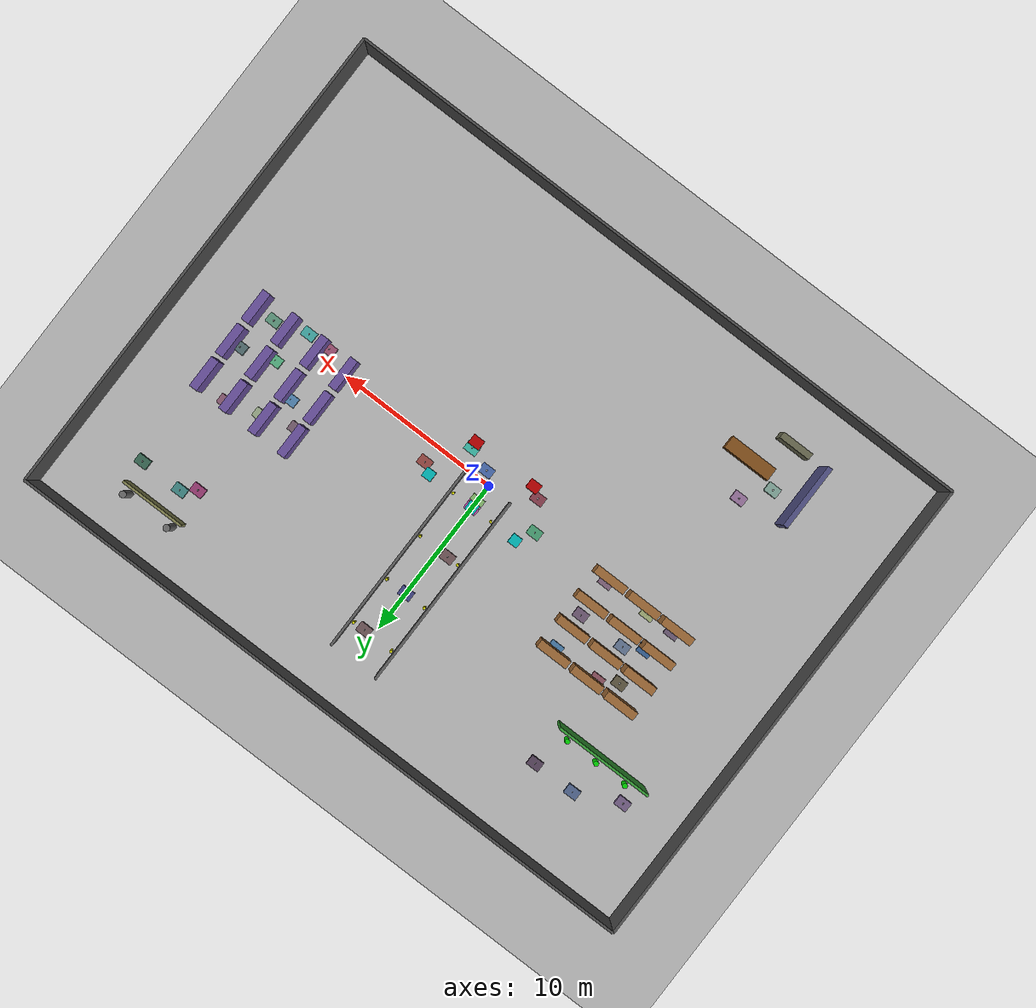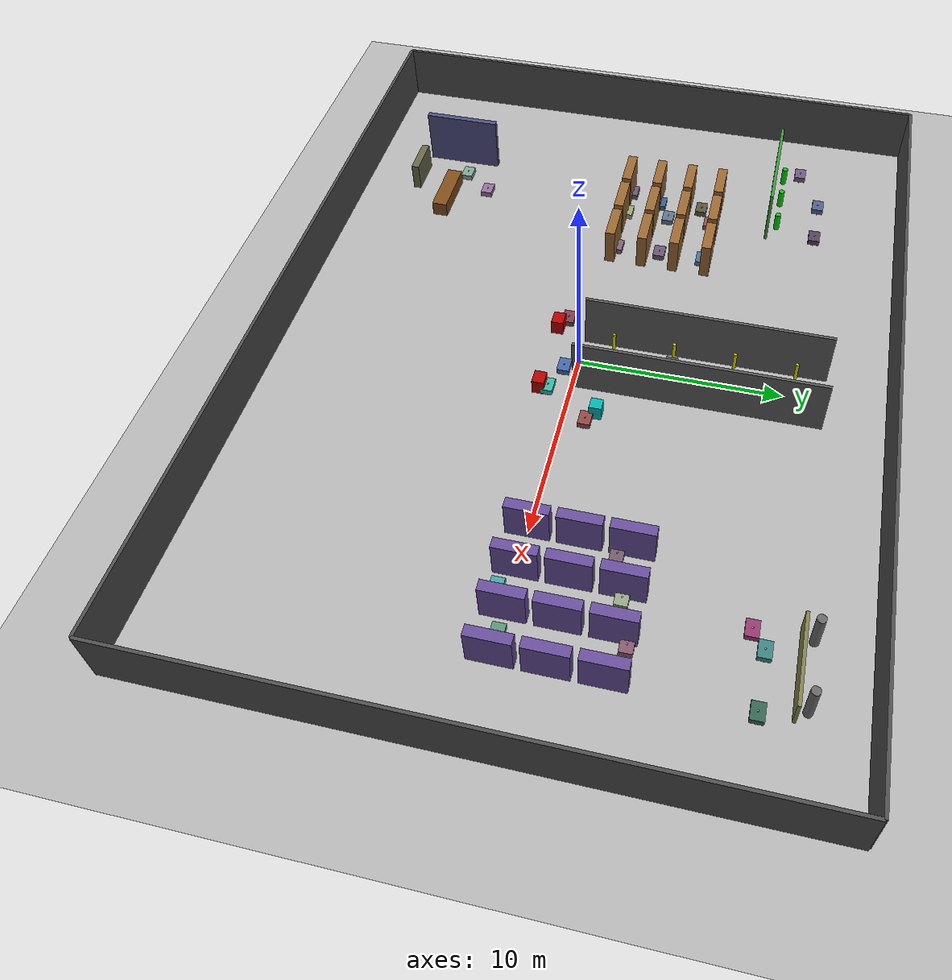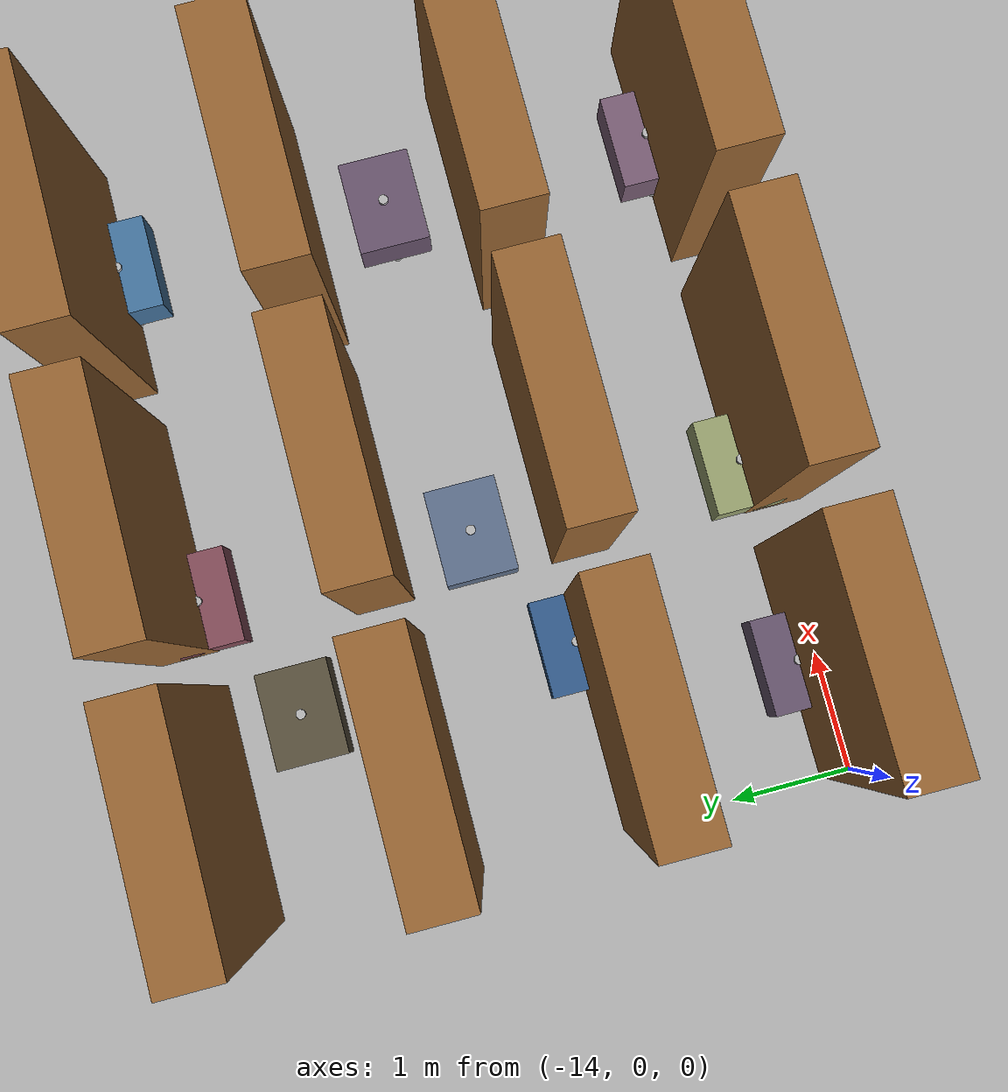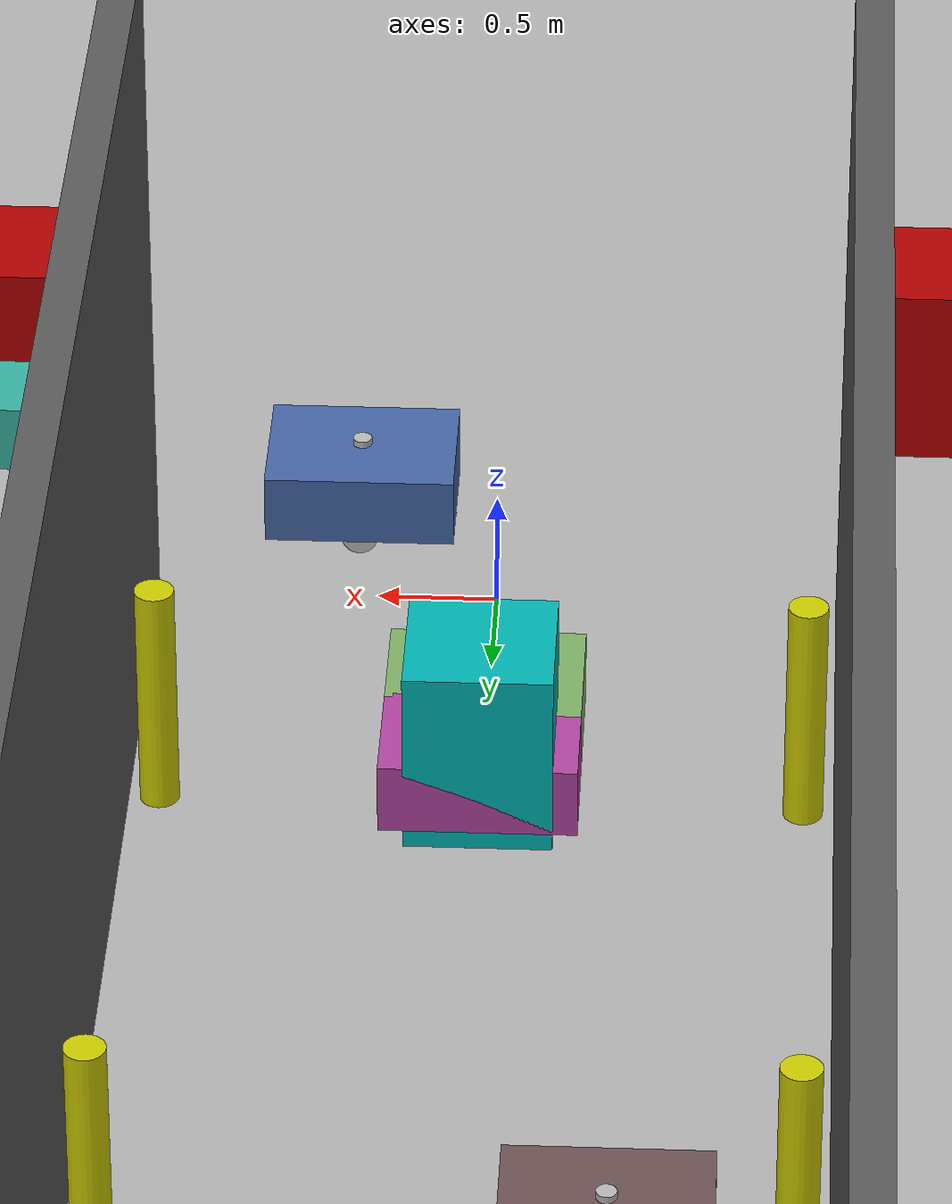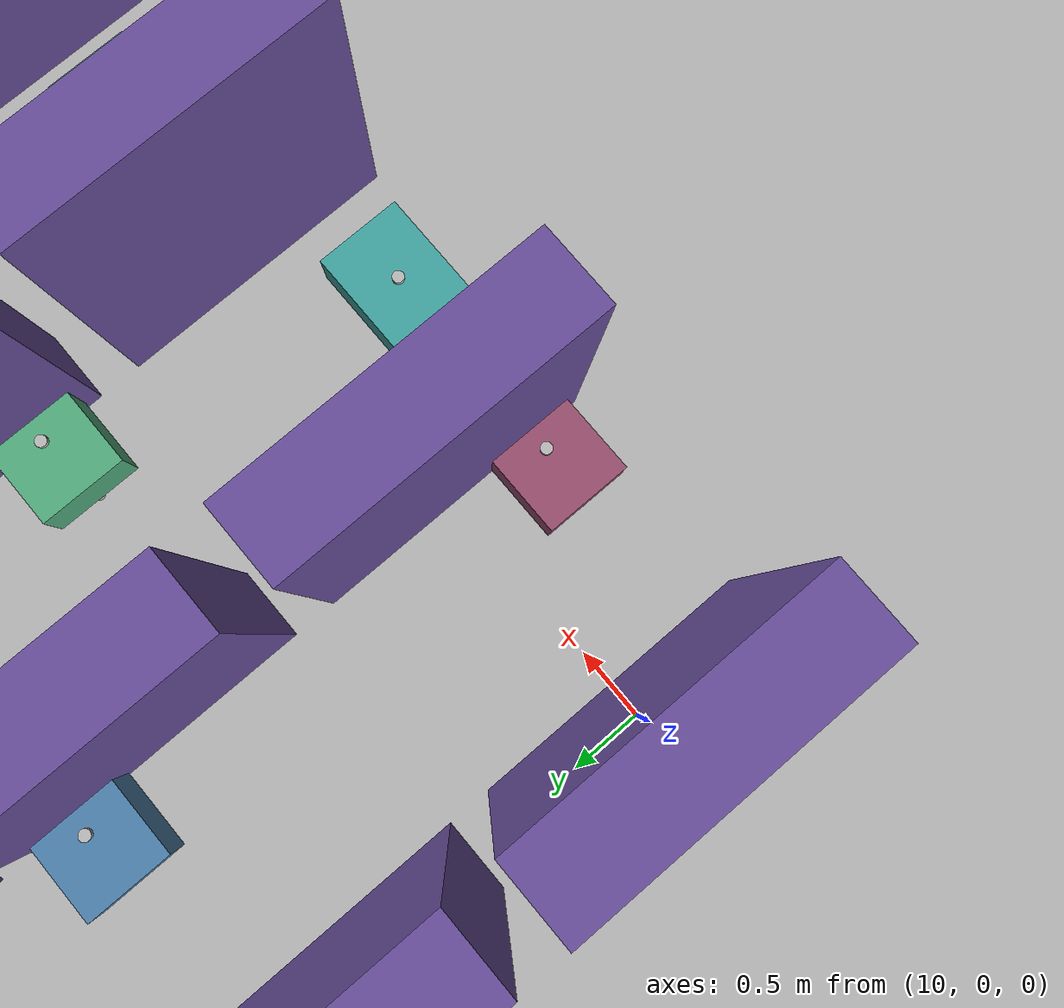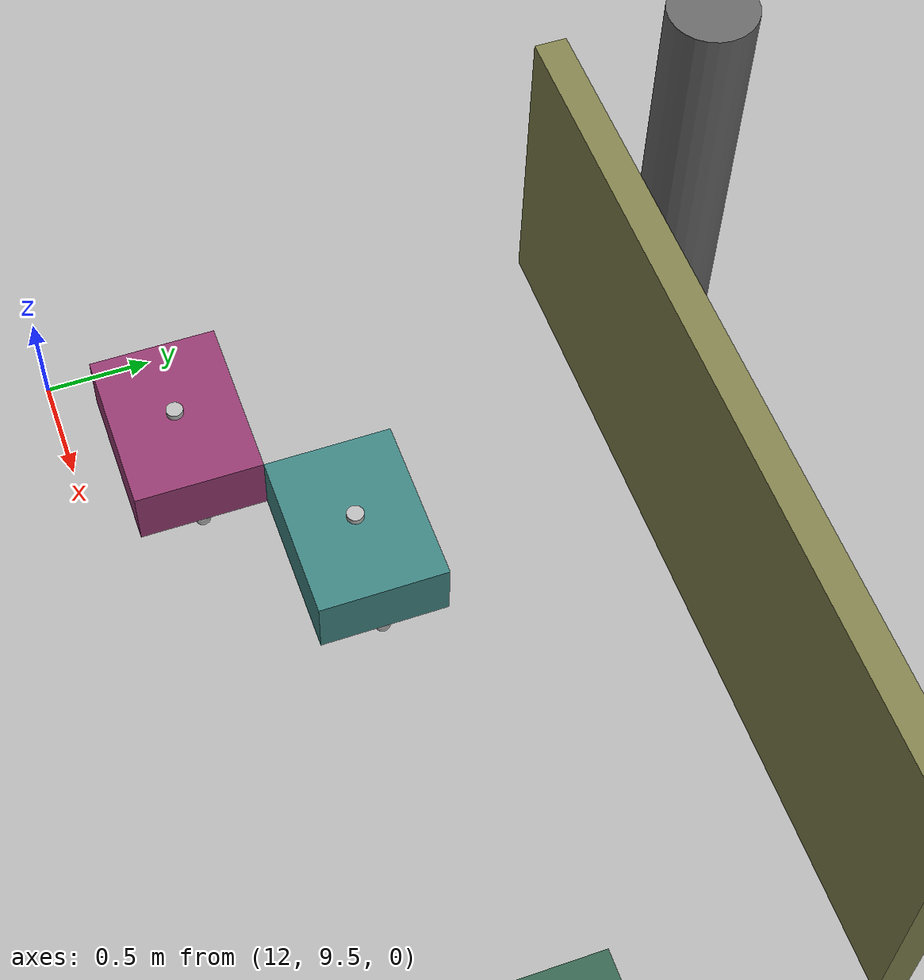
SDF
<?xml version="1.0" ?>
<sdf version="1.8">
  <world name="warehouse_distinct">
    <physics name="1ms" type="ode">
      <max_step_size>0.001</max_step_size>
      <real_time_factor>1.0</real_time_factor>
    </physics>

    <plugin filename="libignition-gazebo-physics-system.so" name="ignition::gazebo::systems::Physics"/>
    <plugin filename="libignition-gazebo-scene-broadcaster-system.so" name="ignition::gazebo::systems::SceneBroadcaster"/>
    <plugin filename="libignition-gazebo-sensors-system.so" name="ignition::gazebo::systems::Sensors"/>

    <light type="directional" name="sun">
      <cast_shadows>true</cast_shadows>
      <pose>0 0 10 0 0 0</pose>
      <diffuse>0.8 0.8 0.8 1</diffuse>
      <specular>0.2 0.2 0.2 1</specular>
      <direction>-0.5 0.1 -0.9</direction>
    </light>

    <!-- Ground plane -->
    <model name="ground_plane">
      <static>true</static>
      <link name="link">
        <collision name="collision">
          <geometry>
            <plane><normal>0 0 1</normal><size>40.0 30.0</size></plane>
          </geometry>
          <surface>
            <friction><ode><mu>0.8</mu><mu2>0.8</mu2></ode></friction>
          </surface>
        </collision>
        <visual name="visual">
          <geometry>
            <plane><normal>0 0 1</normal><size>40.0 30.0</size></plane>
          </geometry>
          <material>
            <ambient>0.7 0.7 0.7 1</ambient>
            <diffuse>0.7 0.7 0.7 1</diffuse>
          </material>
        </visual>
      </link>
    </model>

    <!-- Perimeter walls -->

    <model name="wall_north">
      <static>true</static>
      <pose>0 15.0 1.5 0 0 0</pose>
      <link name="link">
        <collision name="collision">
          <geometry><box><size>40.0 0.15 3.0</size></box></geometry>
        </collision>
        <visual name="visual">
          <geometry><box><size>40.0 0.15 3.0</size></box></geometry>
          <material>
            <ambient>0.3 0.3 0.3 1</ambient>
            <diffuse>0.3 0.3 0.3 1</diffuse>
          </material>
        </visual>
      </link>
    </model>

    <model name="wall_south">
      <static>true</static>
      <pose>0 -15.0 1.5 0 0 0</pose>
      <link name="link">
        <collision name="collision">
          <geometry><box><size>40.0 0.15 3.0</size></box></geometry>
        </collision>
        <visual name="visual">
          <geometry><box><size>40.0 0.15 3.0</size></box></geometry>
          <material>
            <ambient>0.3 0.3 0.3 1</ambient>
            <diffuse>0.3 0.3 0.3 1</diffuse>
          </material>
        </visual>
      </link>
    </model>

    <model name="wall_east">
      <static>true</static>
      <pose>20.0 0 1.5 0 0 0</pose>
      <link name="link">
        <collision name="collision">
          <geometry><box><size>0.15 30.0 3.0</size></box></geometry>
        </collision>
        <visual name="visual">
          <geometry><box><size>0.15 30.0 3.0</size></box></geometry>
          <material>
            <ambient>0.3 0.3 0.3 1</ambient>
            <diffuse>0.3 0.3 0.3 1</diffuse>
          </material>
        </visual>
      </link>
    </model>

    <model name="wall_west">
      <static>true</static>
      <pose>-20.0 0 1.5 0 0 0</pose>
      <link name="link">
        <collision name="collision">
          <geometry><box><size>0.15 30.0 3.0</size></box></geometry>
        </collision>
        <visual name="visual">
          <geometry><box><size>0.15 30.0 3.0</size></box></geometry>
          <material>
            <ambient>0.3 0.3 0.3 1</ambient>
            <diffuse>0.3 0.3 0.3 1</diffuse>
          </material>
        </visual>
      </link>
    </model>

    <!-- Zone geometry -->

    <model name="charge_back_wall">
      <static>true</static>
      <pose>-14.0 8.0 1.5 0 0 0</pose>
      <link name="link">
        <collision name="collision">
          <geometry><box><size>6.0 0.15 3.0</size></box></geometry>
        </collision>
        <visual name="visual">
          <geometry><box><size>6.0 0.15 3.0</size></box></geometry>
          <material>
            <ambient>0.2 0.6 0.2 1</ambient>
            <diffuse>0.2 0.6 0.2 1</diffuse>
          </material>
        </visual>
      </link>
    </model>

    <model name="charger_pillar_0">
      <static>true</static>
      <pose>-16.0 8.5 0.5 0 0 0</pose>
      <link name="link">
        <collision name="collision">
          <geometry><cylinder><radius>0.15</radius><length>1.0</length></cylinder></geometry>
        </collision>
        <visual name="visual">
          <geometry><cylinder><radius>0.15</radius><length>1.0</length></cylinder></geometry>
          <material>
            <ambient>0.0 0.8 0.0 1</ambient>
            <diffuse>0.0 0.8 0.0 1</diffuse>
          </material>
        </visual>
      </link>
    </model>

    <model name="charger_pillar_1">
      <static>true</static>
      <pose>-14.0 8.5 0.5 0 0 0</pose>
      <link name="link">
        <collision name="collision">
          <geometry><cylinder><radius>0.15</radius><length>1.0</length></cylinder></geometry>
        </collision>
        <visual name="visual">
          <geometry><cylinder><radius>0.15</radius><length>1.0</length></cylinder></geometry>
          <material>
            <ambient>0.0 0.8 0.0 1</ambient>
            <diffuse>0.0 0.8 0.0 1</diffuse>
          </material>
        </visual>
      </link>
    </model>

    <model name="charger_pillar_2">
      <static>true</static>
      <pose>-12.0 8.5 0.5 0 0 0</pose>
      <link name="link">
        <collision name="collision">
          <geometry><cylinder><radius>0.15</radius><length>1.0</length></cylinder></geometry>
        </collision>
        <visual name="visual">
          <geometry><cylinder><radius>0.15</radius><length>1.0</length></cylinder></geometry>
          <material>
            <ambient>0.0 0.8 0.0 1</ambient>
            <diffuse>0.0 0.8 0.0 1</diffuse>
          </material>
        </visual>
      </link>
    </model>

    <model name="shelf_a_0_0">
      <static>true</static>
      <pose>-13.0 0.0 1.0 0 0 0</pose>
      <link name="link">
        <collision name="collision">
          <geometry><box><size>2.0 0.5 2.0</size></box></geometry>
        </collision>
        <visual name="visual">
          <geometry><box><size>2.0 0.5 2.0</size></box></geometry>
          <material>
            <ambient>0.6 0.4 0.2 1</ambient>
            <diffuse>0.6 0.4 0.2 1</diffuse>
          </material>
        </visual>
      </link>
    </model>

    <model name="shelf_a_0_1">
      <static>true</static>
      <pose>-10.7 0.0 1.0 0 0 0</pose>
      <link name="link">
        <collision name="collision">
          <geometry><box><size>2.0 0.5 2.0</size></box></geometry>
        </collision>
        <visual name="visual">
          <geometry><box><size>2.0 0.5 2.0</size></box></geometry>
          <material>
            <ambient>0.6 0.4 0.2 1</ambient>
            <diffuse>0.6 0.4 0.2 1</diffuse>
          </material>
        </visual>
      </link>
    </model>

    <model name="shelf_a_0_2">
      <static>true</static>
      <pose>-8.4 0.0 1.0 0 0 0</pose>
      <link name="link">
        <collision name="collision">
          <geometry><box><size>2.0 0.5 2.0</size></box></geometry>
        </collision>
        <visual name="visual">
          <geometry><box><size>2.0 0.5 2.0</size></box></geometry>
          <material>
            <ambient>0.6 0.4 0.2 1</ambient>
            <diffuse>0.6 0.4 0.2 1</diffuse>
          </material>
        </visual>
      </link>
    </model>

    <model name="shelf_a_1_0">
      <static>true</static>
      <pose>-13.0 1.7 1.0 0 0 0</pose>
      <link name="link">
        <collision name="collision">
          <geometry><box><size>2.0 0.5 2.0</size></box></geometry>
        </collision>
        <visual name="visual">
          <geometry><box><size>2.0 0.5 2.0</size></box></geometry>
          <material>
            <ambient>0.6 0.4 0.2 1</ambient>
            <diffuse>0.6 0.4 0.2 1</diffuse>
          </material>
        </visual>
      </link>
    </model>

    <model name="shelf_a_1_1">
      <static>true</static>
      <pose>-10.7 1.7 1.0 0 0 0</pose>
      <link name="link">
        <collision name="collision">
          <geometry><box><size>2.0 0.5 2.0</size></box></geometry>
        </collision>
        <visual name="visual">
          <geometry><box><size>2.0 0.5 2.0</size></box></geometry>
          <material>
            <ambient>0.6 0.4 0.2 1</ambient>
            <diffuse>0.6 0.4 0.2 1</diffuse>
          </material>
        </visual>
      </link>
    </model>

    <model name="shelf_a_1_2">
      <static>true</static>
      <pose>-8.4 1.7 1.0 0 0 0</pose>
      <link name="link">
        <collision name="collision">
          <geometry><box><size>2.0 0.5 2.0</size></box></geometry>
        </collision>
        <visual name="visual">
          <geometry><box><size>2.0 0.5 2.0</size></box></geometry>
          <material>
            <ambient>0.6 0.4 0.2 1</ambient>
            <diffuse>0.6 0.4 0.2 1</diffuse>
          </material>
        </visual>
      </link>
    </model>

    <model name="shelf_a_2_0">
      <static>true</static>
      <pose>-13.0 3.4 1.0 0 0 0</pose>
      <link name="link">
        <collision name="collision">
          <geometry><box><size>2.0 0.5 2.0</size></box></geometry>
        </collision>
        <visual name="visual">
          <geometry><box><size>2.0 0.5 2.0</size></box></geometry>
          <material>
            <ambient>0.6 0.4 0.2 1</ambient>
            <diffuse>0.6 0.4 0.2 1</diffuse>
          </material>
        </visual>
      </link>
    </model>

    <model name="shelf_a_2_1">
      <static>true</static>
      <pose>-10.7 3.4 1.0 0 0 0</pose>
      <link name="link">
        <collision name="collision">
          <geometry><box><size>2.0 0.5 2.0</size></box></geometry>
        </collision>
        <visual name="visual">
          <geometry><box><size>2.0 0.5 2.0</size></box></geometry>
          <material>
            <ambient>0.6 0.4 0.2 1</ambient>
            <diffuse>0.6 0.4 0.2 1</diffuse>
          </material>
        </visual>
      </link>
    </model>

    <model name="shelf_a_2_2">
      <static>true</static>
      <pose>-8.4 3.4 1.0 0 0 0</pose>
      <link name="link">
        <collision name="collision">
          <geometry><box><size>2.0 0.5 2.0</size></box></geometry>
        </collision>
        <visual name="visual">
          <geometry><box><size>2.0 0.5 2.0</size></box></geometry>
          <material>
            <ambient>0.6 0.4 0.2 1</ambient>
            <diffuse>0.6 0.4 0.2 1</diffuse>
          </material>
        </visual>
      </link>
    </model>

    <model name="shelf_a_3_0">
      <static>true</static>
      <pose>-13.0 5.1 1.0 0 0 0</pose>
      <link name="link">
        <collision name="collision">
          <geometry><box><size>2.0 0.5 2.0</size></box></geometry>
        </collision>
        <visual name="visual">
          <geometry><box><size>2.0 0.5 2.0</size></box></geometry>
          <material>
            <ambient>0.6 0.4 0.2 1</ambient>
            <diffuse>0.6 0.4 0.2 1</diffuse>
          </material>
        </visual>
      </link>
    </model>

    <model name="shelf_a_3_1">
      <static>true</static>
      <pose>-10.7 5.1 1.0 0 0 0</pose>
      <link name="link">
        <collision name="collision">
          <geometry><box><size>2.0 0.5 2.0</size></box></geometry>
        </collision>
        <visual name="visual">
          <geometry><box><size>2.0 0.5 2.0</size></box></geometry>
          <material>
            <ambient>0.6 0.4 0.2 1</ambient>
            <diffuse>0.6 0.4 0.2 1</diffuse>
          </material>
        </visual>
      </link>
    </model>

    <model name="shelf_a_3_2">
      <static>true</static>
      <pose>-8.4 5.1 1.0 0 0 0</pose>
      <link name="link">
        <collision name="collision">
          <geometry><box><size>2.0 0.5 2.0</size></box></geometry>
        </collision>
        <visual name="visual">
          <geometry><box><size>2.0 0.5 2.0</size></box></geometry>
          <material>
            <ambient>0.6 0.4 0.2 1</ambient>
            <diffuse>0.6 0.4 0.2 1</diffuse>
          </material>
        </visual>
      </link>
    </model>

    <model name="shelf_b_0_0">
      <static>true</static>
      <pose>10.0 0.0 1.0 0 0 0</pose>
      <link name="link">
        <collision name="collision">
          <geometry><box><size>0.5 2.0 2.0</size></box></geometry>
        </collision>
        <visual name="visual">
          <geometry><box><size>0.5 2.0 2.0</size></box></geometry>
          <material>
            <ambient>0.4 0.3 0.6 1</ambient>
            <diffuse>0.4 0.3 0.6 1</diffuse>
          </material>
        </visual>
      </link>
    </model>

    <model name="shelf_b_0_1">
      <static>true</static>
      <pose>10.0 2.3 1.0 0 0 0</pose>
      <link name="link">
        <collision name="collision">
          <geometry><box><size>0.5 2.0 2.0</size></box></geometry>
        </collision>
        <visual name="visual">
          <geometry><box><size>0.5 2.0 2.0</size></box></geometry>
          <material>
            <ambient>0.4 0.3 0.6 1</ambient>
            <diffuse>0.4 0.3 0.6 1</diffuse>
          </material>
        </visual>
      </link>
    </model>

    <model name="shelf_b_0_2">
      <static>true</static>
      <pose>10.0 4.6 1.0 0 0 0</pose>
      <link name="link">
        <collision name="collision">
          <geometry><box><size>0.5 2.0 2.0</size></box></geometry>
        </collision>
        <visual name="visual">
          <geometry><box><size>0.5 2.0 2.0</size></box></geometry>
          <material>
            <ambient>0.4 0.3 0.6 1</ambient>
            <diffuse>0.4 0.3 0.6 1</diffuse>
          </material>
        </visual>
      </link>
    </model>

    <model name="shelf_b_1_0">
      <static>true</static>
      <pose>12.0 0.0 1.0 0 0 0</pose>
      <link name="link">
        <collision name="collision">
          <geometry><box><size>0.5 2.0 2.0</size></box></geometry>
        </collision>
        <visual name="visual">
          <geometry><box><size>0.5 2.0 2.0</size></box></geometry>
          <material>
            <ambient>0.4 0.3 0.6 1</ambient>
            <diffuse>0.4 0.3 0.6 1</diffuse>
          </material>
        </visual>
      </link>
    </model>

    <model name="shelf_b_1_1">
      <static>true</static>
      <pose>12.0 2.3 1.0 0 0 0</pose>
      <link name="link">
        <collision name="collision">
          <geometry><box><size>0.5 2.0 2.0</size></box></geometry>
        </collision>
        <visual name="visual">
          <geometry><box><size>0.5 2.0 2.0</size></box></geometry>
          <material>
            <ambient>0.4 0.3 0.6 1</ambient>
            <diffuse>0.4 0.3 0.6 1</diffuse>
          </material>
        </visual>
      </link>
    </model>

    <model name="shelf_b_1_2">
      <static>true</static>
      <pose>12.0 4.6 1.0 0 0 0</pose>
      <link name="link">
        <collision name="collision">
          <geometry><box><size>0.5 2.0 2.0</size></box></geometry>
        </collision>
        <visual name="visual">
          <geometry><box><size>0.5 2.0 2.0</size></box></geometry>
          <material>
            <ambient>0.4 0.3 0.6 1</ambient>
            <diffuse>0.4 0.3 0.6 1</diffuse>
          </material>
        </visual>
      </link>
    </model>

    <model name="shelf_b_2_0">
      <static>true</static>
      <pose>14.0 0.0 1.0 0 0 0</pose>
      <link name="link">
        <collision name="collision">
          <geometry><box><size>0.5 2.0 2.0</size></box></geometry>
        </collision>
        <visual name="visual">
          <geometry><box><size>0.5 2.0 2.0</size></box></geometry>
          <material>
            <ambient>0.4 0.3 0.6 1</ambient>
            <diffuse>0.4 0.3 0.6 1</diffuse>
          </material>
        </visual>
      </link>
    </model>

    <model name="shelf_b_2_1">
      <static>true</static>
      <pose>14.0 2.3 1.0 0 0 0</pose>
      <link name="link">
        <collision name="collision">
          <geometry><box><size>0.5 2.0 2.0</size></box></geometry>
        </collision>
        <visual name="visual">
          <geometry><box><size>0.5 2.0 2.0</size></box></geometry>
          <material>
            <ambient>0.4 0.3 0.6 1</ambient>
            <diffuse>0.4 0.3 0.6 1</diffuse>
          </material>
        </visual>
      </link>
    </model>

    <model name="shelf_b_2_2">
      <static>true</static>
      <pose>14.0 4.6 1.0 0 0 0</pose>
      <link name="link">
        <collision name="collision">
          <geometry><box><size>0.5 2.0 2.0</size></box></geometry>
        </collision>
        <visual name="visual">
          <geometry><box><size>0.5 2.0 2.0</size></box></geometry>
          <material>
            <ambient>0.4 0.3 0.6 1</ambient>
            <diffuse>0.4 0.3 0.6 1</diffuse>
          </material>
        </visual>
      </link>
    </model>

    <model name="shelf_b_3_0">
      <static>true</static>
      <pose>16.0 0.0 1.0 0 0 0</pose>
      <link name="link">
        <collision name="collision">
          <geometry><box><size>0.5 2.0 2.0</size></box></geometry>
        </collision>
        <visual name="visual">
          <geometry><box><size>0.5 2.0 2.0</size></box></geometry>
          <material>
            <ambient>0.4 0.3 0.6 1</ambient>
            <diffuse>0.4 0.3 0.6 1</diffuse>
          </material>
        </visual>
      </link>
    </model>

    <model name="shelf_b_3_1">
      <static>true</static>
      <pose>16.0 2.3 1.0 0 0 0</pose>
      <link name="link">
        <collision name="collision">
          <geometry><box><size>0.5 2.0 2.0</size></box></geometry>
        </collision>
        <visual name="visual">
          <geometry><box><size>0.5 2.0 2.0</size></box></geometry>
          <material>
            <ambient>0.4 0.3 0.6 1</ambient>
            <diffuse>0.4 0.3 0.6 1</diffuse>
          </material>
        </visual>
      </link>
    </model>

    <model name="shelf_b_3_2">
      <static>true</static>
      <pose>16.0 4.6 1.0 0 0 0</pose>
      <link name="link">
        <collision name="collision">
          <geometry><box><size>0.5 2.0 2.0</size></box></geometry>
        </collision>
        <visual name="visual">
          <geometry><box><size>0.5 2.0 2.0</size></box></geometry>
          <material>
            <ambient>0.4 0.3 0.6 1</ambient>
            <diffuse>0.4 0.3 0.6 1</diffuse>
          </material>
        </visual>
      </link>
    </model>

    <model name="pick_table_0">
      <static>true</static>
      <pose>-3.0 1.5 0.4 0 0 0</pose>
      <link name="link">
        <collision name="collision">
          <geometry><box><size>0.6 0.6 0.8</size></box></geometry>
        </collision>
        <visual name="visual">
          <geometry><box><size>0.6 0.6 0.8</size></box></geometry>
          <material>
            <ambient>0.0 0.7 0.7 1</ambient>
            <diffuse>0.0 0.7 0.7 1</diffuse>
          </material>
        </visual>
      </link>
    </model>

    <model name="pick_table_1">
      <static>true</static>
      <pose>0.0 1.5 0.4 0 0 0</pose>
      <link name="link">
        <collision name="collision">
          <geometry><box><size>0.6 0.6 0.8</size></box></geometry>
        </collision>
        <visual name="visual">
          <geometry><box><size>0.6 0.6 0.8</size></box></geometry>
          <material>
            <ambient>0.0 0.7 0.7 1</ambient>
            <diffuse>0.0 0.7 0.7 1</diffuse>
          </material>
        </visual>
      </link>
    </model>

    <model name="pick_table_2">
      <static>true</static>
      <pose>3.0 1.5 0.4 0 0 0</pose>
      <link name="link">
        <collision name="collision">
          <geometry><box><size>0.6 0.6 0.8</size></box></geometry>
        </collision>
        <visual name="visual">
          <geometry><box><size>0.6 0.6 0.8</size></box></geometry>
          <material>
            <ambient>0.0 0.7 0.7 1</ambient>
            <diffuse>0.0 0.7 0.7 1</diffuse>
          </material>
        </visual>
      </link>
    </model>

    <model name="drop_table_0">
      <static>true</static>
      <pose>-2.0 -1.5 0.4 0 0 0</pose>
      <link name="link">
        <collision name="collision">
          <geometry><box><size>0.72 0.6 0.8</size></box></geometry>
        </collision>
        <visual name="visual">
          <geometry><box><size>0.72 0.6 0.8</size></box></geometry>
          <material>
            <ambient>0.7 0.0 0.0 1</ambient>
            <diffuse>0.7 0.0 0.0 1</diffuse>
          </material>
        </visual>
      </link>
    </model>

    <model name="drop_table_1">
      <static>true</static>
      <pose>2.0 -1.5 0.4 0 0 0</pose>
      <link name="link">
        <collision name="collision">
          <geometry><box><size>0.72 0.6 0.8</size></box></geometry>
        </collision>
        <visual name="visual">
          <geometry><box><size>0.72 0.6 0.8</size></box></geometry>
          <material>
            <ambient>0.7 0.0 0.0 1</ambient>
            <diffuse>0.7 0.0 0.0 1</diffuse>
          </material>
        </visual>
      </link>
    </model>

    <model name="corridor_wall_left">
      <static>true</static>
      <pose>-1.5 6.0 1.5 0 0 0</pose>
      <link name="link">
        <collision name="collision">
          <geometry><box><size>0.15 12.0 3.0</size></box></geometry>
        </collision>
        <visual name="visual">
          <geometry><box><size>0.15 12.0 3.0</size></box></geometry>
          <material>
            <ambient>0.35 0.35 0.35 1</ambient>
            <diffuse>0.35 0.35 0.35 1</diffuse>
          </material>
        </visual>
      </link>
    </model>

    <model name="corridor_wall_right">
      <static>true</static>
      <pose>1.5 6.0 1.5 0 0 0</pose>
      <link name="link">
        <collision name="collision">
          <geometry><box><size>0.15 12.0 3.0</size></box></geometry>
        </collision>
        <visual name="visual">
          <geometry><box><size>0.15 12.0 3.0</size></box></geometry>
          <material>
            <ambient>0.35 0.35 0.35 1</ambient>
            <diffuse>0.35 0.35 0.35 1</diffuse>
          </material>
        </visual>
      </link>
    </model>

    <model name="marker_left_0">
      <static>true</static>
      <pose>-1.3 1.5 0.5 0 0 0</pose>
      <link name="link">
        <collision name="collision">
          <geometry><cylinder><radius>0.08</radius><length>1.0</length></cylinder></geometry>
        </collision>
        <visual name="visual">
          <geometry><cylinder><radius>0.08</radius><length>1.0</length></cylinder></geometry>
          <material>
            <ambient>0.8 0.8 0.0 1</ambient>
            <diffuse>0.8 0.8 0.0 1</diffuse>
          </material>
        </visual>
      </link>
    </model>

    <model name="marker_right_0">
      <static>true</static>
      <pose>1.3 1.5 0.5 0 0 0</pose>
      <link name="link">
        <collision name="collision">
          <geometry><cylinder><radius>0.08</radius><length>1.0</length></cylinder></geometry>
        </collision>
        <visual name="visual">
          <geometry><cylinder><radius>0.08</radius><length>1.0</length></cylinder></geometry>
          <material>
            <ambient>0.8 0.8 0.0 1</ambient>
            <diffuse>0.8 0.8 0.0 1</diffuse>
          </material>
        </visual>
      </link>
    </model>

    <model name="marker_left_1">
      <static>true</static>
      <pose>-1.3 4.5 0.5 0 0 0</pose>
      <link name="link">
        <collision name="collision">
          <geometry><cylinder><radius>0.08</radius><length>1.0</length></cylinder></geometry>
        </collision>
        <visual name="visual">
          <geometry><cylinder><radius>0.08</radius><length>1.0</length></cylinder></geometry>
          <material>
            <ambient>0.8 0.8 0.0 1</ambient>
            <diffuse>0.8 0.8 0.0 1</diffuse>
          </material>
        </visual>
      </link>
    </model>

    <model name="marker_right_1">
      <static>true</static>
      <pose>1.3 4.5 0.5 0 0 0</pose>
      <link name="link">
        <collision name="collision">
          <geometry><cylinder><radius>0.08</radius><length>1.0</length></cylinder></geometry>
        </collision>
        <visual name="visual">
          <geometry><cylinder><radius>0.08</radius><length>1.0</length></cylinder></geometry>
          <material>
            <ambient>0.8 0.8 0.0 1</ambient>
            <diffuse>0.8 0.8 0.0 1</diffuse>
          </material>
        </visual>
      </link>
    </model>

    <model name="marker_left_2">
      <static>true</static>
      <pose>-1.3 7.5 0.5 0 0 0</pose>
      <link name="link">
        <collision name="collision">
          <geometry><cylinder><radius>0.08</radius><length>1.0</length></cylinder></geometry>
        </collision>
        <visual name="visual">
          <geometry><cylinder><radius>0.08</radius><length>1.0</length></cylinder></geometry>
          <material>
            <ambient>0.8 0.8 0.0 1</ambient>
            <diffuse>0.8 0.8 0.0 1</diffuse>
          </material>
        </visual>
      </link>
    </model>

    <model name="marker_right_2">
      <static>true</static>
      <pose>1.3 7.5 0.5 0 0 0</pose>
      <link name="link">
        <collision name="collision">
          <geometry><cylinder><radius>0.08</radius><length>1.0</length></cylinder></geometry>
        </collision>
        <visual name="visual">
          <geometry><cylinder><radius>0.08</radius><length>1.0</length></cylinder></geometry>
          <material>
            <ambient>0.8 0.8 0.0 1</ambient>
            <diffuse>0.8 0.8 0.0 1</diffuse>
          </material>
        </visual>
      </link>
    </model>

    <model name="marker_left_3">
      <static>true</static>
      <pose>-1.3 10.5 0.5 0 0 0</pose>
      <link name="link">
        <collision name="collision">
          <geometry><cylinder><radius>0.08</radius><length>1.0</length></cylinder></geometry>
        </collision>
        <visual name="visual">
          <geometry><cylinder><radius>0.08</radius><length>1.0</length></cylinder></geometry>
          <material>
            <ambient>0.8 0.8 0.0 1</ambient>
            <diffuse>0.8 0.8 0.0 1</diffuse>
          </material>
        </visual>
      </link>
    </model>

    <model name="marker_right_3">
      <static>true</static>
      <pose>1.3 10.5 0.5 0 0 0</pose>
      <link name="link">
        <collision name="collision">
          <geometry><cylinder><radius>0.08</radius><length>1.0</length></cylinder></geometry>
        </collision>
        <visual name="visual">
          <geometry><cylinder><radius>0.08</radius><length>1.0</length></cylinder></geometry>
          <material>
            <ambient>0.8 0.8 0.0 1</ambient>
            <diffuse>0.8 0.8 0.0 1</diffuse>
          </material>
        </visual>
      </link>
    </model>

    <model name="staging_halfwall">
      <static>true</static>
      <pose>14.0 12.0 0.75 0 0 0</pose>
      <link name="link">
        <collision name="collision">
          <geometry><box><size>4.0 0.15 1.5</size></box></geometry>
        </collision>
        <visual name="visual">
          <geometry><box><size>4.0 0.15 1.5</size></box></geometry>
          <material>
            <ambient>0.5 0.5 0.3 1</ambient>
            <diffuse>0.5 0.5 0.3 1</diffuse>
          </material>
        </visual>
      </link>
    </model>

    <model name="dock_pillar_left">
      <static>true</static>
      <pose>12.5 12.5 1.0 0 0 0</pose>
      <link name="link">
        <collision name="collision">
          <geometry><cylinder><radius>0.2</radius><length>2.0</length></cylinder></geometry>
        </collision>
        <visual name="visual">
          <geometry><cylinder><radius>0.2</radius><length>2.0</length></cylinder></geometry>
          <material>
            <ambient>0.4 0.4 0.4 1</ambient>
            <diffuse>0.4 0.4 0.4 1</diffuse>
          </material>
        </visual>
      </link>
    </model>

    <model name="dock_pillar_right">
      <static>true</static>
      <pose>15.5 12.5 1.0 0 0 0</pose>
      <link name="link">
        <collision name="collision">
          <geometry><cylinder><radius>0.2</radius><length>2.0</length></cylinder></geometry>
        </collision>
        <visual name="visual">
          <geometry><cylinder><radius>0.2</radius><length>2.0</length></cylinder></geometry>
          <material>
            <ambient>0.4 0.4 0.4 1</ambient>
            <diffuse>0.4 0.4 0.4 1</diffuse>
          </material>
        </visual>
      </link>
    </model>

    <model name="workbench">
      <static>true</static>
      <pose>-10.5 -10.0 0.4 0 0 0</pose>
      <link name="link">
        <collision name="collision">
          <geometry><box><size>3.0 0.8 0.8</size></box></geometry>
        </collision>
        <visual name="visual">
          <geometry><box><size>3.0 0.8 0.8</size></box></geometry>
          <material>
            <ambient>0.5 0.3 0.1 1</ambient>
            <diffuse>0.5 0.3 0.1 1</diffuse>
          </material>
        </visual>
      </link>
    </model>

    <model name="tool_rack">
      <static>true</static>
      <pose>-14.0 -10.0 1.5 0 0 0</pose>
      <link name="link">
        <collision name="collision">
          <geometry><box><size>0.3 4.0 3.0</size></box></geometry>
        </collision>
        <visual name="visual">
          <geometry><box><size>0.3 4.0 3.0</size></box></geometry>
          <material>
            <ambient>0.3 0.3 0.5 1</ambient>
            <diffuse>0.3 0.3 0.5 1</diffuse>
          </material>
        </visual>
      </link>
    </model>

    <model name="equipment">
      <static>true</static>
      <pose>-12.0 -12.0 0.75 0 0 0</pose>
      <link name="link">
        <collision name="collision">
          <geometry><box><size>2.0 0.4 1.5</size></box></geometry>
        </collision>
        <visual name="visual">
          <geometry><box><size>2.0 0.4 1.5</size></box></geometry>
          <material>
            <ambient>0.4 0.4 0.3 1</ambient>
            <diffuse>0.4 0.4 0.3 1</diffuse>
          </material>
        </visual>
      </link>
    </model>

    <!-- ═══ FLEET ROBOTS ═══ -->

    <model name="robot_01">
      <pose>-16.6 9.4 0 0 0 0.0</pose>
      <self_collide>false</self_collide>
      <link name="chassis">
        <pose>0 0 0.225 0 0 0</pose>
        <inertial><mass>50.0</mass>
          <inertia><ixx>1.875</ixx><iyy>3.042</iyy><izz>4.167</izz><ixy>0</ixy><ixz>0</ixz><iyz>0</iyz></inertia>
        </inertial>
        <visual name="v"><geometry><box><size>0.8 0.6 0.3</size></box></geometry>
          <material><ambient>0.43 0.35 0.50 1</ambient><diffuse>0.43 0.35 0.50 1</diffuse></material>
        </visual>
        <collision name="c"><geometry><box><size>0.8 0.6 0.3</size></box></geometry></collision>
      </link>
      <link name="left_wheel">
        <pose>0 0.25 0.075 1.5708 0 0</pose>
        <inertial><mass>1.0</mass><inertia><ixx>0.00154</ixx><iyy>0.00154</iyy><izz>0.00281</izz><ixy>0</ixy><ixz>0</ixz><iyz>0</iyz></inertia></inertial>
        <visual name="v"><geometry><cylinder><radius>0.075</radius><length>0.04</length></cylinder></geometry></visual>
        <collision name="c"><geometry><cylinder><radius>0.075</radius><length>0.04</length></cylinder></geometry>
          <surface><friction><ode><mu>1.0</mu><mu2>1.0</mu2></ode></friction></surface>
        </collision>
      </link>
      <joint name="left_wheel_joint" type="revolute"><parent>chassis</parent><child>left_wheel</child>
        <axis><xyz>0 0 1</xyz><limit><lower>-1e16</lower><upper>1e16</upper></limit></axis>
      </joint>
      <link name="right_wheel">
        <pose>0 -0.25 0.075 1.5708 0 0</pose>
        <inertial><mass>1.0</mass><inertia><ixx>0.00154</ixx><iyy>0.00154</iyy><izz>0.00281</izz><ixy>0</ixy><ixz>0</ixz><iyz>0</iyz></inertia></inertial>
        <visual name="v"><geometry><cylinder><radius>0.075</radius><length>0.04</length></cylinder></geometry></visual>
        <collision name="c"><geometry><cylinder><radius>0.075</radius><length>0.04</length></cylinder></geometry>
          <surface><friction><ode><mu>1.0</mu><mu2>1.0</mu2></ode></friction></surface>
        </collision>
      </link>
      <joint name="right_wheel_joint" type="revolute"><parent>chassis</parent><child>right_wheel</child>
        <axis><xyz>0 0 1</xyz><limit><lower>-1e16</lower><upper>1e16</upper></limit></axis>
      </joint>
      <link name="front_caster">
        <pose>0.3625 0 0.0375 0 0 0</pose>
        <inertial><mass>0.5</mass><inertia><ixx>0.000281</ixx><iyy>0.000281</iyy><izz>0.000281</izz><ixy>0</ixy><ixz>0</ixz><iyz>0</iyz></inertia></inertial>
        <visual name="v"><geometry><sphere><radius>0.0375</radius></sphere></geometry></visual>
        <collision name="c"><geometry><sphere><radius>0.0375</radius></sphere></geometry>
          <surface><friction><ode><mu>0.01</mu><mu2>0.01</mu2></ode></friction></surface>
        </collision>
      </link>
      <joint name="fc_joint" type="ball"><parent>chassis</parent><child>front_caster</child></joint>
      <link name="rear_caster">
        <pose>-0.3625 0 0.0375 0 0 0</pose>
        <inertial><mass>0.5</mass><inertia><ixx>0.000281</ixx><iyy>0.000281</iyy><izz>0.000281</izz><ixy>0</ixy><ixz>0</ixz><iyz>0</iyz></inertia></inertial>
        <visual name="v"><geometry><sphere><radius>0.0375</radius></sphere></geometry></visual>
        <collision name="c"><geometry><sphere><radius>0.0375</radius></sphere></geometry>
          <surface><friction><ode><mu>0.01</mu><mu2>0.01</mu2></ode></friction></surface>
        </collision>
      </link>
      <joint name="rc_joint" type="ball"><parent>chassis</parent><child>rear_caster</child></joint>
      <plugin filename="gz-sim-diff-drive-system" name="gz::sim::systems::DiffDrive">
        <left_joint>left_wheel_joint</left_joint><right_joint>right_wheel_joint</right_joint>
        <wheel_separation>0.5</wheel_separation><wheel_radius>0.075</wheel_radius>
        <max_linear_acceleration>0.8</max_linear_acceleration><max_angular_velocity>2.5</max_angular_velocity>
        <topic>/robot_01/cmd_vel</topic>
        <odom_topic>/robot_01/odom</odom_topic>
        <tf_topic>/robot_01/tf</tf_topic>
        <frame_id>odom</frame_id><child_frame_id>chassis</child_frame_id>
        <odom_publish_frequency>15</odom_publish_frequency>
      </plugin>
      <link name="lidar_link">
        <pose>0 0 0.395 0 0 0</pose>
        <inertial><mass>0.1</mass><inertia><ixx>0.000047</ixx><iyy>0.000047</iyy><izz>0.00008</izz><ixy>0</ixy><ixz>0</ixz><iyz>0</iyz></inertia></inertial>
        <visual name="v"><geometry><cylinder><radius>0.04</radius><length>0.03</length></cylinder></geometry></visual>
        <collision name="c"><geometry><cylinder><radius>0.04</radius><length>0.03</length></cylinder></geometry></collision>
        <sensor name="lidar" type="gpu_lidar">
          <always_on>true</always_on><update_rate>10</update_rate><visualize>false</visualize>
          <topic>/robot_01/lidar</topic>
          <ray><scan><horizontal><samples>360</samples><resolution>1</resolution>
            <min_angle>-3.141593</min_angle><max_angle>3.141593</max_angle></horizontal>
          </scan><range><min>0.08</min><max>12.0</max><resolution>0.01</resolution></range>
          <noise><type>gaussian</type><mean>0.0</mean><stddev>0.03</stddev></noise></ray>
        </sensor>
      </link>
      <joint name="lidar_joint" type="fixed"><parent>chassis</parent><child>lidar_link</child></joint>
      <plugin filename="gz-sim-joint-state-publisher-system" name="gz::sim::systems::JointStatePublisher"/>
    </model>

    <model name="robot_02">
      <pose>-13.0 0.25 0 0 0 0.0</pose>
      <self_collide>false</self_collide>
      <link name="chassis">
        <pose>0 0 0.225 0 0 0</pose>
        <inertial><mass>50.0</mass>
          <inertia><ixx>1.875</ixx><iyy>3.042</iyy><izz>4.167</izz><ixy>0</ixy><ixz>0</ixz><iyz>0</iyz></inertia>
        </inertial>
        <visual name="v"><geometry><box><size>0.8 0.6 0.3</size></box></geometry>
          <material><ambient>0.40 0.33 0.43 1</ambient><diffuse>0.40 0.33 0.43 1</diffuse></material>
        </visual>
        <collision name="c"><geometry><box><size>0.8 0.6 0.3</size></box></geometry></collision>
      </link>
      <link name="left_wheel">
        <pose>0 0.25 0.075 1.5708 0 0</pose>
        <inertial><mass>1.0</mass><inertia><ixx>0.00154</ixx><iyy>0.00154</iyy><izz>0.00281</izz><ixy>0</ixy><ixz>0</ixz><iyz>0</iyz></inertia></inertial>
        <visual name="v"><geometry><cylinder><radius>0.075</radius><length>0.04</length></cylinder></geometry></visual>
        <collision name="c"><geometry><cylinder><radius>0.075</radius><length>0.04</length></cylinder></geometry>
          <surface><friction><ode><mu>1.0</mu><mu2>1.0</mu2></ode></friction></surface>
        </collision>
      </link>
      <joint name="left_wheel_joint" type="revolute"><parent>chassis</parent><child>left_wheel</child>
        <axis><xyz>0 0 1</xyz><limit><lower>-1e16</lower><upper>1e16</upper></limit></axis>
      </joint>
      <link name="right_wheel">
        <pose>0 -0.25 0.075 1.5708 0 0</pose>
        <inertial><mass>1.0</mass><inertia><ixx>0.00154</ixx><iyy>0.00154</iyy><izz>0.00281</izz><ixy>0</ixy><ixz>0</ixz><iyz>0</iyz></inertia></inertial>
        <visual name="v"><geometry><cylinder><radius>0.075</radius><length>0.04</length></cylinder></geometry></visual>
        <collision name="c"><geometry><cylinder><radius>0.075</radius><length>0.04</length></cylinder></geometry>
          <surface><friction><ode><mu>1.0</mu><mu2>1.0</mu2></ode></friction></surface>
        </collision>
      </link>
      <joint name="right_wheel_joint" type="revolute"><parent>chassis</parent><child>right_wheel</child>
        <axis><xyz>0 0 1</xyz><limit><lower>-1e16</lower><upper>1e16</upper></limit></axis>
      </joint>
      <link name="front_caster">
        <pose>0.3625 0 0.0375 0 0 0</pose>
        <inertial><mass>0.5</mass><inertia><ixx>0.000281</ixx><iyy>0.000281</iyy><izz>0.000281</izz><ixy>0</ixy><ixz>0</ixz><iyz>0</iyz></inertia></inertial>
        <visual name="v"><geometry><sphere><radius>0.0375</radius></sphere></geometry></visual>
        <collision name="c"><geometry><sphere><radius>0.0375</radius></sphere></geometry>
          <surface><friction><ode><mu>0.01</mu><mu2>0.01</mu2></ode></friction></surface>
        </collision>
      </link>
      <joint name="fc_joint" type="ball"><parent>chassis</parent><child>front_caster</child></joint>
      <link name="rear_caster">
        <pose>-0.3625 0 0.0375 0 0 0</pose>
        <inertial><mass>0.5</mass><inertia><ixx>0.000281</ixx><iyy>0.000281</iyy><izz>0.000281</izz><ixy>0</ixy><ixz>0</ixz><iyz>0</iyz></inertia></inertial>
        <visual name="v"><geometry><sphere><radius>0.0375</radius></sphere></geometry></visual>
        <collision name="c"><geometry><sphere><radius>0.0375</radius></sphere></geometry>
          <surface><friction><ode><mu>0.01</mu><mu2>0.01</mu2></ode></friction></surface>
        </collision>
      </link>
      <joint name="rc_joint" type="ball"><parent>chassis</parent><child>rear_caster</child></joint>
      <plugin filename="gz-sim-diff-drive-system" name="gz::sim::systems::DiffDrive">
        <left_joint>left_wheel_joint</left_joint><right_joint>right_wheel_joint</right_joint>
        <wheel_separation>0.5</wheel_separation><wheel_radius>0.075</wheel_radius>
        <max_linear_acceleration>0.8</max_linear_acceleration><max_angular_velocity>2.5</max_angular_velocity>
        <topic>/robot_02/cmd_vel</topic>
        <odom_topic>/robot_02/odom</odom_topic>
        <tf_topic>/robot_02/tf</tf_topic>
        <frame_id>odom</frame_id><child_frame_id>chassis</child_frame_id>
        <odom_publish_frequency>15</odom_publish_frequency>
      </plugin>
      <link name="lidar_link">
        <pose>0 0 0.395 0 0 0</pose>
        <inertial><mass>0.1</mass><inertia><ixx>0.000047</ixx><iyy>0.000047</iyy><izz>0.00008</izz><ixy>0</ixy><ixz>0</ixz><iyz>0</iyz></inertia></inertial>
        <visual name="v"><geometry><cylinder><radius>0.04</radius><length>0.03</length></cylinder></geometry></visual>
        <collision name="c"><geometry><cylinder><radius>0.04</radius><length>0.03</length></cylinder></geometry></collision>
        <sensor name="lidar" type="gpu_lidar">
          <always_on>true</always_on><update_rate>10</update_rate><visualize>false</visualize>
          <topic>/robot_02/lidar</topic>
          <ray><scan><horizontal><samples>360</samples><resolution>1</resolution>
            <min_angle>-3.141593</min_angle><max_angle>3.141593</max_angle></horizontal>
          </scan><range><min>0.08</min><max>12.0</max><resolution>0.01</resolution></range>
          <noise><type>gaussian</type><mean>0.0</mean><stddev>0.03</stddev></noise></ray>
        </sensor>
      </link>
      <joint name="lidar_joint" type="fixed"><parent>chassis</parent><child>lidar_link</child></joint>
      <plugin filename="gz-sim-joint-state-publisher-system" name="gz::sim::systems::JointStatePublisher"/>
    </model>

    <model name="robot_03">
      <pose>11.6 -0.6 0 0 0 0.0</pose>
      <self_collide>false</self_collide>
      <link name="chassis">
        <pose>0 0 0.225 0 0 0</pose>
        <inertial><mass>50.0</mass>
          <inertia><ixx>1.875</ixx><iyy>3.042</iyy><izz>4.167</izz><ixy>0</ixy><ixz>0</ixz><iyz>0</iyz></inertia>
        </inertial>
        <visual name="v"><geometry><box><size>0.8 0.6 0.3</size></box></geometry>
          <material><ambient>0.59 0.30 0.43 1</ambient><diffuse>0.59 0.30 0.43 1</diffuse></material>
        </visual>
        <collision name="c"><geometry><box><size>0.8 0.6 0.3</size></box></geometry></collision>
      </link>
      <link name="left_wheel">
        <pose>0 0.25 0.075 1.5708 0 0</pose>
        <inertial><mass>1.0</mass><inertia><ixx>0.00154</ixx><iyy>0.00154</iyy><izz>0.00281</izz><ixy>0</ixy><ixz>0</ixz><iyz>0</iyz></inertia></inertial>
        <visual name="v"><geometry><cylinder><radius>0.075</radius><length>0.04</length></cylinder></geometry></visual>
        <collision name="c"><geometry><cylinder><radius>0.075</radius><length>0.04</length></cylinder></geometry>
          <surface><friction><ode><mu>1.0</mu><mu2>1.0</mu2></ode></friction></surface>
        </collision>
      </link>
      <joint name="left_wheel_joint" type="revolute"><parent>chassis</parent><child>left_wheel</child>
        <axis><xyz>0 0 1</xyz><limit><lower>-1e16</lower><upper>1e16</upper></limit></axis>
      </joint>
      <link name="right_wheel">
        <pose>0 -0.25 0.075 1.5708 0 0</pose>
        <inertial><mass>1.0</mass><inertia><ixx>0.00154</ixx><iyy>0.00154</iyy><izz>0.00281</izz><ixy>0</ixy><ixz>0</ixz><iyz>0</iyz></inertia></inertial>
        <visual name="v"><geometry><cylinder><radius>0.075</radius><length>0.04</length></cylinder></geometry></visual>
        <collision name="c"><geometry><cylinder><radius>0.075</radius><length>0.04</length></cylinder></geometry>
          <surface><friction><ode><mu>1.0</mu><mu2>1.0</mu2></ode></friction></surface>
        </collision>
      </link>
      <joint name="right_wheel_joint" type="revolute"><parent>chassis</parent><child>right_wheel</child>
        <axis><xyz>0 0 1</xyz><limit><lower>-1e16</lower><upper>1e16</upper></limit></axis>
      </joint>
      <link name="front_caster">
        <pose>0.3625 0 0.0375 0 0 0</pose>
        <inertial><mass>0.5</mass><inertia><ixx>0.000281</ixx><iyy>0.000281</iyy><izz>0.000281</izz><ixy>0</ixy><ixz>0</ixz><iyz>0</iyz></inertia></inertial>
        <visual name="v"><geometry><sphere><radius>0.0375</radius></sphere></geometry></visual>
        <collision name="c"><geometry><sphere><radius>0.0375</radius></sphere></geometry>
          <surface><friction><ode><mu>0.01</mu><mu2>0.01</mu2></ode></friction></surface>
        </collision>
      </link>
      <joint name="fc_joint" type="ball"><parent>chassis</parent><child>front_caster</child></joint>
      <link name="rear_caster">
        <pose>-0.3625 0 0.0375 0 0 0</pose>
        <inertial><mass>0.5</mass><inertia><ixx>0.000281</ixx><iyy>0.000281</iyy><izz>0.000281</izz><ixy>0</ixy><ixz>0</ixz><iyz>0</iyz></inertia></inertial>
        <visual name="v"><geometry><sphere><radius>0.0375</radius></sphere></geometry></visual>
        <collision name="c"><geometry><sphere><radius>0.0375</radius></sphere></geometry>
          <surface><friction><ode><mu>0.01</mu><mu2>0.01</mu2></ode></friction></surface>
        </collision>
      </link>
      <joint name="rc_joint" type="ball"><parent>chassis</parent><child>rear_caster</child></joint>
      <plugin filename="gz-sim-diff-drive-system" name="gz::sim::systems::DiffDrive">
        <left_joint>left_wheel_joint</left_joint><right_joint>right_wheel_joint</right_joint>
        <wheel_separation>0.5</wheel_separation><wheel_radius>0.075</wheel_radius>
        <max_linear_acceleration>0.8</max_linear_acceleration><max_angular_velocity>2.5</max_angular_velocity>
        <topic>/robot_03/cmd_vel</topic>
        <odom_topic>/robot_03/odom</odom_topic>
        <tf_topic>/robot_03/tf</tf_topic>
        <frame_id>odom</frame_id><child_frame_id>chassis</child_frame_id>
        <odom_publish_frequency>15</odom_publish_frequency>
      </plugin>
      <link name="lidar_link">
        <pose>0 0 0.395 0 0 0</pose>
        <inertial><mass>0.1</mass><inertia><ixx>0.000047</ixx><iyy>0.000047</iyy><izz>0.00008</izz><ixy>0</ixy><ixz>0</ixz><iyz>0</iyz></inertia></inertial>
        <visual name="v"><geometry><cylinder><radius>0.04</radius><length>0.03</length></cylinder></geometry></visual>
        <collision name="c"><geometry><cylinder><radius>0.04</radius><length>0.03</length></cylinder></geometry></collision>
        <sensor name="lidar" type="gpu_lidar">
          <always_on>true</always_on><update_rate>10</update_rate><visualize>false</visualize>
          <topic>/robot_03/lidar</topic>
          <ray><scan><horizontal><samples>360</samples><resolution>1</resolution>
            <min_angle>-3.141593</min_angle><max_angle>3.141593</max_angle></horizontal>
          </scan><range><min>0.08</min><max>12.0</max><resolution>0.01</resolution></range>
          <noise><type>gaussian</type><mean>0.0</mean><stddev>0.03</stddev></noise></ray>
        </sensor>
      </link>
      <joint name="lidar_joint" type="fixed"><parent>chassis</parent><child>lidar_link</child></joint>
      <plugin filename="gz-sim-joint-state-publisher-system" name="gz::sim::systems::JointStatePublisher"/>
    </model>

    <model name="robot_04">
      <pose>-3.6 0.5 0 0 0 0.0</pose>
      <self_collide>false</self_collide>
      <link name="chassis">
        <pose>0 0 0.225 0 0 0</pose>
        <inertial><mass>50.0</mass>
          <inertia><ixx>1.875</ixx><iyy>3.042</iyy><izz>4.167</izz><ixy>0</ixy><ixz>0</ixz><iyz>0</iyz></inertia>
        </inertial>
        <visual name="v"><geometry><box><size>0.8 0.6 0.3</size></box></geometry>
          <material><ambient>0.27 0.60 0.43 1</ambient><diffuse>0.27 0.60 0.43 1</diffuse></material>
        </visual>
        <collision name="c"><geometry><box><size>0.8 0.6 0.3</size></box></geometry></collision>
      </link>
      <link name="left_wheel">
        <pose>0 0.25 0.075 1.5708 0 0</pose>
        <inertial><mass>1.0</mass><inertia><ixx>0.00154</ixx><iyy>0.00154</iyy><izz>0.00281</izz><ixy>0</ixy><ixz>0</ixz><iyz>0</iyz></inertia></inertial>
        <visual name="v"><geometry><cylinder><radius>0.075</radius><length>0.04</length></cylinder></geometry></visual>
        <collision name="c"><geometry><cylinder><radius>0.075</radius><length>0.04</length></cylinder></geometry>
          <surface><friction><ode><mu>1.0</mu><mu2>1.0</mu2></ode></friction></surface>
        </collision>
      </link>
      <joint name="left_wheel_joint" type="revolute"><parent>chassis</parent><child>left_wheel</child>
        <axis><xyz>0 0 1</xyz><limit><lower>-1e16</lower><upper>1e16</upper></limit></axis>
      </joint>
      <link name="right_wheel">
        <pose>0 -0.25 0.075 1.5708 0 0</pose>
        <inertial><mass>1.0</mass><inertia><ixx>0.00154</ixx><iyy>0.00154</iyy><izz>0.00281</izz><ixy>0</ixy><ixz>0</ixz><iyz>0</iyz></inertia></inertial>
        <visual name="v"><geometry><cylinder><radius>0.075</radius><length>0.04</length></cylinder></geometry></visual>
        <collision name="c"><geometry><cylinder><radius>0.075</radius><length>0.04</length></cylinder></geometry>
          <surface><friction><ode><mu>1.0</mu><mu2>1.0</mu2></ode></friction></surface>
        </collision>
      </link>
      <joint name="right_wheel_joint" type="revolute"><parent>chassis</parent><child>right_wheel</child>
        <axis><xyz>0 0 1</xyz><limit><lower>-1e16</lower><upper>1e16</upper></limit></axis>
      </joint>
      <link name="front_caster">
        <pose>0.3625 0 0.0375 0 0 0</pose>
        <inertial><mass>0.5</mass><inertia><ixx>0.000281</ixx><iyy>0.000281</iyy><izz>0.000281</izz><ixy>0</ixy><ixz>0</ixz><iyz>0</iyz></inertia></inertial>
        <visual name="v"><geometry><sphere><radius>0.0375</radius></sphere></geometry></visual>
        <collision name="c"><geometry><sphere><radius>0.0375</radius></sphere></geometry>
          <surface><friction><ode><mu>0.01</mu><mu2>0.01</mu2></ode></friction></surface>
        </collision>
      </link>
      <joint name="fc_joint" type="ball"><parent>chassis</parent><child>front_caster</child></joint>
      <link name="rear_caster">
        <pose>-0.3625 0 0.0375 0 0 0</pose>
        <inertial><mass>0.5</mass><inertia><ixx>0.000281</ixx><iyy>0.000281</iyy><izz>0.000281</izz><ixy>0</ixy><ixz>0</ixz><iyz>0</iyz></inertia></inertial>
        <visual name="v"><geometry><sphere><radius>0.0375</radius></sphere></geometry></visual>
        <collision name="c"><geometry><sphere><radius>0.0375</radius></sphere></geometry>
          <surface><friction><ode><mu>0.01</mu><mu2>0.01</mu2></ode></friction></surface>
        </collision>
      </link>
      <joint name="rc_joint" type="ball"><parent>chassis</parent><child>rear_caster</child></joint>
      <plugin filename="gz-sim-diff-drive-system" name="gz::sim::systems::DiffDrive">
        <left_joint>left_wheel_joint</left_joint><right_joint>right_wheel_joint</right_joint>
        <wheel_separation>0.5</wheel_separation><wheel_radius>0.075</wheel_radius>
        <max_linear_acceleration>0.8</max_linear_acceleration><max_angular_velocity>2.5</max_angular_velocity>
        <topic>/robot_04/cmd_vel</topic>
        <odom_topic>/robot_04/odom</odom_topic>
        <tf_topic>/robot_04/tf</tf_topic>
        <frame_id>odom</frame_id><child_frame_id>chassis</child_frame_id>
        <odom_publish_frequency>15</odom_publish_frequency>
      </plugin>
      <link name="lidar_link">
        <pose>0 0 0.395 0 0 0</pose>
        <inertial><mass>0.1</mass><inertia><ixx>0.000047</ixx><iyy>0.000047</iyy><izz>0.00008</izz><ixy>0</ixy><ixz>0</ixz><iyz>0</iyz></inertia></inertial>
        <visual name="v"><geometry><cylinder><radius>0.04</radius><length>0.03</length></cylinder></geometry></visual>
        <collision name="c"><geometry><cylinder><radius>0.04</radius><length>0.03</length></cylinder></geometry></collision>
        <sensor name="lidar" type="gpu_lidar">
          <always_on>true</always_on><update_rate>10</update_rate><visualize>false</visualize>
          <topic>/robot_04/lidar</topic>
          <ray><scan><horizontal><samples>360</samples><resolution>1</resolution>
            <min_angle>-3.141593</min_angle><max_angle>3.141593</max_angle></horizontal>
          </scan><range><min>0.08</min><max>12.0</max><resolution>0.01</resolution></range>
          <noise><type>gaussian</type><mean>0.0</mean><stddev>0.03</stddev></noise></ray>
        </sensor>
      </link>
      <joint name="lidar_joint" type="fixed"><parent>chassis</parent><child>lidar_link</child></joint>
      <plugin filename="gz-sim-joint-state-publisher-system" name="gz::sim::systems::JointStatePublisher"/>
    </model>

    <model name="robot_05">
      <pose>0.0 1.5 0 0 0 0.0</pose>
      <self_collide>false</self_collide>
      <link name="chassis">
        <pose>0 0 0.225 0 0 0</pose>
        <inertial><mass>50.0</mass>
          <inertia><ixx>1.875</ixx><iyy>3.042</iyy><izz>4.167</izz><ixy>0</ixy><ixz>0</ixz><iyz>0</iyz></inertia>
        </inertial>
        <visual name="v"><geometry><box><size>0.8 0.6 0.3</size></box></geometry>
          <material><ambient>0.69 0.27 0.63 1</ambient><diffuse>0.69 0.27 0.63 1</diffuse></material>
        </visual>
        <collision name="c"><geometry><box><size>0.8 0.6 0.3</size></box></geometry></collision>
      </link>
      <link name="left_wheel">
        <pose>0 0.25 0.075 1.5708 0 0</pose>
        <inertial><mass>1.0</mass><inertia><ixx>0.00154</ixx><iyy>0.00154</iyy><izz>0.00281</izz><ixy>0</ixy><ixz>0</ixz><iyz>0</iyz></inertia></inertial>
        <visual name="v"><geometry><cylinder><radius>0.075</radius><length>0.04</length></cylinder></geometry></visual>
        <collision name="c"><geometry><cylinder><radius>0.075</radius><length>0.04</length></cylinder></geometry>
          <surface><friction><ode><mu>1.0</mu><mu2>1.0</mu2></ode></friction></surface>
        </collision>
      </link>
      <joint name="left_wheel_joint" type="revolute"><parent>chassis</parent><child>left_wheel</child>
        <axis><xyz>0 0 1</xyz><limit><lower>-1e16</lower><upper>1e16</upper></limit></axis>
      </joint>
      <link name="right_wheel">
        <pose>0 -0.25 0.075 1.5708 0 0</pose>
        <inertial><mass>1.0</mass><inertia><ixx>0.00154</ixx><iyy>0.00154</iyy><izz>0.00281</izz><ixy>0</ixy><ixz>0</ixz><iyz>0</iyz></inertia></inertial>
        <visual name="v"><geometry><cylinder><radius>0.075</radius><length>0.04</length></cylinder></geometry></visual>
        <collision name="c"><geometry><cylinder><radius>0.075</radius><length>0.04</length></cylinder></geometry>
          <surface><friction><ode><mu>1.0</mu><mu2>1.0</mu2></ode></friction></surface>
        </collision>
      </link>
      <joint name="right_wheel_joint" type="revolute"><parent>chassis</parent><child>right_wheel</child>
        <axis><xyz>0 0 1</xyz><limit><lower>-1e16</lower><upper>1e16</upper></limit></axis>
      </joint>
      <link name="front_caster">
        <pose>0.3625 0 0.0375 0 0 0</pose>
        <inertial><mass>0.5</mass><inertia><ixx>0.000281</ixx><iyy>0.000281</iyy><izz>0.000281</izz><ixy>0</ixy><ixz>0</ixz><iyz>0</iyz></inertia></inertial>
        <visual name="v"><geometry><sphere><radius>0.0375</radius></sphere></geometry></visual>
        <collision name="c"><geometry><sphere><radius>0.0375</radius></sphere></geometry>
          <surface><friction><ode><mu>0.01</mu><mu2>0.01</mu2></ode></friction></surface>
        </collision>
      </link>
      <joint name="fc_joint" type="ball"><parent>chassis</parent><child>front_caster</child></joint>
      <link name="rear_caster">
        <pose>-0.3625 0 0.0375 0 0 0</pose>
        <inertial><mass>0.5</mass><inertia><ixx>0.000281</ixx><iyy>0.000281</iyy><izz>0.000281</izz><ixy>0</ixy><ixz>0</ixz><iyz>0</iyz></inertia></inertial>
        <visual name="v"><geometry><sphere><radius>0.0375</radius></sphere></geometry></visual>
        <collision name="c"><geometry><sphere><radius>0.0375</radius></sphere></geometry>
          <surface><friction><ode><mu>0.01</mu><mu2>0.01</mu2></ode></friction></surface>
        </collision>
      </link>
      <joint name="rc_joint" type="ball"><parent>chassis</parent><child>rear_caster</child></joint>
      <plugin filename="gz-sim-diff-drive-system" name="gz::sim::systems::DiffDrive">
        <left_joint>left_wheel_joint</left_joint><right_joint>right_wheel_joint</right_joint>
        <wheel_separation>0.5</wheel_separation><wheel_radius>0.075</wheel_radius>
        <max_linear_acceleration>0.8</max_linear_acceleration><max_angular_velocity>2.5</max_angular_velocity>
        <topic>/robot_05/cmd_vel</topic>
        <odom_topic>/robot_05/odom</odom_topic>
        <tf_topic>/robot_05/tf</tf_topic>
        <frame_id>odom</frame_id><child_frame_id>chassis</child_frame_id>
        <odom_publish_frequency>15</odom_publish_frequency>
      </plugin>
      <link name="lidar_link">
        <pose>0 0 0.395 0 0 0</pose>
        <inertial><mass>0.1</mass><inertia><ixx>0.000047</ixx><iyy>0.000047</iyy><izz>0.00008</izz><ixy>0</ixy><ixz>0</ixz><iyz>0</iyz></inertia></inertial>
        <visual name="v"><geometry><cylinder><radius>0.04</radius><length>0.03</length></cylinder></geometry></visual>
        <collision name="c"><geometry><cylinder><radius>0.04</radius><length>0.03</length></cylinder></geometry></collision>
        <sensor name="lidar" type="gpu_lidar">
          <always_on>true</always_on><update_rate>10</update_rate><visualize>false</visualize>
          <topic>/robot_05/lidar</topic>
          <ray><scan><horizontal><samples>360</samples><resolution>1</resolution>
            <min_angle>-3.141593</min_angle><max_angle>3.141593</max_angle></horizontal>
          </scan><range><min>0.08</min><max>12.0</max><resolution>0.01</resolution></range>
          <noise><type>gaussian</type><mean>0.0</mean><stddev>0.03</stddev></noise></ray>
        </sensor>
      </link>
      <joint name="lidar_joint" type="fixed"><parent>chassis</parent><child>lidar_link</child></joint>
      <plugin filename="gz-sim-joint-state-publisher-system" name="gz::sim::systems::JointStatePublisher"/>
    </model>

    <model name="robot_06">
      <pose>12.6 10.0 0 0 0 0.0</pose>
      <self_collide>false</self_collide>
      <link name="chassis">
        <pose>0 0 0.225 0 0 0</pose>
        <inertial><mass>50.0</mass>
          <inertia><ixx>1.875</ixx><iyy>3.042</iyy><izz>4.167</izz><ixy>0</ixy><ixz>0</ixz><iyz>0</iyz></inertia>
        </inertial>
        <visual name="v"><geometry><box><size>0.8 0.6 0.3</size></box></geometry>
          <material><ambient>0.57 0.22 0.43 1</ambient><diffuse>0.57 0.22 0.43 1</diffuse></material>
        </visual>
        <collision name="c"><geometry><box><size>0.8 0.6 0.3</size></box></geometry></collision>
      </link>
      <link name="left_wheel">
        <pose>0 0.25 0.075 1.5708 0 0</pose>
        <inertial><mass>1.0</mass><inertia><ixx>0.00154</ixx><iyy>0.00154</iyy><izz>0.00281</izz><ixy>0</ixy><ixz>0</ixz><iyz>0</iyz></inertia></inertial>
        <visual name="v"><geometry><cylinder><radius>0.075</radius><length>0.04</length></cylinder></geometry></visual>
        <collision name="c"><geometry><cylinder><radius>0.075</radius><length>0.04</length></cylinder></geometry>
          <surface><friction><ode><mu>1.0</mu><mu2>1.0</mu2></ode></friction></surface>
        </collision>
      </link>
      <joint name="left_wheel_joint" type="revolute"><parent>chassis</parent><child>left_wheel</child>
        <axis><xyz>0 0 1</xyz><limit><lower>-1e16</lower><upper>1e16</upper></limit></axis>
      </joint>
      <link name="right_wheel">
        <pose>0 -0.25 0.075 1.5708 0 0</pose>
        <inertial><mass>1.0</mass><inertia><ixx>0.00154</ixx><iyy>0.00154</iyy><izz>0.00281</izz><ixy>0</ixy><ixz>0</ixz><iyz>0</iyz></inertia></inertial>
        <visual name="v"><geometry><cylinder><radius>0.075</radius><length>0.04</length></cylinder></geometry></visual>
        <collision name="c"><geometry><cylinder><radius>0.075</radius><length>0.04</length></cylinder></geometry>
          <surface><friction><ode><mu>1.0</mu><mu2>1.0</mu2></ode></friction></surface>
        </collision>
      </link>
      <joint name="right_wheel_joint" type="revolute"><parent>chassis</parent><child>right_wheel</child>
        <axis><xyz>0 0 1</xyz><limit><lower>-1e16</lower><upper>1e16</upper></limit></axis>
      </joint>
      <link name="front_caster">
        <pose>0.3625 0 0.0375 0 0 0</pose>
        <inertial><mass>0.5</mass><inertia><ixx>0.000281</ixx><iyy>0.000281</iyy><izz>0.000281</izz><ixy>0</ixy><ixz>0</ixz><iyz>0</iyz></inertia></inertial>
        <visual name="v"><geometry><sphere><radius>0.0375</radius></sphere></geometry></visual>
        <collision name="c"><geometry><sphere><radius>0.0375</radius></sphere></geometry>
          <surface><friction><ode><mu>0.01</mu><mu2>0.01</mu2></ode></friction></surface>
        </collision>
      </link>
      <joint name="fc_joint" type="ball"><parent>chassis</parent><child>front_caster</child></joint>
      <link name="rear_caster">
        <pose>-0.3625 0 0.0375 0 0 0</pose>
        <inertial><mass>0.5</mass><inertia><ixx>0.000281</ixx><iyy>0.000281</iyy><izz>0.000281</izz><ixy>0</ixy><ixz>0</ixz><iyz>0</iyz></inertia></inertial>
        <visual name="v"><geometry><sphere><radius>0.0375</radius></sphere></geometry></visual>
        <collision name="c"><geometry><sphere><radius>0.0375</radius></sphere></geometry>
          <surface><friction><ode><mu>0.01</mu><mu2>0.01</mu2></ode></friction></surface>
        </collision>
      </link>
      <joint name="rc_joint" type="ball"><parent>chassis</parent><child>rear_caster</child></joint>
      <plugin filename="gz-sim-diff-drive-system" name="gz::sim::systems::DiffDrive">
        <left_joint>left_wheel_joint</left_joint><right_joint>right_wheel_joint</right_joint>
        <wheel_separation>0.5</wheel_separation><wheel_radius>0.075</wheel_radius>
        <max_linear_acceleration>0.8</max_linear_acceleration><max_angular_velocity>2.5</max_angular_velocity>
        <topic>/robot_06/cmd_vel</topic>
        <odom_topic>/robot_06/odom</odom_topic>
        <tf_topic>/robot_06/tf</tf_topic>
        <frame_id>odom</frame_id><child_frame_id>chassis</child_frame_id>
        <odom_publish_frequency>15</odom_publish_frequency>
      </plugin>
      <link name="lidar_link">
        <pose>0 0 0.395 0 0 0</pose>
        <inertial><mass>0.1</mass><inertia><ixx>0.000047</ixx><iyy>0.000047</iyy><izz>0.00008</izz><ixy>0</ixy><ixz>0</ixz><iyz>0</iyz></inertia></inertial>
        <visual name="v"><geometry><cylinder><radius>0.04</radius><length>0.03</length></cylinder></geometry></visual>
        <collision name="c"><geometry><cylinder><radius>0.04</radius><length>0.03</length></cylinder></geometry></collision>
        <sensor name="lidar" type="gpu_lidar">
          <always_on>true</always_on><update_rate>10</update_rate><visualize>false</visualize>
          <topic>/robot_06/lidar</topic>
          <ray><scan><horizontal><samples>360</samples><resolution>1</resolution>
            <min_angle>-3.141593</min_angle><max_angle>3.141593</max_angle></horizontal>
          </scan><range><min>0.08</min><max>12.0</max><resolution>0.01</resolution></range>
          <noise><type>gaussian</type><mean>0.0</mean><stddev>0.03</stddev></noise></ray>
        </sensor>
      </link>
      <joint name="lidar_joint" type="fixed"><parent>chassis</parent><child>lidar_link</child></joint>
      <plugin filename="gz-sim-joint-state-publisher-system" name="gz::sim::systems::JointStatePublisher"/>
    </model>

    <model name="robot_07">
      <pose>-12.6 -9.4 0 0 0 0.0</pose>
      <self_collide>false</self_collide>
      <link name="chassis">
        <pose>0 0 0.225 0 0 0</pose>
        <inertial><mass>50.0</mass>
          <inertia><ixx>1.875</ixx><iyy>3.042</iyy><izz>4.167</izz><ixy>0</ixy><ixz>0</ixz><iyz>0</iyz></inertia>
        </inertial>
        <visual name="v"><geometry><box><size>0.8 0.6 0.3</size></box></geometry>
          <material><ambient>0.49 0.63 0.58 1</ambient><diffuse>0.49 0.63 0.58 1</diffuse></material>
        </visual>
        <collision name="c"><geometry><box><size>0.8 0.6 0.3</size></box></geometry></collision>
      </link>
      <link name="left_wheel">
        <pose>0 0.25 0.075 1.5708 0 0</pose>
        <inertial><mass>1.0</mass><inertia><ixx>0.00154</ixx><iyy>0.00154</iyy><izz>0.00281</izz><ixy>0</ixy><ixz>0</ixz><iyz>0</iyz></inertia></inertial>
        <visual name="v"><geometry><cylinder><radius>0.075</radius><length>0.04</length></cylinder></geometry></visual>
        <collision name="c"><geometry><cylinder><radius>0.075</radius><length>0.04</length></cylinder></geometry>
          <surface><friction><ode><mu>1.0</mu><mu2>1.0</mu2></ode></friction></surface>
        </collision>
      </link>
      <joint name="left_wheel_joint" type="revolute"><parent>chassis</parent><child>left_wheel</child>
        <axis><xyz>0 0 1</xyz><limit><lower>-1e16</lower><upper>1e16</upper></limit></axis>
      </joint>
      <link name="right_wheel">
        <pose>0 -0.25 0.075 1.5708 0 0</pose>
        <inertial><mass>1.0</mass><inertia><ixx>0.00154</ixx><iyy>0.00154</iyy><izz>0.00281</izz><ixy>0</ixy><ixz>0</ixz><iyz>0</iyz></inertia></inertial>
        <visual name="v"><geometry><cylinder><radius>0.075</radius><length>0.04</length></cylinder></geometry></visual>
        <collision name="c"><geometry><cylinder><radius>0.075</radius><length>0.04</length></cylinder></geometry>
          <surface><friction><ode><mu>1.0</mu><mu2>1.0</mu2></ode></friction></surface>
        </collision>
      </link>
      <joint name="right_wheel_joint" type="revolute"><parent>chassis</parent><child>right_wheel</child>
        <axis><xyz>0 0 1</xyz><limit><lower>-1e16</lower><upper>1e16</upper></limit></axis>
      </joint>
      <link name="front_caster">
        <pose>0.3625 0 0.0375 0 0 0</pose>
        <inertial><mass>0.5</mass><inertia><ixx>0.000281</ixx><iyy>0.000281</iyy><izz>0.000281</izz><ixy>0</ixy><ixz>0</ixz><iyz>0</iyz></inertia></inertial>
        <visual name="v"><geometry><sphere><radius>0.0375</radius></sphere></geometry></visual>
        <collision name="c"><geometry><sphere><radius>0.0375</radius></sphere></geometry>
          <surface><friction><ode><mu>0.01</mu><mu2>0.01</mu2></ode></friction></surface>
        </collision>
      </link>
      <joint name="fc_joint" type="ball"><parent>chassis</parent><child>front_caster</child></joint>
      <link name="rear_caster">
        <pose>-0.3625 0 0.0375 0 0 0</pose>
        <inertial><mass>0.5</mass><inertia><ixx>0.000281</ixx><iyy>0.000281</iyy><izz>0.000281</izz><ixy>0</ixy><ixz>0</ixz><iyz>0</iyz></inertia></inertial>
        <visual name="v"><geometry><sphere><radius>0.0375</radius></sphere></geometry></visual>
        <collision name="c"><geometry><sphere><radius>0.0375</radius></sphere></geometry>
          <surface><friction><ode><mu>0.01</mu><mu2>0.01</mu2></ode></friction></surface>
        </collision>
      </link>
      <joint name="rc_joint" type="ball"><parent>chassis</parent><child>rear_caster</child></joint>
      <plugin filename="gz-sim-diff-drive-system" name="gz::sim::systems::DiffDrive">
        <left_joint>left_wheel_joint</left_joint><right_joint>right_wheel_joint</right_joint>
        <wheel_separation>0.5</wheel_separation><wheel_radius>0.075</wheel_radius>
        <max_linear_acceleration>0.8</max_linear_acceleration><max_angular_velocity>2.5</max_angular_velocity>
        <topic>/robot_07/cmd_vel</topic>
        <odom_topic>/robot_07/odom</odom_topic>
        <tf_topic>/robot_07/tf</tf_topic>
        <frame_id>odom</frame_id><child_frame_id>chassis</child_frame_id>
        <odom_publish_frequency>15</odom_publish_frequency>
      </plugin>
      <link name="lidar_link">
        <pose>0 0 0.395 0 0 0</pose>
        <inertial><mass>0.1</mass><inertia><ixx>0.000047</ixx><iyy>0.000047</iyy><izz>0.00008</izz><ixy>0</ixy><ixz>0</ixz><iyz>0</iyz></inertia></inertial>
        <visual name="v"><geometry><cylinder><radius>0.04</radius><length>0.03</length></cylinder></geometry></visual>
        <collision name="c"><geometry><cylinder><radius>0.04</radius><length>0.03</length></cylinder></geometry></collision>
        <sensor name="lidar" type="gpu_lidar">
          <always_on>true</always_on><update_rate>10</update_rate><visualize>false</visualize>
          <topic>/robot_07/lidar</topic>
          <ray><scan><horizontal><samples>360</samples><resolution>1</resolution>
            <min_angle>-3.141593</min_angle><max_angle>3.141593</max_angle></horizontal>
          </scan><range><min>0.08</min><max>12.0</max><resolution>0.01</resolution></range>
          <noise><type>gaussian</type><mean>0.0</mean><stddev>0.03</stddev></noise></ray>
        </sensor>
      </link>
      <joint name="lidar_joint" type="fixed"><parent>chassis</parent><child>lidar_link</child></joint>
      <plugin filename="gz-sim-joint-state-publisher-system" name="gz::sim::systems::JointStatePublisher"/>
    </model>

    <model name="robot_08">
      <pose>-14.0 10.6 0 0 0 0.0</pose>
      <self_collide>false</self_collide>
      <link name="chassis">
        <pose>0 0 0.225 0 0 0</pose>
        <inertial><mass>50.0</mass>
          <inertia><ixx>1.875</ixx><iyy>3.042</iyy><izz>4.167</izz><ixy>0</ixy><ixz>0</ixz><iyz>0</iyz></inertia>
        </inertial>
        <visual name="v"><geometry><box><size>0.8 0.6 0.3</size></box></geometry>
          <material><ambient>0.30 0.38 0.53 1</ambient><diffuse>0.30 0.38 0.53 1</diffuse></material>
        </visual>
        <collision name="c"><geometry><box><size>0.8 0.6 0.3</size></box></geometry></collision>
      </link>
      <link name="left_wheel">
        <pose>0 0.25 0.075 1.5708 0 0</pose>
        <inertial><mass>1.0</mass><inertia><ixx>0.00154</ixx><iyy>0.00154</iyy><izz>0.00281</izz><ixy>0</ixy><ixz>0</ixz><iyz>0</iyz></inertia></inertial>
        <visual name="v"><geometry><cylinder><radius>0.075</radius><length>0.04</length></cylinder></geometry></visual>
        <collision name="c"><geometry><cylinder><radius>0.075</radius><length>0.04</length></cylinder></geometry>
          <surface><friction><ode><mu>1.0</mu><mu2>1.0</mu2></ode></friction></surface>
        </collision>
      </link>
      <joint name="left_wheel_joint" type="revolute"><parent>chassis</parent><child>left_wheel</child>
        <axis><xyz>0 0 1</xyz><limit><lower>-1e16</lower><upper>1e16</upper></limit></axis>
      </joint>
      <link name="right_wheel">
        <pose>0 -0.25 0.075 1.5708 0 0</pose>
        <inertial><mass>1.0</mass><inertia><ixx>0.00154</ixx><iyy>0.00154</iyy><izz>0.00281</izz><ixy>0</ixy><ixz>0</ixz><iyz>0</iyz></inertia></inertial>
        <visual name="v"><geometry><cylinder><radius>0.075</radius><length>0.04</length></cylinder></geometry></visual>
        <collision name="c"><geometry><cylinder><radius>0.075</radius><length>0.04</length></cylinder></geometry>
          <surface><friction><ode><mu>1.0</mu><mu2>1.0</mu2></ode></friction></surface>
        </collision>
      </link>
      <joint name="right_wheel_joint" type="revolute"><parent>chassis</parent><child>right_wheel</child>
        <axis><xyz>0 0 1</xyz><limit><lower>-1e16</lower><upper>1e16</upper></limit></axis>
      </joint>
      <link name="front_caster">
        <pose>0.3625 0 0.0375 0 0 0</pose>
        <inertial><mass>0.5</mass><inertia><ixx>0.000281</ixx><iyy>0.000281</iyy><izz>0.000281</izz><ixy>0</ixy><ixz>0</ixz><iyz>0</iyz></inertia></inertial>
        <visual name="v"><geometry><sphere><radius>0.0375</radius></sphere></geometry></visual>
        <collision name="c"><geometry><sphere><radius>0.0375</radius></sphere></geometry>
          <surface><friction><ode><mu>0.01</mu><mu2>0.01</mu2></ode></friction></surface>
        </collision>
      </link>
      <joint name="fc_joint" type="ball"><parent>chassis</parent><child>front_caster</child></joint>
      <link name="rear_caster">
        <pose>-0.3625 0 0.0375 0 0 0</pose>
        <inertial><mass>0.5</mass><inertia><ixx>0.000281</ixx><iyy>0.000281</iyy><izz>0.000281</izz><ixy>0</ixy><ixz>0</ixz><iyz>0</iyz></inertia></inertial>
        <visual name="v"><geometry><sphere><radius>0.0375</radius></sphere></geometry></visual>
        <collision name="c"><geometry><sphere><radius>0.0375</radius></sphere></geometry>
          <surface><friction><ode><mu>0.01</mu><mu2>0.01</mu2></ode></friction></surface>
        </collision>
      </link>
      <joint name="rc_joint" type="ball"><parent>chassis</parent><child>rear_caster</child></joint>
      <plugin filename="gz-sim-diff-drive-system" name="gz::sim::systems::DiffDrive">
        <left_joint>left_wheel_joint</left_joint><right_joint>right_wheel_joint</right_joint>
        <wheel_separation>0.5</wheel_separation><wheel_radius>0.075</wheel_radius>
        <max_linear_acceleration>0.8</max_linear_acceleration><max_angular_velocity>2.5</max_angular_velocity>
        <topic>/robot_08/cmd_vel</topic>
        <odom_topic>/robot_08/odom</odom_topic>
        <tf_topic>/robot_08/tf</tf_topic>
        <frame_id>odom</frame_id><child_frame_id>chassis</child_frame_id>
        <odom_publish_frequency>15</odom_publish_frequency>
      </plugin>
      <link name="lidar_link">
        <pose>0 0 0.395 0 0 0</pose>
        <inertial><mass>0.1</mass><inertia><ixx>0.000047</ixx><iyy>0.000047</iyy><izz>0.00008</izz><ixy>0</ixy><ixz>0</ixz><iyz>0</iyz></inertia></inertial>
        <visual name="v"><geometry><cylinder><radius>0.04</radius><length>0.03</length></cylinder></geometry></visual>
        <collision name="c"><geometry><cylinder><radius>0.04</radius><length>0.03</length></cylinder></geometry></collision>
        <sensor name="lidar" type="gpu_lidar">
          <always_on>true</always_on><update_rate>10</update_rate><visualize>false</visualize>
          <topic>/robot_08/lidar</topic>
          <ray><scan><horizontal><samples>360</samples><resolution>1</resolution>
            <min_angle>-3.141593</min_angle><max_angle>3.141593</max_angle></horizontal>
          </scan><range><min>0.08</min><max>12.0</max><resolution>0.01</resolution></range>
          <noise><type>gaussian</type><mean>0.0</mean><stddev>0.03</stddev></noise></ray>
        </sensor>
      </link>
      <joint name="lidar_joint" type="fixed"><parent>chassis</parent><child>lidar_link</child></joint>
      <plugin filename="gz-sim-joint-state-publisher-system" name="gz::sim::systems::JointStatePublisher"/>
    </model>

    <model name="robot_09">
      <pose>-11.4 10.6 0 0 0 0.0</pose>
      <self_collide>false</self_collide>
      <link name="chassis">
        <pose>0 0 0.225 0 0 0</pose>
        <inertial><mass>50.0</mass>
          <inertia><ixx>1.875</ixx><iyy>3.042</iyy><izz>4.167</izz><ixy>0</ixy><ixz>0</ixz><iyz>0</iyz></inertia>
        </inertial>
        <visual name="v"><geometry><box><size>0.8 0.6 0.3</size></box></geometry>
          <material><ambient>0.32 0.25 0.34 1</ambient><diffuse>0.32 0.25 0.34 1</diffuse></material>
        </visual>
        <collision name="c"><geometry><box><size>0.8 0.6 0.3</size></box></geometry></collision>
      </link>
      <link name="left_wheel">
        <pose>0 0.25 0.075 1.5708 0 0</pose>
        <inertial><mass>1.0</mass><inertia><ixx>0.00154</ixx><iyy>0.00154</iyy><izz>0.00281</izz><ixy>0</ixy><ixz>0</ixz><iyz>0</iyz></inertia></inertial>
        <visual name="v"><geometry><cylinder><radius>0.075</radius><length>0.04</length></cylinder></geometry></visual>
        <collision name="c"><geometry><cylinder><radius>0.075</radius><length>0.04</length></cylinder></geometry>
          <surface><friction><ode><mu>1.0</mu><mu2>1.0</mu2></ode></friction></surface>
        </collision>
      </link>
      <joint name="left_wheel_joint" type="revolute"><parent>chassis</parent><child>left_wheel</child>
        <axis><xyz>0 0 1</xyz><limit><lower>-1e16</lower><upper>1e16</upper></limit></axis>
      </joint>
      <link name="right_wheel">
        <pose>0 -0.25 0.075 1.5708 0 0</pose>
        <inertial><mass>1.0</mass><inertia><ixx>0.00154</ixx><iyy>0.00154</iyy><izz>0.00281</izz><ixy>0</ixy><ixz>0</ixz><iyz>0</iyz></inertia></inertial>
        <visual name="v"><geometry><cylinder><radius>0.075</radius><length>0.04</length></cylinder></geometry></visual>
        <collision name="c"><geometry><cylinder><radius>0.075</radius><length>0.04</length></cylinder></geometry>
          <surface><friction><ode><mu>1.0</mu><mu2>1.0</mu2></ode></friction></surface>
        </collision>
      </link>
      <joint name="right_wheel_joint" type="revolute"><parent>chassis</parent><child>right_wheel</child>
        <axis><xyz>0 0 1</xyz><limit><lower>-1e16</lower><upper>1e16</upper></limit></axis>
      </joint>
      <link name="front_caster">
        <pose>0.3625 0 0.0375 0 0 0</pose>
        <inertial><mass>0.5</mass><inertia><ixx>0.000281</ixx><iyy>0.000281</iyy><izz>0.000281</izz><ixy>0</ixy><ixz>0</ixz><iyz>0</iyz></inertia></inertial>
        <visual name="v"><geometry><sphere><radius>0.0375</radius></sphere></geometry></visual>
        <collision name="c"><geometry><sphere><radius>0.0375</radius></sphere></geometry>
          <surface><friction><ode><mu>0.01</mu><mu2>0.01</mu2></ode></friction></surface>
        </collision>
      </link>
      <joint name="fc_joint" type="ball"><parent>chassis</parent><child>front_caster</child></joint>
      <link name="rear_caster">
        <pose>-0.3625 0 0.0375 0 0 0</pose>
        <inertial><mass>0.5</mass><inertia><ixx>0.000281</ixx><iyy>0.000281</iyy><izz>0.000281</izz><ixy>0</ixy><ixz>0</ixz><iyz>0</iyz></inertia></inertial>
        <visual name="v"><geometry><sphere><radius>0.0375</radius></sphere></geometry></visual>
        <collision name="c"><geometry><sphere><radius>0.0375</radius></sphere></geometry>
          <surface><friction><ode><mu>0.01</mu><mu2>0.01</mu2></ode></friction></surface>
        </collision>
      </link>
      <joint name="rc_joint" type="ball"><parent>chassis</parent><child>rear_caster</child></joint>
      <plugin filename="gz-sim-diff-drive-system" name="gz::sim::systems::DiffDrive">
        <left_joint>left_wheel_joint</left_joint><right_joint>right_wheel_joint</right_joint>
        <wheel_separation>0.5</wheel_separation><wheel_radius>0.075</wheel_radius>
        <max_linear_acceleration>0.8</max_linear_acceleration><max_angular_velocity>2.5</max_angular_velocity>
        <topic>/robot_09/cmd_vel</topic>
        <odom_topic>/robot_09/odom</odom_topic>
        <tf_topic>/robot_09/tf</tf_topic>
        <frame_id>odom</frame_id><child_frame_id>chassis</child_frame_id>
        <odom_publish_frequency>15</odom_publish_frequency>
      </plugin>
      <link name="lidar_link">
        <pose>0 0 0.395 0 0 0</pose>
        <inertial><mass>0.1</mass><inertia><ixx>0.000047</ixx><iyy>0.000047</iyy><izz>0.00008</izz><ixy>0</ixy><ixz>0</ixz><iyz>0</iyz></inertia></inertial>
        <visual name="v"><geometry><cylinder><radius>0.04</radius><length>0.03</length></cylinder></geometry></visual>
        <collision name="c"><geometry><cylinder><radius>0.04</radius><length>0.03</length></cylinder></geometry></collision>
        <sensor name="lidar" type="gpu_lidar">
          <always_on>true</always_on><update_rate>10</update_rate><visualize>false</visualize>
          <topic>/robot_09/lidar</topic>
          <ray><scan><horizontal><samples>360</samples><resolution>1</resolution>
            <min_angle>-3.141593</min_angle><max_angle>3.141593</max_angle></horizontal>
          </scan><range><min>0.08</min><max>12.0</max><resolution>0.01</resolution></range>
          <noise><type>gaussian</type><mean>0.0</mean><stddev>0.03</stddev></noise></ray>
        </sensor>
      </link>
      <joint name="lidar_joint" type="fixed"><parent>chassis</parent><child>lidar_link</child></joint>
      <plugin filename="gz-sim-joint-state-publisher-system" name="gz::sim::systems::JointStatePublisher"/>
    </model>

    <model name="robot_10">
      <pose>-11.299999999999999 0.25 0 0 0 0.0</pose>
      <self_collide>false</self_collide>
      <link name="chassis">
        <pose>0 0 0.225 0 0 0</pose>
        <inertial><mass>50.0</mass>
          <inertia><ixx>1.875</ixx><iyy>3.042</iyy><izz>4.167</izz><ixy>0</ixy><ixz>0</ixz><iyz>0</iyz></inertia>
        </inertial>
        <visual name="v"><geometry><box><size>0.8 0.6 0.3</size></box></geometry>
          <material><ambient>0.60 0.64 0.44 1</ambient><diffuse>0.60 0.64 0.44 1</diffuse></material>
        </visual>
        <collision name="c"><geometry><box><size>0.8 0.6 0.3</size></box></geometry></collision>
      </link>
      <link name="left_wheel">
        <pose>0 0.25 0.075 1.5708 0 0</pose>
        <inertial><mass>1.0</mass><inertia><ixx>0.00154</ixx><iyy>0.00154</iyy><izz>0.00281</izz><ixy>0</ixy><ixz>0</ixz><iyz>0</iyz></inertia></inertial>
        <visual name="v"><geometry><cylinder><radius>0.075</radius><length>0.04</length></cylinder></geometry></visual>
        <collision name="c"><geometry><cylinder><radius>0.075</radius><length>0.04</length></cylinder></geometry>
          <surface><friction><ode><mu>1.0</mu><mu2>1.0</mu2></ode></friction></surface>
        </collision>
      </link>
      <joint name="left_wheel_joint" type="revolute"><parent>chassis</parent><child>left_wheel</child>
        <axis><xyz>0 0 1</xyz><limit><lower>-1e16</lower><upper>1e16</upper></limit></axis>
      </joint>
      <link name="right_wheel">
        <pose>0 -0.25 0.075 1.5708 0 0</pose>
        <inertial><mass>1.0</mass><inertia><ixx>0.00154</ixx><iyy>0.00154</iyy><izz>0.00281</izz><ixy>0</ixy><ixz>0</ixz><iyz>0</iyz></inertia></inertial>
        <visual name="v"><geometry><cylinder><radius>0.075</radius><length>0.04</length></cylinder></geometry></visual>
        <collision name="c"><geometry><cylinder><radius>0.075</radius><length>0.04</length></cylinder></geometry>
          <surface><friction><ode><mu>1.0</mu><mu2>1.0</mu2></ode></friction></surface>
        </collision>
      </link>
      <joint name="right_wheel_joint" type="revolute"><parent>chassis</parent><child>right_wheel</child>
        <axis><xyz>0 0 1</xyz><limit><lower>-1e16</lower><upper>1e16</upper></limit></axis>
      </joint>
      <link name="front_caster">
        <pose>0.3625 0 0.0375 0 0 0</pose>
        <inertial><mass>0.5</mass><inertia><ixx>0.000281</ixx><iyy>0.000281</iyy><izz>0.000281</izz><ixy>0</ixy><ixz>0</ixz><iyz>0</iyz></inertia></inertial>
        <visual name="v"><geometry><sphere><radius>0.0375</radius></sphere></geometry></visual>
        <collision name="c"><geometry><sphere><radius>0.0375</radius></sphere></geometry>
          <surface><friction><ode><mu>0.01</mu><mu2>0.01</mu2></ode></friction></surface>
        </collision>
      </link>
      <joint name="fc_joint" type="ball"><parent>chassis</parent><child>front_caster</child></joint>
      <link name="rear_caster">
        <pose>-0.3625 0 0.0375 0 0 0</pose>
        <inertial><mass>0.5</mass><inertia><ixx>0.000281</ixx><iyy>0.000281</iyy><izz>0.000281</izz><ixy>0</ixy><ixz>0</ixz><iyz>0</iyz></inertia></inertial>
        <visual name="v"><geometry><sphere><radius>0.0375</radius></sphere></geometry></visual>
        <collision name="c"><geometry><sphere><radius>0.0375</radius></sphere></geometry>
          <surface><friction><ode><mu>0.01</mu><mu2>0.01</mu2></ode></friction></surface>
        </collision>
      </link>
      <joint name="rc_joint" type="ball"><parent>chassis</parent><child>rear_caster</child></joint>
      <plugin filename="gz-sim-diff-drive-system" name="gz::sim::systems::DiffDrive">
        <left_joint>left_wheel_joint</left_joint><right_joint>right_wheel_joint</right_joint>
        <wheel_separation>0.5</wheel_separation><wheel_radius>0.075</wheel_radius>
        <max_linear_acceleration>0.8</max_linear_acceleration><max_angular_velocity>2.5</max_angular_velocity>
        <topic>/robot_10/cmd_vel</topic>
        <odom_topic>/robot_10/odom</odom_topic>
        <tf_topic>/robot_10/tf</tf_topic>
        <frame_id>odom</frame_id><child_frame_id>chassis</child_frame_id>
        <odom_publish_frequency>15</odom_publish_frequency>
      </plugin>
      <link name="lidar_link">
        <pose>0 0 0.395 0 0 0</pose>
        <inertial><mass>0.1</mass><inertia><ixx>0.000047</ixx><iyy>0.000047</iyy><izz>0.00008</izz><ixy>0</ixy><ixz>0</ixz><iyz>0</iyz></inertia></inertial>
        <visual name="v"><geometry><cylinder><radius>0.04</radius><length>0.03</length></cylinder></geometry></visual>
        <collision name="c"><geometry><cylinder><radius>0.04</radius><length>0.03</length></cylinder></geometry></collision>
        <sensor name="lidar" type="gpu_lidar">
          <always_on>true</always_on><update_rate>10</update_rate><visualize>false</visualize>
          <topic>/robot_10/lidar</topic>
          <ray><scan><horizontal><samples>360</samples><resolution>1</resolution>
            <min_angle>-3.141593</min_angle><max_angle>3.141593</max_angle></horizontal>
          </scan><range><min>0.08</min><max>12.0</max><resolution>0.01</resolution></range>
          <noise><type>gaussian</type><mean>0.0</mean><stddev>0.03</stddev></noise></ray>
        </sensor>
      </link>
      <joint name="lidar_joint" type="fixed"><parent>chassis</parent><child>lidar_link</child></joint>
      <plugin filename="gz-sim-joint-state-publisher-system" name="gz::sim::systems::JointStatePublisher"/>
    </model>

    <model name="robot_11">
      <pose>-8.4 0.25 0 0 0 0.0</pose>
      <self_collide>false</self_collide>
      <link name="chassis">
        <pose>0 0 0.225 0 0 0</pose>
        <inertial><mass>50.0</mass>
          <inertia><ixx>1.875</ixx><iyy>3.042</iyy><izz>4.167</izz><ixy>0</ixy><ixz>0</ixz><iyz>0</iyz></inertia>
        </inertial>
        <visual name="v"><geometry><box><size>0.8 0.6 0.3</size></box></geometry>
          <material><ambient>0.48 0.37 0.46 1</ambient><diffuse>0.48 0.37 0.46 1</diffuse></material>
        </visual>
        <collision name="c"><geometry><box><size>0.8 0.6 0.3</size></box></geometry></collision>
      </link>
      <link name="left_wheel">
        <pose>0 0.25 0.075 1.5708 0 0</pose>
        <inertial><mass>1.0</mass><inertia><ixx>0.00154</ixx><iyy>0.00154</iyy><izz>0.00281</izz><ixy>0</ixy><ixz>0</ixz><iyz>0</iyz></inertia></inertial>
        <visual name="v"><geometry><cylinder><radius>0.075</radius><length>0.04</length></cylinder></geometry></visual>
        <collision name="c"><geometry><cylinder><radius>0.075</radius><length>0.04</length></cylinder></geometry>
          <surface><friction><ode><mu>1.0</mu><mu2>1.0</mu2></ode></friction></surface>
        </collision>
      </link>
      <joint name="left_wheel_joint" type="revolute"><parent>chassis</parent><child>left_wheel</child>
        <axis><xyz>0 0 1</xyz><limit><lower>-1e16</lower><upper>1e16</upper></limit></axis>
      </joint>
      <link name="right_wheel">
        <pose>0 -0.25 0.075 1.5708 0 0</pose>
        <inertial><mass>1.0</mass><inertia><ixx>0.00154</ixx><iyy>0.00154</iyy><izz>0.00281</izz><ixy>0</ixy><ixz>0</ixz><iyz>0</iyz></inertia></inertial>
        <visual name="v"><geometry><cylinder><radius>0.075</radius><length>0.04</length></cylinder></geometry></visual>
        <collision name="c"><geometry><cylinder><radius>0.075</radius><length>0.04</length></cylinder></geometry>
          <surface><friction><ode><mu>1.0</mu><mu2>1.0</mu2></ode></friction></surface>
        </collision>
      </link>
      <joint name="right_wheel_joint" type="revolute"><parent>chassis</parent><child>right_wheel</child>
        <axis><xyz>0 0 1</xyz><limit><lower>-1e16</lower><upper>1e16</upper></limit></axis>
      </joint>
      <link name="front_caster">
        <pose>0.3625 0 0.0375 0 0 0</pose>
        <inertial><mass>0.5</mass><inertia><ixx>0.000281</ixx><iyy>0.000281</iyy><izz>0.000281</izz><ixy>0</ixy><ixz>0</ixz><iyz>0</iyz></inertia></inertial>
        <visual name="v"><geometry><sphere><radius>0.0375</radius></sphere></geometry></visual>
        <collision name="c"><geometry><sphere><radius>0.0375</radius></sphere></geometry>
          <surface><friction><ode><mu>0.01</mu><mu2>0.01</mu2></ode></friction></surface>
        </collision>
      </link>
      <joint name="fc_joint" type="ball"><parent>chassis</parent><child>front_caster</child></joint>
      <link name="rear_caster">
        <pose>-0.3625 0 0.0375 0 0 0</pose>
        <inertial><mass>0.5</mass><inertia><ixx>0.000281</ixx><iyy>0.000281</iyy><izz>0.000281</izz><ixy>0</ixy><ixz>0</ixz><iyz>0</iyz></inertia></inertial>
        <visual name="v"><geometry><sphere><radius>0.0375</radius></sphere></geometry></visual>
        <collision name="c"><geometry><sphere><radius>0.0375</radius></sphere></geometry>
          <surface><friction><ode><mu>0.01</mu><mu2>0.01</mu2></ode></friction></surface>
        </collision>
      </link>
      <joint name="rc_joint" type="ball"><parent>chassis</parent><child>rear_caster</child></joint>
      <plugin filename="gz-sim-diff-drive-system" name="gz::sim::systems::DiffDrive">
        <left_joint>left_wheel_joint</left_joint><right_joint>right_wheel_joint</right_joint>
        <wheel_separation>0.5</wheel_separation><wheel_radius>0.075</wheel_radius>
        <max_linear_acceleration>0.8</max_linear_acceleration><max_angular_velocity>2.5</max_angular_velocity>
        <topic>/robot_11/cmd_vel</topic>
        <odom_topic>/robot_11/odom</odom_topic>
        <tf_topic>/robot_11/tf</tf_topic>
        <frame_id>odom</frame_id><child_frame_id>chassis</child_frame_id>
        <odom_publish_frequency>15</odom_publish_frequency>
      </plugin>
      <link name="lidar_link">
        <pose>0 0 0.395 0 0 0</pose>
        <inertial><mass>0.1</mass><inertia><ixx>0.000047</ixx><iyy>0.000047</iyy><izz>0.00008</izz><ixy>0</ixy><ixz>0</ixz><iyz>0</iyz></inertia></inertial>
        <visual name="v"><geometry><cylinder><radius>0.04</radius><length>0.03</length></cylinder></geometry></visual>
        <collision name="c"><geometry><cylinder><radius>0.04</radius><length>0.03</length></cylinder></geometry></collision>
        <sensor name="lidar" type="gpu_lidar">
          <always_on>true</always_on><update_rate>10</update_rate><visualize>false</visualize>
          <topic>/robot_11/lidar</topic>
          <ray><scan><horizontal><samples>360</samples><resolution>1</resolution>
            <min_angle>-3.141593</min_angle><max_angle>3.141593</max_angle></horizontal>
          </scan><range><min>0.08</min><max>12.0</max><resolution>0.01</resolution></range>
          <noise><type>gaussian</type><mean>0.0</mean><stddev>0.03</stddev></noise></ray>
        </sensor>
      </link>
      <joint name="lidar_joint" type="fixed"><parent>chassis</parent><child>lidar_link</child></joint>
      <plugin filename="gz-sim-joint-state-publisher-system" name="gz::sim::systems::JointStatePublisher"/>
    </model>

    <model name="robot_12">
      <pose>-12.4 1.9499999999999997 0 0 0 0.0</pose>
      <self_collide>false</self_collide>
      <link name="chassis">
        <pose>0 0 0.225 0 0 0</pose>
        <inertial><mass>50.0</mass>
          <inertia><ixx>1.875</ixx><iyy>3.042</iyy><izz>4.167</izz><ixy>0</ixy><ixz>0</ixz><iyz>0</iyz></inertia>
        </inertial>
        <visual name="v"><geometry><box><size>0.8 0.6 0.3</size></box></geometry>
          <material><ambient>0.20 0.36 0.55 1</ambient><diffuse>0.20 0.36 0.55 1</diffuse></material>
        </visual>
        <collision name="c"><geometry><box><size>0.8 0.6 0.3</size></box></geometry></collision>
      </link>
      <link name="left_wheel">
        <pose>0 0.25 0.075 1.5708 0 0</pose>
        <inertial><mass>1.0</mass><inertia><ixx>0.00154</ixx><iyy>0.00154</iyy><izz>0.00281</izz><ixy>0</ixy><ixz>0</ixz><iyz>0</iyz></inertia></inertial>
        <visual name="v"><geometry><cylinder><radius>0.075</radius><length>0.04</length></cylinder></geometry></visual>
        <collision name="c"><geometry><cylinder><radius>0.075</radius><length>0.04</length></cylinder></geometry>
          <surface><friction><ode><mu>1.0</mu><mu2>1.0</mu2></ode></friction></surface>
        </collision>
      </link>
      <joint name="left_wheel_joint" type="revolute"><parent>chassis</parent><child>left_wheel</child>
        <axis><xyz>0 0 1</xyz><limit><lower>-1e16</lower><upper>1e16</upper></limit></axis>
      </joint>
      <link name="right_wheel">
        <pose>0 -0.25 0.075 1.5708 0 0</pose>
        <inertial><mass>1.0</mass><inertia><ixx>0.00154</ixx><iyy>0.00154</iyy><izz>0.00281</izz><ixy>0</ixy><ixz>0</ixz><iyz>0</iyz></inertia></inertial>
        <visual name="v"><geometry><cylinder><radius>0.075</radius><length>0.04</length></cylinder></geometry></visual>
        <collision name="c"><geometry><cylinder><radius>0.075</radius><length>0.04</length></cylinder></geometry>
          <surface><friction><ode><mu>1.0</mu><mu2>1.0</mu2></ode></friction></surface>
        </collision>
      </link>
      <joint name="right_wheel_joint" type="revolute"><parent>chassis</parent><child>right_wheel</child>
        <axis><xyz>0 0 1</xyz><limit><lower>-1e16</lower><upper>1e16</upper></limit></axis>
      </joint>
      <link name="front_caster">
        <pose>0.3625 0 0.0375 0 0 0</pose>
        <inertial><mass>0.5</mass><inertia><ixx>0.000281</ixx><iyy>0.000281</iyy><izz>0.000281</izz><ixy>0</ixy><ixz>0</ixz><iyz>0</iyz></inertia></inertial>
        <visual name="v"><geometry><sphere><radius>0.0375</radius></sphere></geometry></visual>
        <collision name="c"><geometry><sphere><radius>0.0375</radius></sphere></geometry>
          <surface><friction><ode><mu>0.01</mu><mu2>0.01</mu2></ode></friction></surface>
        </collision>
      </link>
      <joint name="fc_joint" type="ball"><parent>chassis</parent><child>front_caster</child></joint>
      <link name="rear_caster">
        <pose>-0.3625 0 0.0375 0 0 0</pose>
        <inertial><mass>0.5</mass><inertia><ixx>0.000281</ixx><iyy>0.000281</iyy><izz>0.000281</izz><ixy>0</ixy><ixz>0</ixz><iyz>0</iyz></inertia></inertial>
        <visual name="v"><geometry><sphere><radius>0.0375</radius></sphere></geometry></visual>
        <collision name="c"><geometry><sphere><radius>0.0375</radius></sphere></geometry>
          <surface><friction><ode><mu>0.01</mu><mu2>0.01</mu2></ode></friction></surface>
        </collision>
      </link>
      <joint name="rc_joint" type="ball"><parent>chassis</parent><child>rear_caster</child></joint>
      <plugin filename="gz-sim-diff-drive-system" name="gz::sim::systems::DiffDrive">
        <left_joint>left_wheel_joint</left_joint><right_joint>right_wheel_joint</right_joint>
        <wheel_separation>0.5</wheel_separation><wheel_radius>0.075</wheel_radius>
        <max_linear_acceleration>0.8</max_linear_acceleration><max_angular_velocity>2.5</max_angular_velocity>
        <topic>/robot_12/cmd_vel</topic>
        <odom_topic>/robot_12/odom</odom_topic>
        <tf_topic>/robot_12/tf</tf_topic>
        <frame_id>odom</frame_id><child_frame_id>chassis</child_frame_id>
        <odom_publish_frequency>15</odom_publish_frequency>
      </plugin>
      <link name="lidar_link">
        <pose>0 0 0.395 0 0 0</pose>
        <inertial><mass>0.1</mass><inertia><ixx>0.000047</ixx><iyy>0.000047</iyy><izz>0.00008</izz><ixy>0</ixy><ixz>0</ixz><iyz>0</iyz></inertia></inertial>
        <visual name="v"><geometry><cylinder><radius>0.04</radius><length>0.03</length></cylinder></geometry></visual>
        <collision name="c"><geometry><cylinder><radius>0.04</radius><length>0.03</length></cylinder></geometry></collision>
        <sensor name="lidar" type="gpu_lidar">
          <always_on>true</always_on><update_rate>10</update_rate><visualize>false</visualize>
          <topic>/robot_12/lidar</topic>
          <ray><scan><horizontal><samples>360</samples><resolution>1</resolution>
            <min_angle>-3.141593</min_angle><max_angle>3.141593</max_angle></horizontal>
          </scan><range><min>0.08</min><max>12.0</max><resolution>0.01</resolution></range>
          <noise><type>gaussian</type><mean>0.0</mean><stddev>0.03</stddev></noise></ray>
        </sensor>
      </link>
      <joint name="lidar_joint" type="fixed"><parent>chassis</parent><child>lidar_link</child></joint>
      <plugin filename="gz-sim-joint-state-publisher-system" name="gz::sim::systems::JointStatePublisher"/>
    </model>

    <model name="robot_13">
      <pose>-11.299999999999999 2.55 0 0 0 0.0</pose>
      <self_collide>false</self_collide>
      <link name="chassis">
        <pose>0 0 0.225 0 0 0</pose>
        <inertial><mass>50.0</mass>
          <inertia><ixx>1.875</ixx><iyy>3.042</iyy><izz>4.167</izz><ixy>0</ixy><ixz>0</ixz><iyz>0</iyz></inertia>
        </inertial>
        <visual name="v"><geometry><box><size>0.8 0.6 0.3</size></box></geometry>
          <material><ambient>0.37 0.44 0.55 1</ambient><diffuse>0.37 0.44 0.55 1</diffuse></material>
        </visual>
        <collision name="c"><geometry><box><size>0.8 0.6 0.3</size></box></geometry></collision>
      </link>
      <link name="left_wheel">
        <pose>0 0.25 0.075 1.5708 0 0</pose>
        <inertial><mass>1.0</mass><inertia><ixx>0.00154</ixx><iyy>0.00154</iyy><izz>0.00281</izz><ixy>0</ixy><ixz>0</ixz><iyz>0</iyz></inertia></inertial>
        <visual name="v"><geometry><cylinder><radius>0.075</radius><length>0.04</length></cylinder></geometry></visual>
        <collision name="c"><geometry><cylinder><radius>0.075</radius><length>0.04</length></cylinder></geometry>
          <surface><friction><ode><mu>1.0</mu><mu2>1.0</mu2></ode></friction></surface>
        </collision>
      </link>
      <joint name="left_wheel_joint" type="revolute"><parent>chassis</parent><child>left_wheel</child>
        <axis><xyz>0 0 1</xyz><limit><lower>-1e16</lower><upper>1e16</upper></limit></axis>
      </joint>
      <link name="right_wheel">
        <pose>0 -0.25 0.075 1.5708 0 0</pose>
        <inertial><mass>1.0</mass><inertia><ixx>0.00154</ixx><iyy>0.00154</iyy><izz>0.00281</izz><ixy>0</ixy><ixz>0</ixz><iyz>0</iyz></inertia></inertial>
        <visual name="v"><geometry><cylinder><radius>0.075</radius><length>0.04</length></cylinder></geometry></visual>
        <collision name="c"><geometry><cylinder><radius>0.075</radius><length>0.04</length></cylinder></geometry>
          <surface><friction><ode><mu>1.0</mu><mu2>1.0</mu2></ode></friction></surface>
        </collision>
      </link>
      <joint name="right_wheel_joint" type="revolute"><parent>chassis</parent><child>right_wheel</child>
        <axis><xyz>0 0 1</xyz><limit><lower>-1e16</lower><upper>1e16</upper></limit></axis>
      </joint>
      <link name="front_caster">
        <pose>0.3625 0 0.0375 0 0 0</pose>
        <inertial><mass>0.5</mass><inertia><ixx>0.000281</ixx><iyy>0.000281</iyy><izz>0.000281</izz><ixy>0</ixy><ixz>0</ixz><iyz>0</iyz></inertia></inertial>
        <visual name="v"><geometry><sphere><radius>0.0375</radius></sphere></geometry></visual>
        <collision name="c"><geometry><sphere><radius>0.0375</radius></sphere></geometry>
          <surface><friction><ode><mu>0.01</mu><mu2>0.01</mu2></ode></friction></surface>
        </collision>
      </link>
      <joint name="fc_joint" type="ball"><parent>chassis</parent><child>front_caster</child></joint>
      <link name="rear_caster">
        <pose>-0.3625 0 0.0375 0 0 0</pose>
        <inertial><mass>0.5</mass><inertia><ixx>0.000281</ixx><iyy>0.000281</iyy><izz>0.000281</izz><ixy>0</ixy><ixz>0</ixz><iyz>0</iyz></inertia></inertial>
        <visual name="v"><geometry><sphere><radius>0.0375</radius></sphere></geometry></visual>
        <collision name="c"><geometry><sphere><radius>0.0375</radius></sphere></geometry>
          <surface><friction><ode><mu>0.01</mu><mu2>0.01</mu2></ode></friction></surface>
        </collision>
      </link>
      <joint name="rc_joint" type="ball"><parent>chassis</parent><child>rear_caster</child></joint>
      <plugin filename="gz-sim-diff-drive-system" name="gz::sim::systems::DiffDrive">
        <left_joint>left_wheel_joint</left_joint><right_joint>right_wheel_joint</right_joint>
        <wheel_separation>0.5</wheel_separation><wheel_radius>0.075</wheel_radius>
        <max_linear_acceleration>0.8</max_linear_acceleration><max_angular_velocity>2.5</max_angular_velocity>
        <topic>/robot_13/cmd_vel</topic>
        <odom_topic>/robot_13/odom</odom_topic>
        <tf_topic>/robot_13/tf</tf_topic>
        <frame_id>odom</frame_id><child_frame_id>chassis</child_frame_id>
        <odom_publish_frequency>15</odom_publish_frequency>
      </plugin>
      <link name="lidar_link">
        <pose>0 0 0.395 0 0 0</pose>
        <inertial><mass>0.1</mass><inertia><ixx>0.000047</ixx><iyy>0.000047</iyy><izz>0.00008</izz><ixy>0</ixy><ixz>0</ixz><iyz>0</iyz></inertia></inertial>
        <visual name="v"><geometry><cylinder><radius>0.04</radius><length>0.03</length></cylinder></geometry></visual>
        <collision name="c"><geometry><cylinder><radius>0.04</radius><length>0.03</length></cylinder></geometry></collision>
        <sensor name="lidar" type="gpu_lidar">
          <always_on>true</always_on><update_rate>10</update_rate><visualize>false</visualize>
          <topic>/robot_13/lidar</topic>
          <ray><scan><horizontal><samples>360</samples><resolution>1</resolution>
            <min_angle>-3.141593</min_angle><max_angle>3.141593</max_angle></horizontal>
          </scan><range><min>0.08</min><max>12.0</max><resolution>0.01</resolution></range>
          <noise><type>gaussian</type><mean>0.0</mean><stddev>0.03</stddev></noise></ray>
        </sensor>
      </link>
      <joint name="lidar_joint" type="fixed"><parent>chassis</parent><child>lidar_link</child></joint>
      <plugin filename="gz-sim-joint-state-publisher-system" name="gz::sim::systems::JointStatePublisher"/>
    </model>

    <model name="robot_14">
      <pose>-8.4 2.55 0 0 0 0.0</pose>
      <self_collide>false</self_collide>
      <link name="chassis">
        <pose>0 0 0.225 0 0 0</pose>
        <inertial><mass>50.0</mass>
          <inertia><ixx>1.875</ixx><iyy>3.042</iyy><izz>4.167</izz><ixy>0</ixy><ixz>0</ixz><iyz>0</iyz></inertia>
        </inertial>
        <visual name="v"><geometry><box><size>0.8 0.6 0.3</size></box></geometry>
          <material><ambient>0.41 0.33 0.43 1</ambient><diffuse>0.41 0.33 0.43 1</diffuse></material>
        </visual>
        <collision name="c"><geometry><box><size>0.8 0.6 0.3</size></box></geometry></collision>
      </link>
      <link name="left_wheel">
        <pose>0 0.25 0.075 1.5708 0 0</pose>
        <inertial><mass>1.0</mass><inertia><ixx>0.00154</ixx><iyy>0.00154</iyy><izz>0.00281</izz><ixy>0</ixy><ixz>0</ixz><iyz>0</iyz></inertia></inertial>
        <visual name="v"><geometry><cylinder><radius>0.075</radius><length>0.04</length></cylinder></geometry></visual>
        <collision name="c"><geometry><cylinder><radius>0.075</radius><length>0.04</length></cylinder></geometry>
          <surface><friction><ode><mu>1.0</mu><mu2>1.0</mu2></ode></friction></surface>
        </collision>
      </link>
      <joint name="left_wheel_joint" type="revolute"><parent>chassis</parent><child>left_wheel</child>
        <axis><xyz>0 0 1</xyz><limit><lower>-1e16</lower><upper>1e16</upper></limit></axis>
      </joint>
      <link name="right_wheel">
        <pose>0 -0.25 0.075 1.5708 0 0</pose>
        <inertial><mass>1.0</mass><inertia><ixx>0.00154</ixx><iyy>0.00154</iyy><izz>0.00281</izz><ixy>0</ixy><ixz>0</ixz><iyz>0</iyz></inertia></inertial>
        <visual name="v"><geometry><cylinder><radius>0.075</radius><length>0.04</length></cylinder></geometry></visual>
        <collision name="c"><geometry><cylinder><radius>0.075</radius><length>0.04</length></cylinder></geometry>
          <surface><friction><ode><mu>1.0</mu><mu2>1.0</mu2></ode></friction></surface>
        </collision>
      </link>
      <joint name="right_wheel_joint" type="revolute"><parent>chassis</parent><child>right_wheel</child>
        <axis><xyz>0 0 1</xyz><limit><lower>-1e16</lower><upper>1e16</upper></limit></axis>
      </joint>
      <link name="front_caster">
        <pose>0.3625 0 0.0375 0 0 0</pose>
        <inertial><mass>0.5</mass><inertia><ixx>0.000281</ixx><iyy>0.000281</iyy><izz>0.000281</izz><ixy>0</ixy><ixz>0</ixz><iyz>0</iyz></inertia></inertial>
        <visual name="v"><geometry><sphere><radius>0.0375</radius></sphere></geometry></visual>
        <collision name="c"><geometry><sphere><radius>0.0375</radius></sphere></geometry>
          <surface><friction><ode><mu>0.01</mu><mu2>0.01</mu2></ode></friction></surface>
        </collision>
      </link>
      <joint name="fc_joint" type="ball"><parent>chassis</parent><child>front_caster</child></joint>
      <link name="rear_caster">
        <pose>-0.3625 0 0.0375 0 0 0</pose>
        <inertial><mass>0.5</mass><inertia><ixx>0.000281</ixx><iyy>0.000281</iyy><izz>0.000281</izz><ixy>0</ixy><ixz>0</ixz><iyz>0</iyz></inertia></inertial>
        <visual name="v"><geometry><sphere><radius>0.0375</radius></sphere></geometry></visual>
        <collision name="c"><geometry><sphere><radius>0.0375</radius></sphere></geometry>
          <surface><friction><ode><mu>0.01</mu><mu2>0.01</mu2></ode></friction></surface>
        </collision>
      </link>
      <joint name="rc_joint" type="ball"><parent>chassis</parent><child>rear_caster</child></joint>
      <plugin filename="gz-sim-diff-drive-system" name="gz::sim::systems::DiffDrive">
        <left_joint>left_wheel_joint</left_joint><right_joint>right_wheel_joint</right_joint>
        <wheel_separation>0.5</wheel_separation><wheel_radius>0.075</wheel_radius>
        <max_linear_acceleration>0.8</max_linear_acceleration><max_angular_velocity>2.5</max_angular_velocity>
        <topic>/robot_14/cmd_vel</topic>
        <odom_topic>/robot_14/odom</odom_topic>
        <tf_topic>/robot_14/tf</tf_topic>
        <frame_id>odom</frame_id><child_frame_id>chassis</child_frame_id>
        <odom_publish_frequency>15</odom_publish_frequency>
      </plugin>
      <link name="lidar_link">
        <pose>0 0 0.395 0 0 0</pose>
        <inertial><mass>0.1</mass><inertia><ixx>0.000047</ixx><iyy>0.000047</iyy><izz>0.00008</izz><ixy>0</ixy><ixz>0</ixz><iyz>0</iyz></inertia></inertial>
        <visual name="v"><geometry><cylinder><radius>0.04</radius><length>0.03</length></cylinder></geometry></visual>
        <collision name="c"><geometry><cylinder><radius>0.04</radius><length>0.03</length></cylinder></geometry></collision>
        <sensor name="lidar" type="gpu_lidar">
          <always_on>true</always_on><update_rate>10</update_rate><visualize>false</visualize>
          <topic>/robot_14/lidar</topic>
          <ray><scan><horizontal><samples>360</samples><resolution>1</resolution>
            <min_angle>-3.141593</min_angle><max_angle>3.141593</max_angle></horizontal>
          </scan><range><min>0.08</min><max>12.0</max><resolution>0.01</resolution></range>
          <noise><type>gaussian</type><mean>0.0</mean><stddev>0.03</stddev></noise></ray>
        </sensor>
      </link>
      <joint name="lidar_joint" type="fixed"><parent>chassis</parent><child>lidar_link</child></joint>
      <plugin filename="gz-sim-joint-state-publisher-system" name="gz::sim::systems::JointStatePublisher"/>
    </model>

    <model name="robot_15">
      <pose>-12.4 4.25 0 0 0 0.0</pose>
      <self_collide>false</self_collide>
      <link name="chassis">
        <pose>0 0 0.225 0 0 0</pose>
        <inertial><mass>50.0</mass>
          <inertia><ixx>1.875</ixx><iyy>3.042</iyy><izz>4.167</izz><ixy>0</ixy><ixz>0</ixz><iyz>0</iyz></inertia>
        </inertial>
        <visual name="v"><geometry><box><size>0.8 0.6 0.3</size></box></geometry>
          <material><ambient>0.35 0.32 0.24 1</ambient><diffuse>0.35 0.32 0.24 1</diffuse></material>
        </visual>
        <collision name="c"><geometry><box><size>0.8 0.6 0.3</size></box></geometry></collision>
      </link>
      <link name="left_wheel">
        <pose>0 0.25 0.075 1.5708 0 0</pose>
        <inertial><mass>1.0</mass><inertia><ixx>0.00154</ixx><iyy>0.00154</iyy><izz>0.00281</izz><ixy>0</ixy><ixz>0</ixz><iyz>0</iyz></inertia></inertial>
        <visual name="v"><geometry><cylinder><radius>0.075</radius><length>0.04</length></cylinder></geometry></visual>
        <collision name="c"><geometry><cylinder><radius>0.075</radius><length>0.04</length></cylinder></geometry>
          <surface><friction><ode><mu>1.0</mu><mu2>1.0</mu2></ode></friction></surface>
        </collision>
      </link>
      <joint name="left_wheel_joint" type="revolute"><parent>chassis</parent><child>left_wheel</child>
        <axis><xyz>0 0 1</xyz><limit><lower>-1e16</lower><upper>1e16</upper></limit></axis>
      </joint>
      <link name="right_wheel">
        <pose>0 -0.25 0.075 1.5708 0 0</pose>
        <inertial><mass>1.0</mass><inertia><ixx>0.00154</ixx><iyy>0.00154</iyy><izz>0.00281</izz><ixy>0</ixy><ixz>0</ixz><iyz>0</iyz></inertia></inertial>
        <visual name="v"><geometry><cylinder><radius>0.075</radius><length>0.04</length></cylinder></geometry></visual>
        <collision name="c"><geometry><cylinder><radius>0.075</radius><length>0.04</length></cylinder></geometry>
          <surface><friction><ode><mu>1.0</mu><mu2>1.0</mu2></ode></friction></surface>
        </collision>
      </link>
      <joint name="right_wheel_joint" type="revolute"><parent>chassis</parent><child>right_wheel</child>
        <axis><xyz>0 0 1</xyz><limit><lower>-1e16</lower><upper>1e16</upper></limit></axis>
      </joint>
      <link name="front_caster">
        <pose>0.3625 0 0.0375 0 0 0</pose>
        <inertial><mass>0.5</mass><inertia><ixx>0.000281</ixx><iyy>0.000281</iyy><izz>0.000281</izz><ixy>0</ixy><ixz>0</ixz><iyz>0</iyz></inertia></inertial>
        <visual name="v"><geometry><sphere><radius>0.0375</radius></sphere></geometry></visual>
        <collision name="c"><geometry><sphere><radius>0.0375</radius></sphere></geometry>
          <surface><friction><ode><mu>0.01</mu><mu2>0.01</mu2></ode></friction></surface>
        </collision>
      </link>
      <joint name="fc_joint" type="ball"><parent>chassis</parent><child>front_caster</child></joint>
      <link name="rear_caster">
        <pose>-0.3625 0 0.0375 0 0 0</pose>
        <inertial><mass>0.5</mass><inertia><ixx>0.000281</ixx><iyy>0.000281</iyy><izz>0.000281</izz><ixy>0</ixy><ixz>0</ixz><iyz>0</iyz></inertia></inertial>
        <visual name="v"><geometry><sphere><radius>0.0375</radius></sphere></geometry></visual>
        <collision name="c"><geometry><sphere><radius>0.0375</radius></sphere></geometry>
          <surface><friction><ode><mu>0.01</mu><mu2>0.01</mu2></ode></friction></surface>
        </collision>
      </link>
      <joint name="rc_joint" type="ball"><parent>chassis</parent><child>rear_caster</child></joint>
      <plugin filename="gz-sim-diff-drive-system" name="gz::sim::systems::DiffDrive">
        <left_joint>left_wheel_joint</left_joint><right_joint>right_wheel_joint</right_joint>
        <wheel_separation>0.5</wheel_separation><wheel_radius>0.075</wheel_radius>
        <max_linear_acceleration>0.8</max_linear_acceleration><max_angular_velocity>2.5</max_angular_velocity>
        <topic>/robot_15/cmd_vel</topic>
        <odom_topic>/robot_15/odom</odom_topic>
        <tf_topic>/robot_15/tf</tf_topic>
        <frame_id>odom</frame_id><child_frame_id>chassis</child_frame_id>
        <odom_publish_frequency>15</odom_publish_frequency>
      </plugin>
      <link name="lidar_link">
        <pose>0 0 0.395 0 0 0</pose>
        <inertial><mass>0.1</mass><inertia><ixx>0.000047</ixx><iyy>0.000047</iyy><izz>0.00008</izz><ixy>0</ixy><ixz>0</ixz><iyz>0</iyz></inertia></inertial>
        <visual name="v"><geometry><cylinder><radius>0.04</radius><length>0.03</length></cylinder></geometry></visual>
        <collision name="c"><geometry><cylinder><radius>0.04</radius><length>0.03</length></cylinder></geometry></collision>
        <sensor name="lidar" type="gpu_lidar">
          <always_on>true</always_on><update_rate>10</update_rate><visualize>false</visualize>
          <topic>/robot_15/lidar</topic>
          <ray><scan><horizontal><samples>360</samples><resolution>1</resolution>
            <min_angle>-3.141593</min_angle><max_angle>3.141593</max_angle></horizontal>
          </scan><range><min>0.08</min><max>12.0</max><resolution>0.01</resolution></range>
          <noise><type>gaussian</type><mean>0.0</mean><stddev>0.03</stddev></noise></ray>
        </sensor>
      </link>
      <joint name="lidar_joint" type="fixed"><parent>chassis</parent><child>lidar_link</child></joint>
      <plugin filename="gz-sim-joint-state-publisher-system" name="gz::sim::systems::JointStatePublisher"/>
    </model>

    <model name="robot_16">
      <pose>-11.299999999999999 4.85 0 0 0 0.0</pose>
      <self_collide>false</self_collide>
      <link name="chassis">
        <pose>0 0 0.225 0 0 0</pose>
        <inertial><mass>50.0</mass>
          <inertia><ixx>1.875</ixx><iyy>3.042</iyy><izz>4.167</izz><ixy>0</ixy><ixz>0</ixz><iyz>0</iyz></inertia>
        </inertial>
        <visual name="v"><geometry><box><size>0.8 0.6 0.3</size></box></geometry>
          <material><ambient>0.52 0.30 0.35 1</ambient><diffuse>0.52 0.30 0.35 1</diffuse></material>
        </visual>
        <collision name="c"><geometry><box><size>0.8 0.6 0.3</size></box></geometry></collision>
      </link>
      <link name="left_wheel">
        <pose>0 0.25 0.075 1.5708 0 0</pose>
        <inertial><mass>1.0</mass><inertia><ixx>0.00154</ixx><iyy>0.00154</iyy><izz>0.00281</izz><ixy>0</ixy><ixz>0</ixz><iyz>0</iyz></inertia></inertial>
        <visual name="v"><geometry><cylinder><radius>0.075</radius><length>0.04</length></cylinder></geometry></visual>
        <collision name="c"><geometry><cylinder><radius>0.075</radius><length>0.04</length></cylinder></geometry>
          <surface><friction><ode><mu>1.0</mu><mu2>1.0</mu2></ode></friction></surface>
        </collision>
      </link>
      <joint name="left_wheel_joint" type="revolute"><parent>chassis</parent><child>left_wheel</child>
        <axis><xyz>0 0 1</xyz><limit><lower>-1e16</lower><upper>1e16</upper></limit></axis>
      </joint>
      <link name="right_wheel">
        <pose>0 -0.25 0.075 1.5708 0 0</pose>
        <inertial><mass>1.0</mass><inertia><ixx>0.00154</ixx><iyy>0.00154</iyy><izz>0.00281</izz><ixy>0</ixy><ixz>0</ixz><iyz>0</iyz></inertia></inertial>
        <visual name="v"><geometry><cylinder><radius>0.075</radius><length>0.04</length></cylinder></geometry></visual>
        <collision name="c"><geometry><cylinder><radius>0.075</radius><length>0.04</length></cylinder></geometry>
          <surface><friction><ode><mu>1.0</mu><mu2>1.0</mu2></ode></friction></surface>
        </collision>
      </link>
      <joint name="right_wheel_joint" type="revolute"><parent>chassis</parent><child>right_wheel</child>
        <axis><xyz>0 0 1</xyz><limit><lower>-1e16</lower><upper>1e16</upper></limit></axis>
      </joint>
      <link name="front_caster">
        <pose>0.3625 0 0.0375 0 0 0</pose>
        <inertial><mass>0.5</mass><inertia><ixx>0.000281</ixx><iyy>0.000281</iyy><izz>0.000281</izz><ixy>0</ixy><ixz>0</ixz><iyz>0</iyz></inertia></inertial>
        <visual name="v"><geometry><sphere><radius>0.0375</radius></sphere></geometry></visual>
        <collision name="c"><geometry><sphere><radius>0.0375</radius></sphere></geometry>
          <surface><friction><ode><mu>0.01</mu><mu2>0.01</mu2></ode></friction></surface>
        </collision>
      </link>
      <joint name="fc_joint" type="ball"><parent>chassis</parent><child>front_caster</child></joint>
      <link name="rear_caster">
        <pose>-0.3625 0 0.0375 0 0 0</pose>
        <inertial><mass>0.5</mass><inertia><ixx>0.000281</ixx><iyy>0.000281</iyy><izz>0.000281</izz><ixy>0</ixy><ixz>0</ixz><iyz>0</iyz></inertia></inertial>
        <visual name="v"><geometry><sphere><radius>0.0375</radius></sphere></geometry></visual>
        <collision name="c"><geometry><sphere><radius>0.0375</radius></sphere></geometry>
          <surface><friction><ode><mu>0.01</mu><mu2>0.01</mu2></ode></friction></surface>
        </collision>
      </link>
      <joint name="rc_joint" type="ball"><parent>chassis</parent><child>rear_caster</child></joint>
      <plugin filename="gz-sim-diff-drive-system" name="gz::sim::systems::DiffDrive">
        <left_joint>left_wheel_joint</left_joint><right_joint>right_wheel_joint</right_joint>
        <wheel_separation>0.5</wheel_separation><wheel_radius>0.075</wheel_radius>
        <max_linear_acceleration>0.8</max_linear_acceleration><max_angular_velocity>2.5</max_angular_velocity>
        <topic>/robot_16/cmd_vel</topic>
        <odom_topic>/robot_16/odom</odom_topic>
        <tf_topic>/robot_16/tf</tf_topic>
        <frame_id>odom</frame_id><child_frame_id>chassis</child_frame_id>
        <odom_publish_frequency>15</odom_publish_frequency>
      </plugin>
      <link name="lidar_link">
        <pose>0 0 0.395 0 0 0</pose>
        <inertial><mass>0.1</mass><inertia><ixx>0.000047</ixx><iyy>0.000047</iyy><izz>0.00008</izz><ixy>0</ixy><ixz>0</ixz><iyz>0</iyz></inertia></inertial>
        <visual name="v"><geometry><cylinder><radius>0.04</radius><length>0.03</length></cylinder></geometry></visual>
        <collision name="c"><geometry><cylinder><radius>0.04</radius><length>0.03</length></cylinder></geometry></collision>
        <sensor name="lidar" type="gpu_lidar">
          <always_on>true</always_on><update_rate>10</update_rate><visualize>false</visualize>
          <topic>/robot_16/lidar</topic>
          <ray><scan><horizontal><samples>360</samples><resolution>1</resolution>
            <min_angle>-3.141593</min_angle><max_angle>3.141593</max_angle></horizontal>
          </scan><range><min>0.08</min><max>12.0</max><resolution>0.01</resolution></range>
          <noise><type>gaussian</type><mean>0.0</mean><stddev>0.03</stddev></noise></ray>
        </sensor>
      </link>
      <joint name="lidar_joint" type="fixed"><parent>chassis</parent><child>lidar_link</child></joint>
      <plugin filename="gz-sim-joint-state-publisher-system" name="gz::sim::systems::JointStatePublisher"/>
    </model>

    <model name="robot_17">
      <pose>-8.4 4.85 0 0 0 0.0</pose>
      <self_collide>false</self_collide>
      <link name="chassis">
        <pose>0 0 0.225 0 0 0</pose>
        <inertial><mass>50.0</mass>
          <inertia><ixx>1.875</ixx><iyy>3.042</iyy><izz>4.167</izz><ixy>0</ixy><ixz>0</ixz><iyz>0</iyz></inertia>
        </inertial>
        <visual name="v"><geometry><box><size>0.8 0.6 0.3</size></box></geometry>
          <material><ambient>0.27 0.46 0.63 1</ambient><diffuse>0.27 0.46 0.63 1</diffuse></material>
        </visual>
        <collision name="c"><geometry><box><size>0.8 0.6 0.3</size></box></geometry></collision>
      </link>
      <link name="left_wheel">
        <pose>0 0.25 0.075 1.5708 0 0</pose>
        <inertial><mass>1.0</mass><inertia><ixx>0.00154</ixx><iyy>0.00154</iyy><izz>0.00281</izz><ixy>0</ixy><ixz>0</ixz><iyz>0</iyz></inertia></inertial>
        <visual name="v"><geometry><cylinder><radius>0.075</radius><length>0.04</length></cylinder></geometry></visual>
        <collision name="c"><geometry><cylinder><radius>0.075</radius><length>0.04</length></cylinder></geometry>
          <surface><friction><ode><mu>1.0</mu><mu2>1.0</mu2></ode></friction></surface>
        </collision>
      </link>
      <joint name="left_wheel_joint" type="revolute"><parent>chassis</parent><child>left_wheel</child>
        <axis><xyz>0 0 1</xyz><limit><lower>-1e16</lower><upper>1e16</upper></limit></axis>
      </joint>
      <link name="right_wheel">
        <pose>0 -0.25 0.075 1.5708 0 0</pose>
        <inertial><mass>1.0</mass><inertia><ixx>0.00154</ixx><iyy>0.00154</iyy><izz>0.00281</izz><ixy>0</ixy><ixz>0</ixz><iyz>0</iyz></inertia></inertial>
        <visual name="v"><geometry><cylinder><radius>0.075</radius><length>0.04</length></cylinder></geometry></visual>
        <collision name="c"><geometry><cylinder><radius>0.075</radius><length>0.04</length></cylinder></geometry>
          <surface><friction><ode><mu>1.0</mu><mu2>1.0</mu2></ode></friction></surface>
        </collision>
      </link>
      <joint name="right_wheel_joint" type="revolute"><parent>chassis</parent><child>right_wheel</child>
        <axis><xyz>0 0 1</xyz><limit><lower>-1e16</lower><upper>1e16</upper></limit></axis>
      </joint>
      <link name="front_caster">
        <pose>0.3625 0 0.0375 0 0 0</pose>
        <inertial><mass>0.5</mass><inertia><ixx>0.000281</ixx><iyy>0.000281</iyy><izz>0.000281</izz><ixy>0</ixy><ixz>0</ixz><iyz>0</iyz></inertia></inertial>
        <visual name="v"><geometry><sphere><radius>0.0375</radius></sphere></geometry></visual>
        <collision name="c"><geometry><sphere><radius>0.0375</radius></sphere></geometry>
          <surface><friction><ode><mu>0.01</mu><mu2>0.01</mu2></ode></friction></surface>
        </collision>
      </link>
      <joint name="fc_joint" type="ball"><parent>chassis</parent><child>front_caster</child></joint>
      <link name="rear_caster">
        <pose>-0.3625 0 0.0375 0 0 0</pose>
        <inertial><mass>0.5</mass><inertia><ixx>0.000281</ixx><iyy>0.000281</iyy><izz>0.000281</izz><ixy>0</ixy><ixz>0</ixz><iyz>0</iyz></inertia></inertial>
        <visual name="v"><geometry><sphere><radius>0.0375</radius></sphere></geometry></visual>
        <collision name="c"><geometry><sphere><radius>0.0375</radius></sphere></geometry>
          <surface><friction><ode><mu>0.01</mu><mu2>0.01</mu2></ode></friction></surface>
        </collision>
      </link>
      <joint name="rc_joint" type="ball"><parent>chassis</parent><child>rear_caster</child></joint>
      <plugin filename="gz-sim-diff-drive-system" name="gz::sim::systems::DiffDrive">
        <left_joint>left_wheel_joint</left_joint><right_joint>right_wheel_joint</right_joint>
        <wheel_separation>0.5</wheel_separation><wheel_radius>0.075</wheel_radius>
        <max_linear_acceleration>0.8</max_linear_acceleration><max_angular_velocity>2.5</max_angular_velocity>
        <topic>/robot_17/cmd_vel</topic>
        <odom_topic>/robot_17/odom</odom_topic>
        <tf_topic>/robot_17/tf</tf_topic>
        <frame_id>odom</frame_id><child_frame_id>chassis</child_frame_id>
        <odom_publish_frequency>15</odom_publish_frequency>
      </plugin>
      <link name="lidar_link">
        <pose>0 0 0.395 0 0 0</pose>
        <inertial><mass>0.1</mass><inertia><ixx>0.000047</ixx><iyy>0.000047</iyy><izz>0.00008</izz><ixy>0</ixy><ixz>0</ixz><iyz>0</iyz></inertia></inertial>
        <visual name="v"><geometry><cylinder><radius>0.04</radius><length>0.03</length></cylinder></geometry></visual>
        <collision name="c"><geometry><cylinder><radius>0.04</radius><length>0.03</length></cylinder></geometry></collision>
        <sensor name="lidar" type="gpu_lidar">
          <always_on>true</always_on><update_rate>10</update_rate><visualize>false</visualize>
          <topic>/robot_17/lidar</topic>
          <ray><scan><horizontal><samples>360</samples><resolution>1</resolution>
            <min_angle>-3.141593</min_angle><max_angle>3.141593</max_angle></horizontal>
          </scan><range><min>0.08</min><max>12.0</max><resolution>0.01</resolution></range>
          <noise><type>gaussian</type><mean>0.0</mean><stddev>0.03</stddev></noise></ray>
        </sensor>
      </link>
      <joint name="lidar_joint" type="fixed"><parent>chassis</parent><child>lidar_link</child></joint>
      <plugin filename="gz-sim-joint-state-publisher-system" name="gz::sim::systems::JointStatePublisher"/>
    </model>

    <model name="robot_18">
      <pose>11.6 2.9 0 0 0 0.0</pose>
      <self_collide>false</self_collide>
      <link name="chassis">
        <pose>0 0 0.225 0 0 0</pose>
        <inertial><mass>50.0</mass>
          <inertia><ixx>1.875</ixx><iyy>3.042</iyy><izz>4.167</izz><ixy>0</ixy><ixz>0</ixz><iyz>0</iyz></inertia>
        </inertial>
        <visual name="v"><geometry><box><size>0.8 0.6 0.3</size></box></geometry>
          <material><ambient>0.30 0.50 0.67 1</ambient><diffuse>0.30 0.50 0.67 1</diffuse></material>
        </visual>
        <collision name="c"><geometry><box><size>0.8 0.6 0.3</size></box></geometry></collision>
      </link>
      <link name="left_wheel">
        <pose>0 0.25 0.075 1.5708 0 0</pose>
        <inertial><mass>1.0</mass><inertia><ixx>0.00154</ixx><iyy>0.00154</iyy><izz>0.00281</izz><ixy>0</ixy><ixz>0</ixz><iyz>0</iyz></inertia></inertial>
        <visual name="v"><geometry><cylinder><radius>0.075</radius><length>0.04</length></cylinder></geometry></visual>
        <collision name="c"><geometry><cylinder><radius>0.075</radius><length>0.04</length></cylinder></geometry>
          <surface><friction><ode><mu>1.0</mu><mu2>1.0</mu2></ode></friction></surface>
        </collision>
      </link>
      <joint name="left_wheel_joint" type="revolute"><parent>chassis</parent><child>left_wheel</child>
        <axis><xyz>0 0 1</xyz><limit><lower>-1e16</lower><upper>1e16</upper></limit></axis>
      </joint>
      <link name="right_wheel">
        <pose>0 -0.25 0.075 1.5708 0 0</pose>
        <inertial><mass>1.0</mass><inertia><ixx>0.00154</ixx><iyy>0.00154</iyy><izz>0.00281</izz><ixy>0</ixy><ixz>0</ixz><iyz>0</iyz></inertia></inertial>
        <visual name="v"><geometry><cylinder><radius>0.075</radius><length>0.04</length></cylinder></geometry></visual>
        <collision name="c"><geometry><cylinder><radius>0.075</radius><length>0.04</length></cylinder></geometry>
          <surface><friction><ode><mu>1.0</mu><mu2>1.0</mu2></ode></friction></surface>
        </collision>
      </link>
      <joint name="right_wheel_joint" type="revolute"><parent>chassis</parent><child>right_wheel</child>
        <axis><xyz>0 0 1</xyz><limit><lower>-1e16</lower><upper>1e16</upper></limit></axis>
      </joint>
      <link name="front_caster">
        <pose>0.3625 0 0.0375 0 0 0</pose>
        <inertial><mass>0.5</mass><inertia><ixx>0.000281</ixx><iyy>0.000281</iyy><izz>0.000281</izz><ixy>0</ixy><ixz>0</ixz><iyz>0</iyz></inertia></inertial>
        <visual name="v"><geometry><sphere><radius>0.0375</radius></sphere></geometry></visual>
        <collision name="c"><geometry><sphere><radius>0.0375</radius></sphere></geometry>
          <surface><friction><ode><mu>0.01</mu><mu2>0.01</mu2></ode></friction></surface>
        </collision>
      </link>
      <joint name="fc_joint" type="ball"><parent>chassis</parent><child>front_caster</child></joint>
      <link name="rear_caster">
        <pose>-0.3625 0 0.0375 0 0 0</pose>
        <inertial><mass>0.5</mass><inertia><ixx>0.000281</ixx><iyy>0.000281</iyy><izz>0.000281</izz><ixy>0</ixy><ixz>0</ixz><iyz>0</iyz></inertia></inertial>
        <visual name="v"><geometry><sphere><radius>0.0375</radius></sphere></geometry></visual>
        <collision name="c"><geometry><sphere><radius>0.0375</radius></sphere></geometry>
          <surface><friction><ode><mu>0.01</mu><mu2>0.01</mu2></ode></friction></surface>
        </collision>
      </link>
      <joint name="rc_joint" type="ball"><parent>chassis</parent><child>rear_caster</child></joint>
      <plugin filename="gz-sim-diff-drive-system" name="gz::sim::systems::DiffDrive">
        <left_joint>left_wheel_joint</left_joint><right_joint>right_wheel_joint</right_joint>
        <wheel_separation>0.5</wheel_separation><wheel_radius>0.075</wheel_radius>
        <max_linear_acceleration>0.8</max_linear_acceleration><max_angular_velocity>2.5</max_angular_velocity>
        <topic>/robot_18/cmd_vel</topic>
        <odom_topic>/robot_18/odom</odom_topic>
        <tf_topic>/robot_18/tf</tf_topic>
        <frame_id>odom</frame_id><child_frame_id>chassis</child_frame_id>
        <odom_publish_frequency>15</odom_publish_frequency>
      </plugin>
      <link name="lidar_link">
        <pose>0 0 0.395 0 0 0</pose>
        <inertial><mass>0.1</mass><inertia><ixx>0.000047</ixx><iyy>0.000047</iyy><izz>0.00008</izz><ixy>0</ixy><ixz>0</ixz><iyz>0</iyz></inertia></inertial>
        <visual name="v"><geometry><cylinder><radius>0.04</radius><length>0.03</length></cylinder></geometry></visual>
        <collision name="c"><geometry><cylinder><radius>0.04</radius><length>0.03</length></cylinder></geometry></collision>
        <sensor name="lidar" type="gpu_lidar">
          <always_on>true</always_on><update_rate>10</update_rate><visualize>false</visualize>
          <topic>/robot_18/lidar</topic>
          <ray><scan><horizontal><samples>360</samples><resolution>1</resolution>
            <min_angle>-3.141593</min_angle><max_angle>3.141593</max_angle></horizontal>
          </scan><range><min>0.08</min><max>12.0</max><resolution>0.01</resolution></range>
          <noise><type>gaussian</type><mean>0.0</mean><stddev>0.03</stddev></noise></ray>
        </sensor>
      </link>
      <joint name="lidar_joint" type="fixed"><parent>chassis</parent><child>lidar_link</child></joint>
      <plugin filename="gz-sim-joint-state-publisher-system" name="gz::sim::systems::JointStatePublisher"/>
    </model>

    <model name="robot_19">
      <pose>10.4 3.9999999999999996 0 0 0 0.0</pose>
      <self_collide>false</self_collide>
      <link name="chassis">
        <pose>0 0 0.225 0 0 0</pose>
        <inertial><mass>50.0</mass>
          <inertia><ixx>1.875</ixx><iyy>3.042</iyy><izz>4.167</izz><ixy>0</ixy><ixz>0</ixz><iyz>0</iyz></inertia>
        </inertial>
        <visual name="v"><geometry><box><size>0.8 0.6 0.3</size></box></geometry>
          <material><ambient>0.44 0.35 0.41 1</ambient><diffuse>0.44 0.35 0.41 1</diffuse></material>
        </visual>
        <collision name="c"><geometry><box><size>0.8 0.6 0.3</size></box></geometry></collision>
      </link>
      <link name="left_wheel">
        <pose>0 0.25 0.075 1.5708 0 0</pose>
        <inertial><mass>1.0</mass><inertia><ixx>0.00154</ixx><iyy>0.00154</iyy><izz>0.00281</izz><ixy>0</ixy><ixz>0</ixz><iyz>0</iyz></inertia></inertial>
        <visual name="v"><geometry><cylinder><radius>0.075</radius><length>0.04</length></cylinder></geometry></visual>
        <collision name="c"><geometry><cylinder><radius>0.075</radius><length>0.04</length></cylinder></geometry>
          <surface><friction><ode><mu>1.0</mu><mu2>1.0</mu2></ode></friction></surface>
        </collision>
      </link>
      <joint name="left_wheel_joint" type="revolute"><parent>chassis</parent><child>left_wheel</child>
        <axis><xyz>0 0 1</xyz><limit><lower>-1e16</lower><upper>1e16</upper></limit></axis>
      </joint>
      <link name="right_wheel">
        <pose>0 -0.25 0.075 1.5708 0 0</pose>
        <inertial><mass>1.0</mass><inertia><ixx>0.00154</ixx><iyy>0.00154</iyy><izz>0.00281</izz><ixy>0</ixy><ixz>0</ixz><iyz>0</iyz></inertia></inertial>
        <visual name="v"><geometry><cylinder><radius>0.075</radius><length>0.04</length></cylinder></geometry></visual>
        <collision name="c"><geometry><cylinder><radius>0.075</radius><length>0.04</length></cylinder></geometry>
          <surface><friction><ode><mu>1.0</mu><mu2>1.0</mu2></ode></friction></surface>
        </collision>
      </link>
      <joint name="right_wheel_joint" type="revolute"><parent>chassis</parent><child>right_wheel</child>
        <axis><xyz>0 0 1</xyz><limit><lower>-1e16</lower><upper>1e16</upper></limit></axis>
      </joint>
      <link name="front_caster">
        <pose>0.3625 0 0.0375 0 0 0</pose>
        <inertial><mass>0.5</mass><inertia><ixx>0.000281</ixx><iyy>0.000281</iyy><izz>0.000281</izz><ixy>0</ixy><ixz>0</ixz><iyz>0</iyz></inertia></inertial>
        <visual name="v"><geometry><sphere><radius>0.0375</radius></sphere></geometry></visual>
        <collision name="c"><geometry><sphere><radius>0.0375</radius></sphere></geometry>
          <surface><friction><ode><mu>0.01</mu><mu2>0.01</mu2></ode></friction></surface>
        </collision>
      </link>
      <joint name="fc_joint" type="ball"><parent>chassis</parent><child>front_caster</child></joint>
      <link name="rear_caster">
        <pose>-0.3625 0 0.0375 0 0 0</pose>
        <inertial><mass>0.5</mass><inertia><ixx>0.000281</ixx><iyy>0.000281</iyy><izz>0.000281</izz><ixy>0</ixy><ixz>0</ixz><iyz>0</iyz></inertia></inertial>
        <visual name="v"><geometry><sphere><radius>0.0375</radius></sphere></geometry></visual>
        <collision name="c"><geometry><sphere><radius>0.0375</radius></sphere></geometry>
          <surface><friction><ode><mu>0.01</mu><mu2>0.01</mu2></ode></friction></surface>
        </collision>
      </link>
      <joint name="rc_joint" type="ball"><parent>chassis</parent><child>rear_caster</child></joint>
      <plugin filename="gz-sim-diff-drive-system" name="gz::sim::systems::DiffDrive">
        <left_joint>left_wheel_joint</left_joint><right_joint>right_wheel_joint</right_joint>
        <wheel_separation>0.5</wheel_separation><wheel_radius>0.075</wheel_radius>
        <max_linear_acceleration>0.8</max_linear_acceleration><max_angular_velocity>2.5</max_angular_velocity>
        <topic>/robot_19/cmd_vel</topic>
        <odom_topic>/robot_19/odom</odom_topic>
        <tf_topic>/robot_19/tf</tf_topic>
        <frame_id>odom</frame_id><child_frame_id>chassis</child_frame_id>
        <odom_publish_frequency>15</odom_publish_frequency>
      </plugin>
      <link name="lidar_link">
        <pose>0 0 0.395 0 0 0</pose>
        <inertial><mass>0.1</mass><inertia><ixx>0.000047</ixx><iyy>0.000047</iyy><izz>0.00008</izz><ixy>0</ixy><ixz>0</ixz><iyz>0</iyz></inertia></inertial>
        <visual name="v"><geometry><cylinder><radius>0.04</radius><length>0.03</length></cylinder></geometry></visual>
        <collision name="c"><geometry><cylinder><radius>0.04</radius><length>0.03</length></cylinder></geometry></collision>
        <sensor name="lidar" type="gpu_lidar">
          <always_on>true</always_on><update_rate>10</update_rate><visualize>false</visualize>
          <topic>/robot_19/lidar</topic>
          <ray><scan><horizontal><samples>360</samples><resolution>1</resolution>
            <min_angle>-3.141593</min_angle><max_angle>3.141593</max_angle></horizontal>
          </scan><range><min>0.08</min><max>12.0</max><resolution>0.01</resolution></range>
          <noise><type>gaussian</type><mean>0.0</mean><stddev>0.03</stddev></noise></ray>
        </sensor>
      </link>
      <joint name="lidar_joint" type="fixed"><parent>chassis</parent><child>lidar_link</child></joint>
      <plugin filename="gz-sim-joint-state-publisher-system" name="gz::sim::systems::JointStatePublisher"/>
    </model>

    <model name="robot_20">
      <pose>13.0 -0.6 0 0 0 0.0</pose>
      <self_collide>false</self_collide>
      <link name="chassis">
        <pose>0 0 0.225 0 0 0</pose>
        <inertial><mass>50.0</mass>
          <inertia><ixx>1.875</ixx><iyy>3.042</iyy><izz>4.167</izz><ixy>0</ixy><ixz>0</ixz><iyz>0</iyz></inertia>
        </inertial>
        <visual name="v"><geometry><box><size>0.8 0.6 0.3</size></box></geometry>
          <material><ambient>0.25 0.64 0.63 1</ambient><diffuse>0.25 0.64 0.63 1</diffuse></material>
        </visual>
        <collision name="c"><geometry><box><size>0.8 0.6 0.3</size></box></geometry></collision>
      </link>
      <link name="left_wheel">
        <pose>0 0.25 0.075 1.5708 0 0</pose>
        <inertial><mass>1.0</mass><inertia><ixx>0.00154</ixx><iyy>0.00154</iyy><izz>0.00281</izz><ixy>0</ixy><ixz>0</ixz><iyz>0</iyz></inertia></inertial>
        <visual name="v"><geometry><cylinder><radius>0.075</radius><length>0.04</length></cylinder></geometry></visual>
        <collision name="c"><geometry><cylinder><radius>0.075</radius><length>0.04</length></cylinder></geometry>
          <surface><friction><ode><mu>1.0</mu><mu2>1.0</mu2></ode></friction></surface>
        </collision>
      </link>
      <joint name="left_wheel_joint" type="revolute"><parent>chassis</parent><child>left_wheel</child>
        <axis><xyz>0 0 1</xyz><limit><lower>-1e16</lower><upper>1e16</upper></limit></axis>
      </joint>
      <link name="right_wheel">
        <pose>0 -0.25 0.075 1.5708 0 0</pose>
        <inertial><mass>1.0</mass><inertia><ixx>0.00154</ixx><iyy>0.00154</iyy><izz>0.00281</izz><ixy>0</ixy><ixz>0</ixz><iyz>0</iyz></inertia></inertial>
        <visual name="v"><geometry><cylinder><radius>0.075</radius><length>0.04</length></cylinder></geometry></visual>
        <collision name="c"><geometry><cylinder><radius>0.075</radius><length>0.04</length></cylinder></geometry>
          <surface><friction><ode><mu>1.0</mu><mu2>1.0</mu2></ode></friction></surface>
        </collision>
      </link>
      <joint name="right_wheel_joint" type="revolute"><parent>chassis</parent><child>right_wheel</child>
        <axis><xyz>0 0 1</xyz><limit><lower>-1e16</lower><upper>1e16</upper></limit></axis>
      </joint>
      <link name="front_caster">
        <pose>0.3625 0 0.0375 0 0 0</pose>
        <inertial><mass>0.5</mass><inertia><ixx>0.000281</ixx><iyy>0.000281</iyy><izz>0.000281</izz><ixy>0</ixy><ixz>0</ixz><iyz>0</iyz></inertia></inertial>
        <visual name="v"><geometry><sphere><radius>0.0375</radius></sphere></geometry></visual>
        <collision name="c"><geometry><sphere><radius>0.0375</radius></sphere></geometry>
          <surface><friction><ode><mu>0.01</mu><mu2>0.01</mu2></ode></friction></surface>
        </collision>
      </link>
      <joint name="fc_joint" type="ball"><parent>chassis</parent><child>front_caster</child></joint>
      <link name="rear_caster">
        <pose>-0.3625 0 0.0375 0 0 0</pose>
        <inertial><mass>0.5</mass><inertia><ixx>0.000281</ixx><iyy>0.000281</iyy><izz>0.000281</izz><ixy>0</ixy><ixz>0</ixz><iyz>0</iyz></inertia></inertial>
        <visual name="v"><geometry><sphere><radius>0.0375</radius></sphere></geometry></visual>
        <collision name="c"><geometry><sphere><radius>0.0375</radius></sphere></geometry>
          <surface><friction><ode><mu>0.01</mu><mu2>0.01</mu2></ode></friction></surface>
        </collision>
      </link>
      <joint name="rc_joint" type="ball"><parent>chassis</parent><child>rear_caster</child></joint>
      <plugin filename="gz-sim-diff-drive-system" name="gz::sim::systems::DiffDrive">
        <left_joint>left_wheel_joint</left_joint><right_joint>right_wheel_joint</right_joint>
        <wheel_separation>0.5</wheel_separation><wheel_radius>0.075</wheel_radius>
        <max_linear_acceleration>0.8</max_linear_acceleration><max_angular_velocity>2.5</max_angular_velocity>
        <topic>/robot_20/cmd_vel</topic>
        <odom_topic>/robot_20/odom</odom_topic>
        <tf_topic>/robot_20/tf</tf_topic>
        <frame_id>odom</frame_id><child_frame_id>chassis</child_frame_id>
        <odom_publish_frequency>15</odom_publish_frequency>
      </plugin>
      <link name="lidar_link">
        <pose>0 0 0.395 0 0 0</pose>
        <inertial><mass>0.1</mass><inertia><ixx>0.000047</ixx><iyy>0.000047</iyy><izz>0.00008</izz><ixy>0</ixy><ixz>0</ixz><iyz>0</iyz></inertia></inertial>
        <visual name="v"><geometry><cylinder><radius>0.04</radius><length>0.03</length></cylinder></geometry></visual>
        <collision name="c"><geometry><cylinder><radius>0.04</radius><length>0.03</length></cylinder></geometry></collision>
        <sensor name="lidar" type="gpu_lidar">
          <always_on>true</always_on><update_rate>10</update_rate><visualize>false</visualize>
          <topic>/robot_20/lidar</topic>
          <ray><scan><horizontal><samples>360</samples><resolution>1</resolution>
            <min_angle>-3.141593</min_angle><max_angle>3.141593</max_angle></horizontal>
          </scan><range><min>0.08</min><max>12.0</max><resolution>0.01</resolution></range>
          <noise><type>gaussian</type><mean>0.0</mean><stddev>0.03</stddev></noise></ray>
        </sensor>
      </link>
      <joint name="lidar_joint" type="fixed"><parent>chassis</parent><child>lidar_link</child></joint>
      <plugin filename="gz-sim-joint-state-publisher-system" name="gz::sim::systems::JointStatePublisher"/>
    </model>

    <model name="robot_21">
      <pose>13.6 1.6999999999999997 0 0 0 0.0</pose>
      <self_collide>false</self_collide>
      <link name="chassis">
        <pose>0 0 0.225 0 0 0</pose>
        <inertial><mass>50.0</mass>
          <inertia><ixx>1.875</ixx><iyy>3.042</iyy><izz>4.167</izz><ixy>0</ixy><ixz>0</ixz><iyz>0</iyz></inertia>
        </inertial>
        <visual name="v"><geometry><box><size>0.8 0.6 0.3</size></box></geometry>
          <material><ambient>0.32 0.67 0.49 1</ambient><diffuse>0.32 0.67 0.49 1</diffuse></material>
        </visual>
        <collision name="c"><geometry><box><size>0.8 0.6 0.3</size></box></geometry></collision>
      </link>
      <link name="left_wheel">
        <pose>0 0.25 0.075 1.5708 0 0</pose>
        <inertial><mass>1.0</mass><inertia><ixx>0.00154</ixx><iyy>0.00154</iyy><izz>0.00281</izz><ixy>0</ixy><ixz>0</ixz><iyz>0</iyz></inertia></inertial>
        <visual name="v"><geometry><cylinder><radius>0.075</radius><length>0.04</length></cylinder></geometry></visual>
        <collision name="c"><geometry><cylinder><radius>0.075</radius><length>0.04</length></cylinder></geometry>
          <surface><friction><ode><mu>1.0</mu><mu2>1.0</mu2></ode></friction></surface>
        </collision>
      </link>
      <joint name="left_wheel_joint" type="revolute"><parent>chassis</parent><child>left_wheel</child>
        <axis><xyz>0 0 1</xyz><limit><lower>-1e16</lower><upper>1e16</upper></limit></axis>
      </joint>
      <link name="right_wheel">
        <pose>0 -0.25 0.075 1.5708 0 0</pose>
        <inertial><mass>1.0</mass><inertia><ixx>0.00154</ixx><iyy>0.00154</iyy><izz>0.00281</izz><ixy>0</ixy><ixz>0</ixz><iyz>0</iyz></inertia></inertial>
        <visual name="v"><geometry><cylinder><radius>0.075</radius><length>0.04</length></cylinder></geometry></visual>
        <collision name="c"><geometry><cylinder><radius>0.075</radius><length>0.04</length></cylinder></geometry>
          <surface><friction><ode><mu>1.0</mu><mu2>1.0</mu2></ode></friction></surface>
        </collision>
      </link>
      <joint name="right_wheel_joint" type="revolute"><parent>chassis</parent><child>right_wheel</child>
        <axis><xyz>0 0 1</xyz><limit><lower>-1e16</lower><upper>1e16</upper></limit></axis>
      </joint>
      <link name="front_caster">
        <pose>0.3625 0 0.0375 0 0 0</pose>
        <inertial><mass>0.5</mass><inertia><ixx>0.000281</ixx><iyy>0.000281</iyy><izz>0.000281</izz><ixy>0</ixy><ixz>0</ixz><iyz>0</iyz></inertia></inertial>
        <visual name="v"><geometry><sphere><radius>0.0375</radius></sphere></geometry></visual>
        <collision name="c"><geometry><sphere><radius>0.0375</radius></sphere></geometry>
          <surface><friction><ode><mu>0.01</mu><mu2>0.01</mu2></ode></friction></surface>
        </collision>
      </link>
      <joint name="fc_joint" type="ball"><parent>chassis</parent><child>front_caster</child></joint>
      <link name="rear_caster">
        <pose>-0.3625 0 0.0375 0 0 0</pose>
        <inertial><mass>0.5</mass><inertia><ixx>0.000281</ixx><iyy>0.000281</iyy><izz>0.000281</izz><ixy>0</ixy><ixz>0</ixz><iyz>0</iyz></inertia></inertial>
        <visual name="v"><geometry><sphere><radius>0.0375</radius></sphere></geometry></visual>
        <collision name="c"><geometry><sphere><radius>0.0375</radius></sphere></geometry>
          <surface><friction><ode><mu>0.01</mu><mu2>0.01</mu2></ode></friction></surface>
        </collision>
      </link>
      <joint name="rc_joint" type="ball"><parent>chassis</parent><child>rear_caster</child></joint>
      <plugin filename="gz-sim-diff-drive-system" name="gz::sim::systems::DiffDrive">
        <left_joint>left_wheel_joint</left_joint><right_joint>right_wheel_joint</right_joint>
        <wheel_separation>0.5</wheel_separation><wheel_radius>0.075</wheel_radius>
        <max_linear_acceleration>0.8</max_linear_acceleration><max_angular_velocity>2.5</max_angular_velocity>
        <topic>/robot_21/cmd_vel</topic>
        <odom_topic>/robot_21/odom</odom_topic>
        <tf_topic>/robot_21/tf</tf_topic>
        <frame_id>odom</frame_id><child_frame_id>chassis</child_frame_id>
        <odom_publish_frequency>15</odom_publish_frequency>
      </plugin>
      <link name="lidar_link">
        <pose>0 0 0.395 0 0 0</pose>
        <inertial><mass>0.1</mass><inertia><ixx>0.000047</ixx><iyy>0.000047</iyy><izz>0.00008</izz><ixy>0</ixy><ixz>0</ixz><iyz>0</iyz></inertia></inertial>
        <visual name="v"><geometry><cylinder><radius>0.04</radius><length>0.03</length></cylinder></geometry></visual>
        <collision name="c"><geometry><cylinder><radius>0.04</radius><length>0.03</length></cylinder></geometry></collision>
        <sensor name="lidar" type="gpu_lidar">
          <always_on>true</always_on><update_rate>10</update_rate><visualize>false</visualize>
          <topic>/robot_21/lidar</topic>
          <ray><scan><horizontal><samples>360</samples><resolution>1</resolution>
            <min_angle>-3.141593</min_angle><max_angle>3.141593</max_angle></horizontal>
          </scan><range><min>0.08</min><max>12.0</max><resolution>0.01</resolution></range>
          <noise><type>gaussian</type><mean>0.0</mean><stddev>0.03</stddev></noise></ray>
        </sensor>
      </link>
      <joint name="lidar_joint" type="fixed"><parent>chassis</parent><child>lidar_link</child></joint>
      <plugin filename="gz-sim-joint-state-publisher-system" name="gz::sim::systems::JointStatePublisher"/>
    </model>

    <model name="robot_22">
      <pose>12.4 4.6 0 0 0 0.0</pose>
      <self_collide>false</self_collide>
      <link name="chassis">
        <pose>0 0 0.225 0 0 0</pose>
        <inertial><mass>50.0</mass>
          <inertia><ixx>1.875</ixx><iyy>3.042</iyy><izz>4.167</izz><ixy>0</ixy><ixz>0</ixz><iyz>0</iyz></inertia>
        </inertial>
        <visual name="v"><geometry><box><size>0.8 0.6 0.3</size></box></geometry>
          <material><ambient>0.58 0.64 0.52 1</ambient><diffuse>0.58 0.64 0.52 1</diffuse></material>
        </visual>
        <collision name="c"><geometry><box><size>0.8 0.6 0.3</size></box></geometry></collision>
      </link>
      <link name="left_wheel">
        <pose>0 0.25 0.075 1.5708 0 0</pose>
        <inertial><mass>1.0</mass><inertia><ixx>0.00154</ixx><iyy>0.00154</iyy><izz>0.00281</izz><ixy>0</ixy><ixz>0</ixz><iyz>0</iyz></inertia></inertial>
        <visual name="v"><geometry><cylinder><radius>0.075</radius><length>0.04</length></cylinder></geometry></visual>
        <collision name="c"><geometry><cylinder><radius>0.075</radius><length>0.04</length></cylinder></geometry>
          <surface><friction><ode><mu>1.0</mu><mu2>1.0</mu2></ode></friction></surface>
        </collision>
      </link>
      <joint name="left_wheel_joint" type="revolute"><parent>chassis</parent><child>left_wheel</child>
        <axis><xyz>0 0 1</xyz><limit><lower>-1e16</lower><upper>1e16</upper></limit></axis>
      </joint>
      <link name="right_wheel">
        <pose>0 -0.25 0.075 1.5708 0 0</pose>
        <inertial><mass>1.0</mass><inertia><ixx>0.00154</ixx><iyy>0.00154</iyy><izz>0.00281</izz><ixy>0</ixy><ixz>0</ixz><iyz>0</iyz></inertia></inertial>
        <visual name="v"><geometry><cylinder><radius>0.075</radius><length>0.04</length></cylinder></geometry></visual>
        <collision name="c"><geometry><cylinder><radius>0.075</radius><length>0.04</length></cylinder></geometry>
          <surface><friction><ode><mu>1.0</mu><mu2>1.0</mu2></ode></friction></surface>
        </collision>
      </link>
      <joint name="right_wheel_joint" type="revolute"><parent>chassis</parent><child>right_wheel</child>
        <axis><xyz>0 0 1</xyz><limit><lower>-1e16</lower><upper>1e16</upper></limit></axis>
      </joint>
      <link name="front_caster">
        <pose>0.3625 0 0.0375 0 0 0</pose>
        <inertial><mass>0.5</mass><inertia><ixx>0.000281</ixx><iyy>0.000281</iyy><izz>0.000281</izz><ixy>0</ixy><ixz>0</ixz><iyz>0</iyz></inertia></inertial>
        <visual name="v"><geometry><sphere><radius>0.0375</radius></sphere></geometry></visual>
        <collision name="c"><geometry><sphere><radius>0.0375</radius></sphere></geometry>
          <surface><friction><ode><mu>0.01</mu><mu2>0.01</mu2></ode></friction></surface>
        </collision>
      </link>
      <joint name="fc_joint" type="ball"><parent>chassis</parent><child>front_caster</child></joint>
      <link name="rear_caster">
        <pose>-0.3625 0 0.0375 0 0 0</pose>
        <inertial><mass>0.5</mass><inertia><ixx>0.000281</ixx><iyy>0.000281</iyy><izz>0.000281</izz><ixy>0</ixy><ixz>0</ixz><iyz>0</iyz></inertia></inertial>
        <visual name="v"><geometry><sphere><radius>0.0375</radius></sphere></geometry></visual>
        <collision name="c"><geometry><sphere><radius>0.0375</radius></sphere></geometry>
          <surface><friction><ode><mu>0.01</mu><mu2>0.01</mu2></ode></friction></surface>
        </collision>
      </link>
      <joint name="rc_joint" type="ball"><parent>chassis</parent><child>rear_caster</child></joint>
      <plugin filename="gz-sim-diff-drive-system" name="gz::sim::systems::DiffDrive">
        <left_joint>left_wheel_joint</left_joint><right_joint>right_wheel_joint</right_joint>
        <wheel_separation>0.5</wheel_separation><wheel_radius>0.075</wheel_radius>
        <max_linear_acceleration>0.8</max_linear_acceleration><max_angular_velocity>2.5</max_angular_velocity>
        <topic>/robot_22/cmd_vel</topic>
        <odom_topic>/robot_22/odom</odom_topic>
        <tf_topic>/robot_22/tf</tf_topic>
        <frame_id>odom</frame_id><child_frame_id>chassis</child_frame_id>
        <odom_publish_frequency>15</odom_publish_frequency>
      </plugin>
      <link name="lidar_link">
        <pose>0 0 0.395 0 0 0</pose>
        <inertial><mass>0.1</mass><inertia><ixx>0.000047</ixx><iyy>0.000047</iyy><izz>0.00008</izz><ixy>0</ixy><ixz>0</ixz><iyz>0</iyz></inertia></inertial>
        <visual name="v"><geometry><cylinder><radius>0.04</radius><length>0.03</length></cylinder></geometry></visual>
        <collision name="c"><geometry><cylinder><radius>0.04</radius><length>0.03</length></cylinder></geometry></collision>
        <sensor name="lidar" type="gpu_lidar">
          <always_on>true</always_on><update_rate>10</update_rate><visualize>false</visualize>
          <topic>/robot_22/lidar</topic>
          <ray><scan><horizontal><samples>360</samples><resolution>1</resolution>
            <min_angle>-3.141593</min_angle><max_angle>3.141593</max_angle></horizontal>
          </scan><range><min>0.08</min><max>12.0</max><resolution>0.01</resolution></range>
          <noise><type>gaussian</type><mean>0.0</mean><stddev>0.03</stddev></noise></ray>
        </sensor>
      </link>
      <joint name="lidar_joint" type="fixed"><parent>chassis</parent><child>lidar_link</child></joint>
      <plugin filename="gz-sim-joint-state-publisher-system" name="gz::sim::systems::JointStatePublisher"/>
    </model>

    <model name="robot_23">
      <pose>15.0 0.0 0 0 0 0.0</pose>
      <self_collide>false</self_collide>
      <link name="chassis">
        <pose>0 0 0.225 0 0 0</pose>
        <inertial><mass>50.0</mass>
          <inertia><ixx>1.875</ixx><iyy>3.042</iyy><izz>4.167</izz><ixy>0</ixy><ixz>0</ixz><iyz>0</iyz></inertia>
        </inertial>
        <visual name="v"><geometry><box><size>0.8 0.6 0.3</size></box></geometry>
          <material><ambient>0.35 0.57 0.47 1</ambient><diffuse>0.35 0.57 0.47 1</diffuse></material>
        </visual>
        <collision name="c"><geometry><box><size>0.8 0.6 0.3</size></box></geometry></collision>
      </link>
      <link name="left_wheel">
        <pose>0 0.25 0.075 1.5708 0 0</pose>
        <inertial><mass>1.0</mass><inertia><ixx>0.00154</ixx><iyy>0.00154</iyy><izz>0.00281</izz><ixy>0</ixy><ixz>0</ixz><iyz>0</iyz></inertia></inertial>
        <visual name="v"><geometry><cylinder><radius>0.075</radius><length>0.04</length></cylinder></geometry></visual>
        <collision name="c"><geometry><cylinder><radius>0.075</radius><length>0.04</length></cylinder></geometry>
          <surface><friction><ode><mu>1.0</mu><mu2>1.0</mu2></ode></friction></surface>
        </collision>
      </link>
      <joint name="left_wheel_joint" type="revolute"><parent>chassis</parent><child>left_wheel</child>
        <axis><xyz>0 0 1</xyz><limit><lower>-1e16</lower><upper>1e16</upper></limit></axis>
      </joint>
      <link name="right_wheel">
        <pose>0 -0.25 0.075 1.5708 0 0</pose>
        <inertial><mass>1.0</mass><inertia><ixx>0.00154</ixx><iyy>0.00154</iyy><izz>0.00281</izz><ixy>0</ixy><ixz>0</ixz><iyz>0</iyz></inertia></inertial>
        <visual name="v"><geometry><cylinder><radius>0.075</radius><length>0.04</length></cylinder></geometry></visual>
        <collision name="c"><geometry><cylinder><radius>0.075</radius><length>0.04</length></cylinder></geometry>
          <surface><friction><ode><mu>1.0</mu><mu2>1.0</mu2></ode></friction></surface>
        </collision>
      </link>
      <joint name="right_wheel_joint" type="revolute"><parent>chassis</parent><child>right_wheel</child>
        <axis><xyz>0 0 1</xyz><limit><lower>-1e16</lower><upper>1e16</upper></limit></axis>
      </joint>
      <link name="front_caster">
        <pose>0.3625 0 0.0375 0 0 0</pose>
        <inertial><mass>0.5</mass><inertia><ixx>0.000281</ixx><iyy>0.000281</iyy><izz>0.000281</izz><ixy>0</ixy><ixz>0</ixz><iyz>0</iyz></inertia></inertial>
        <visual name="v"><geometry><sphere><radius>0.0375</radius></sphere></geometry></visual>
        <collision name="c"><geometry><sphere><radius>0.0375</radius></sphere></geometry>
          <surface><friction><ode><mu>0.01</mu><mu2>0.01</mu2></ode></friction></surface>
        </collision>
      </link>
      <joint name="fc_joint" type="ball"><parent>chassis</parent><child>front_caster</child></joint>
      <link name="rear_caster">
        <pose>-0.3625 0 0.0375 0 0 0</pose>
        <inertial><mass>0.5</mass><inertia><ixx>0.000281</ixx><iyy>0.000281</iyy><izz>0.000281</izz><ixy>0</ixy><ixz>0</ixz><iyz>0</iyz></inertia></inertial>
        <visual name="v"><geometry><sphere><radius>0.0375</radius></sphere></geometry></visual>
        <collision name="c"><geometry><sphere><radius>0.0375</radius></sphere></geometry>
          <surface><friction><ode><mu>0.01</mu><mu2>0.01</mu2></ode></friction></surface>
        </collision>
      </link>
      <joint name="rc_joint" type="ball"><parent>chassis</parent><child>rear_caster</child></joint>
      <plugin filename="gz-sim-diff-drive-system" name="gz::sim::systems::DiffDrive">
        <left_joint>left_wheel_joint</left_joint><right_joint>right_wheel_joint</right_joint>
        <wheel_separation>0.5</wheel_separation><wheel_radius>0.075</wheel_radius>
        <max_linear_acceleration>0.8</max_linear_acceleration><max_angular_velocity>2.5</max_angular_velocity>
        <topic>/robot_23/cmd_vel</topic>
        <odom_topic>/robot_23/odom</odom_topic>
        <tf_topic>/robot_23/tf</tf_topic>
        <frame_id>odom</frame_id><child_frame_id>chassis</child_frame_id>
        <odom_publish_frequency>15</odom_publish_frequency>
      </plugin>
      <link name="lidar_link">
        <pose>0 0 0.395 0 0 0</pose>
        <inertial><mass>0.1</mass><inertia><ixx>0.000047</ixx><iyy>0.000047</iyy><izz>0.00008</izz><ixy>0</ixy><ixz>0</ixz><iyz>0</iyz></inertia></inertial>
        <visual name="v"><geometry><cylinder><radius>0.04</radius><length>0.03</length></cylinder></geometry></visual>
        <collision name="c"><geometry><cylinder><radius>0.04</radius><length>0.03</length></cylinder></geometry></collision>
        <sensor name="lidar" type="gpu_lidar">
          <always_on>true</always_on><update_rate>10</update_rate><visualize>false</visualize>
          <topic>/robot_23/lidar</topic>
          <ray><scan><horizontal><samples>360</samples><resolution>1</resolution>
            <min_angle>-3.141593</min_angle><max_angle>3.141593</max_angle></horizontal>
          </scan><range><min>0.08</min><max>12.0</max><resolution>0.01</resolution></range>
          <noise><type>gaussian</type><mean>0.0</mean><stddev>0.03</stddev></noise></ray>
        </sensor>
      </link>
      <joint name="lidar_joint" type="fixed"><parent>chassis</parent><child>lidar_link</child></joint>
      <plugin filename="gz-sim-joint-state-publisher-system" name="gz::sim::systems::JointStatePublisher"/>
    </model>

    <model name="robot_24">
      <pose>15.6 2.3 0 0 0 0.0</pose>
      <self_collide>false</self_collide>
      <link name="chassis">
        <pose>0 0 0.225 0 0 0</pose>
        <inertial><mass>50.0</mass>
          <inertia><ixx>1.875</ixx><iyy>3.042</iyy><izz>4.167</izz><ixy>0</ixy><ixz>0</ixz><iyz>0</iyz></inertia>
        </inertial>
        <visual name="v"><geometry><box><size>0.8 0.6 0.3</size></box></geometry>
          <material><ambient>0.31 0.41 0.42 1</ambient><diffuse>0.31 0.41 0.42 1</diffuse></material>
        </visual>
        <collision name="c"><geometry><box><size>0.8 0.6 0.3</size></box></geometry></collision>
      </link>
      <link name="left_wheel">
        <pose>0 0.25 0.075 1.5708 0 0</pose>
        <inertial><mass>1.0</mass><inertia><ixx>0.00154</ixx><iyy>0.00154</iyy><izz>0.00281</izz><ixy>0</ixy><ixz>0</ixz><iyz>0</iyz></inertia></inertial>
        <visual name="v"><geometry><cylinder><radius>0.075</radius><length>0.04</length></cylinder></geometry></visual>
        <collision name="c"><geometry><cylinder><radius>0.075</radius><length>0.04</length></cylinder></geometry>
          <surface><friction><ode><mu>1.0</mu><mu2>1.0</mu2></ode></friction></surface>
        </collision>
      </link>
      <joint name="left_wheel_joint" type="revolute"><parent>chassis</parent><child>left_wheel</child>
        <axis><xyz>0 0 1</xyz><limit><lower>-1e16</lower><upper>1e16</upper></limit></axis>
      </joint>
      <link name="right_wheel">
        <pose>0 -0.25 0.075 1.5708 0 0</pose>
        <inertial><mass>1.0</mass><inertia><ixx>0.00154</ixx><iyy>0.00154</iyy><izz>0.00281</izz><ixy>0</ixy><ixz>0</ixz><iyz>0</iyz></inertia></inertial>
        <visual name="v"><geometry><cylinder><radius>0.075</radius><length>0.04</length></cylinder></geometry></visual>
        <collision name="c"><geometry><cylinder><radius>0.075</radius><length>0.04</length></cylinder></geometry>
          <surface><friction><ode><mu>1.0</mu><mu2>1.0</mu2></ode></friction></surface>
        </collision>
      </link>
      <joint name="right_wheel_joint" type="revolute"><parent>chassis</parent><child>right_wheel</child>
        <axis><xyz>0 0 1</xyz><limit><lower>-1e16</lower><upper>1e16</upper></limit></axis>
      </joint>
      <link name="front_caster">
        <pose>0.3625 0 0.0375 0 0 0</pose>
        <inertial><mass>0.5</mass><inertia><ixx>0.000281</ixx><iyy>0.000281</iyy><izz>0.000281</izz><ixy>0</ixy><ixz>0</ixz><iyz>0</iyz></inertia></inertial>
        <visual name="v"><geometry><sphere><radius>0.0375</radius></sphere></geometry></visual>
        <collision name="c"><geometry><sphere><radius>0.0375</radius></sphere></geometry>
          <surface><friction><ode><mu>0.01</mu><mu2>0.01</mu2></ode></friction></surface>
        </collision>
      </link>
      <joint name="fc_joint" type="ball"><parent>chassis</parent><child>front_caster</child></joint>
      <link name="rear_caster">
        <pose>-0.3625 0 0.0375 0 0 0</pose>
        <inertial><mass>0.5</mass><inertia><ixx>0.000281</ixx><iyy>0.000281</iyy><izz>0.000281</izz><ixy>0</ixy><ixz>0</ixz><iyz>0</iyz></inertia></inertial>
        <visual name="v"><geometry><sphere><radius>0.0375</radius></sphere></geometry></visual>
        <collision name="c"><geometry><sphere><radius>0.0375</radius></sphere></geometry>
          <surface><friction><ode><mu>0.01</mu><mu2>0.01</mu2></ode></friction></surface>
        </collision>
      </link>
      <joint name="rc_joint" type="ball"><parent>chassis</parent><child>rear_caster</child></joint>
      <plugin filename="gz-sim-diff-drive-system" name="gz::sim::systems::DiffDrive">
        <left_joint>left_wheel_joint</left_joint><right_joint>right_wheel_joint</right_joint>
        <wheel_separation>0.5</wheel_separation><wheel_radius>0.075</wheel_radius>
        <max_linear_acceleration>0.8</max_linear_acceleration><max_angular_velocity>2.5</max_angular_velocity>
        <topic>/robot_24/cmd_vel</topic>
        <odom_topic>/robot_24/odom</odom_topic>
        <tf_topic>/robot_24/tf</tf_topic>
        <frame_id>odom</frame_id><child_frame_id>chassis</child_frame_id>
        <odom_publish_frequency>15</odom_publish_frequency>
      </plugin>
      <link name="lidar_link">
        <pose>0 0 0.395 0 0 0</pose>
        <inertial><mass>0.1</mass><inertia><ixx>0.000047</ixx><iyy>0.000047</iyy><izz>0.00008</izz><ixy>0</ixy><ixz>0</ixz><iyz>0</iyz></inertia></inertial>
        <visual name="v"><geometry><cylinder><radius>0.04</radius><length>0.03</length></cylinder></geometry></visual>
        <collision name="c"><geometry><cylinder><radius>0.04</radius><length>0.03</length></cylinder></geometry></collision>
        <sensor name="lidar" type="gpu_lidar">
          <always_on>true</always_on><update_rate>10</update_rate><visualize>false</visualize>
          <topic>/robot_24/lidar</topic>
          <ray><scan><horizontal><samples>360</samples><resolution>1</resolution>
            <min_angle>-3.141593</min_angle><max_angle>3.141593</max_angle></horizontal>
          </scan><range><min>0.08</min><max>12.0</max><resolution>0.01</resolution></range>
          <noise><type>gaussian</type><mean>0.0</mean><stddev>0.03</stddev></noise></ray>
        </sensor>
      </link>
      <joint name="lidar_joint" type="fixed"><parent>chassis</parent><child>lidar_link</child></joint>
      <plugin filename="gz-sim-joint-state-publisher-system" name="gz::sim::systems::JointStatePublisher"/>
    </model>

    <model name="robot_25">
      <pose>14.4 5.199999999999999 0 0 0 0.0</pose>
      <self_collide>false</self_collide>
      <link name="chassis">
        <pose>0 0 0.225 0 0 0</pose>
        <inertial><mass>50.0</mass>
          <inertia><ixx>1.875</ixx><iyy>3.042</iyy><izz>4.167</izz><ixy>0</ixy><ixz>0</ixz><iyz>0</iyz></inertia>
        </inertial>
        <visual name="v"><geometry><box><size>0.8 0.6 0.3</size></box></geometry>
          <material><ambient>0.52 0.34 0.43 1</ambient><diffuse>0.52 0.34 0.43 1</diffuse></material>
        </visual>
        <collision name="c"><geometry><box><size>0.8 0.6 0.3</size></box></geometry></collision>
      </link>
      <link name="left_wheel">
        <pose>0 0.25 0.075 1.5708 0 0</pose>
        <inertial><mass>1.0</mass><inertia><ixx>0.00154</ixx><iyy>0.00154</iyy><izz>0.00281</izz><ixy>0</ixy><ixz>0</ixz><iyz>0</iyz></inertia></inertial>
        <visual name="v"><geometry><cylinder><radius>0.075</radius><length>0.04</length></cylinder></geometry></visual>
        <collision name="c"><geometry><cylinder><radius>0.075</radius><length>0.04</length></cylinder></geometry>
          <surface><friction><ode><mu>1.0</mu><mu2>1.0</mu2></ode></friction></surface>
        </collision>
      </link>
      <joint name="left_wheel_joint" type="revolute"><parent>chassis</parent><child>left_wheel</child>
        <axis><xyz>0 0 1</xyz><limit><lower>-1e16</lower><upper>1e16</upper></limit></axis>
      </joint>
      <link name="right_wheel">
        <pose>0 -0.25 0.075 1.5708 0 0</pose>
        <inertial><mass>1.0</mass><inertia><ixx>0.00154</ixx><iyy>0.00154</iyy><izz>0.00281</izz><ixy>0</ixy><ixz>0</ixz><iyz>0</iyz></inertia></inertial>
        <visual name="v"><geometry><cylinder><radius>0.075</radius><length>0.04</length></cylinder></geometry></visual>
        <collision name="c"><geometry><cylinder><radius>0.075</radius><length>0.04</length></cylinder></geometry>
          <surface><friction><ode><mu>1.0</mu><mu2>1.0</mu2></ode></friction></surface>
        </collision>
      </link>
      <joint name="right_wheel_joint" type="revolute"><parent>chassis</parent><child>right_wheel</child>
        <axis><xyz>0 0 1</xyz><limit><lower>-1e16</lower><upper>1e16</upper></limit></axis>
      </joint>
      <link name="front_caster">
        <pose>0.3625 0 0.0375 0 0 0</pose>
        <inertial><mass>0.5</mass><inertia><ixx>0.000281</ixx><iyy>0.000281</iyy><izz>0.000281</izz><ixy>0</ixy><ixz>0</ixz><iyz>0</iyz></inertia></inertial>
        <visual name="v"><geometry><sphere><radius>0.0375</radius></sphere></geometry></visual>
        <collision name="c"><geometry><sphere><radius>0.0375</radius></sphere></geometry>
          <surface><friction><ode><mu>0.01</mu><mu2>0.01</mu2></ode></friction></surface>
        </collision>
      </link>
      <joint name="fc_joint" type="ball"><parent>chassis</parent><child>front_caster</child></joint>
      <link name="rear_caster">
        <pose>-0.3625 0 0.0375 0 0 0</pose>
        <inertial><mass>0.5</mass><inertia><ixx>0.000281</ixx><iyy>0.000281</iyy><izz>0.000281</izz><ixy>0</ixy><ixz>0</ixz><iyz>0</iyz></inertia></inertial>
        <visual name="v"><geometry><sphere><radius>0.0375</radius></sphere></geometry></visual>
        <collision name="c"><geometry><sphere><radius>0.0375</radius></sphere></geometry>
          <surface><friction><ode><mu>0.01</mu><mu2>0.01</mu2></ode></friction></surface>
        </collision>
      </link>
      <joint name="rc_joint" type="ball"><parent>chassis</parent><child>rear_caster</child></joint>
      <plugin filename="gz-sim-diff-drive-system" name="gz::sim::systems::DiffDrive">
        <left_joint>left_wheel_joint</left_joint><right_joint>right_wheel_joint</right_joint>
        <wheel_separation>0.5</wheel_separation><wheel_radius>0.075</wheel_radius>
        <max_linear_acceleration>0.8</max_linear_acceleration><max_angular_velocity>2.5</max_angular_velocity>
        <topic>/robot_25/cmd_vel</topic>
        <odom_topic>/robot_25/odom</odom_topic>
        <tf_topic>/robot_25/tf</tf_topic>
        <frame_id>odom</frame_id><child_frame_id>chassis</child_frame_id>
        <odom_publish_frequency>15</odom_publish_frequency>
      </plugin>
      <link name="lidar_link">
        <pose>0 0 0.395 0 0 0</pose>
        <inertial><mass>0.1</mass><inertia><ixx>0.000047</ixx><iyy>0.000047</iyy><izz>0.00008</izz><ixy>0</ixy><ixz>0</ixz><iyz>0</iyz></inertia></inertial>
        <visual name="v"><geometry><cylinder><radius>0.04</radius><length>0.03</length></cylinder></geometry></visual>
        <collision name="c"><geometry><cylinder><radius>0.04</radius><length>0.03</length></cylinder></geometry></collision>
        <sensor name="lidar" type="gpu_lidar">
          <always_on>true</always_on><update_rate>10</update_rate><visualize>false</visualize>
          <topic>/robot_25/lidar</topic>
          <ray><scan><horizontal><samples>360</samples><resolution>1</resolution>
            <min_angle>-3.141593</min_angle><max_angle>3.141593</max_angle></horizontal>
          </scan><range><min>0.08</min><max>12.0</max><resolution>0.01</resolution></range>
          <noise><type>gaussian</type><mean>0.0</mean><stddev>0.03</stddev></noise></ray>
        </sensor>
      </link>
      <joint name="lidar_joint" type="fixed"><parent>chassis</parent><child>lidar_link</child></joint>
      <plugin filename="gz-sim-joint-state-publisher-system" name="gz::sim::systems::JointStatePublisher"/>
    </model>

    <model name="robot_26">
      <pose>0.0 1.1 0 0 0 0.0</pose>
      <self_collide>false</self_collide>
      <link name="chassis">
        <pose>0 0 0.225 0 0 0</pose>
        <inertial><mass>50.0</mass>
          <inertia><ixx>1.875</ixx><iyy>3.042</iyy><izz>4.167</izz><ixy>0</ixy><ixz>0</ixz><iyz>0</iyz></inertia>
        </inertial>
        <visual name="v"><geometry><box><size>0.8 0.6 0.3</size></box></geometry>
          <material><ambient>0.49 0.69 0.40 1</ambient><diffuse>0.49 0.69 0.40 1</diffuse></material>
        </visual>
        <collision name="c"><geometry><box><size>0.8 0.6 0.3</size></box></geometry></collision>
      </link>
      <link name="left_wheel">
        <pose>0 0.25 0.075 1.5708 0 0</pose>
        <inertial><mass>1.0</mass><inertia><ixx>0.00154</ixx><iyy>0.00154</iyy><izz>0.00281</izz><ixy>0</ixy><ixz>0</ixz><iyz>0</iyz></inertia></inertial>
        <visual name="v"><geometry><cylinder><radius>0.075</radius><length>0.04</length></cylinder></geometry></visual>
        <collision name="c"><geometry><cylinder><radius>0.075</radius><length>0.04</length></cylinder></geometry>
          <surface><friction><ode><mu>1.0</mu><mu2>1.0</mu2></ode></friction></surface>
        </collision>
      </link>
      <joint name="left_wheel_joint" type="revolute"><parent>chassis</parent><child>left_wheel</child>
        <axis><xyz>0 0 1</xyz><limit><lower>-1e16</lower><upper>1e16</upper></limit></axis>
      </joint>
      <link name="right_wheel">
        <pose>0 -0.25 0.075 1.5708 0 0</pose>
        <inertial><mass>1.0</mass><inertia><ixx>0.00154</ixx><iyy>0.00154</iyy><izz>0.00281</izz><ixy>0</ixy><ixz>0</ixz><iyz>0</iyz></inertia></inertial>
        <visual name="v"><geometry><cylinder><radius>0.075</radius><length>0.04</length></cylinder></geometry></visual>
        <collision name="c"><geometry><cylinder><radius>0.075</radius><length>0.04</length></cylinder></geometry>
          <surface><friction><ode><mu>1.0</mu><mu2>1.0</mu2></ode></friction></surface>
        </collision>
      </link>
      <joint name="right_wheel_joint" type="revolute"><parent>chassis</parent><child>right_wheel</child>
        <axis><xyz>0 0 1</xyz><limit><lower>-1e16</lower><upper>1e16</upper></limit></axis>
      </joint>
      <link name="front_caster">
        <pose>0.3625 0 0.0375 0 0 0</pose>
        <inertial><mass>0.5</mass><inertia><ixx>0.000281</ixx><iyy>0.000281</iyy><izz>0.000281</izz><ixy>0</ixy><ixz>0</ixz><iyz>0</iyz></inertia></inertial>
        <visual name="v"><geometry><sphere><radius>0.0375</radius></sphere></geometry></visual>
        <collision name="c"><geometry><sphere><radius>0.0375</radius></sphere></geometry>
          <surface><friction><ode><mu>0.01</mu><mu2>0.01</mu2></ode></friction></surface>
        </collision>
      </link>
      <joint name="fc_joint" type="ball"><parent>chassis</parent><child>front_caster</child></joint>
      <link name="rear_caster">
        <pose>-0.3625 0 0.0375 0 0 0</pose>
        <inertial><mass>0.5</mass><inertia><ixx>0.000281</ixx><iyy>0.000281</iyy><izz>0.000281</izz><ixy>0</ixy><ixz>0</ixz><iyz>0</iyz></inertia></inertial>
        <visual name="v"><geometry><sphere><radius>0.0375</radius></sphere></geometry></visual>
        <collision name="c"><geometry><sphere><radius>0.0375</radius></sphere></geometry>
          <surface><friction><ode><mu>0.01</mu><mu2>0.01</mu2></ode></friction></surface>
        </collision>
      </link>
      <joint name="rc_joint" type="ball"><parent>chassis</parent><child>rear_caster</child></joint>
      <plugin filename="gz-sim-diff-drive-system" name="gz::sim::systems::DiffDrive">
        <left_joint>left_wheel_joint</left_joint><right_joint>right_wheel_joint</right_joint>
        <wheel_separation>0.5</wheel_separation><wheel_radius>0.075</wheel_radius>
        <max_linear_acceleration>0.8</max_linear_acceleration><max_angular_velocity>2.5</max_angular_velocity>
        <topic>/robot_26/cmd_vel</topic>
        <odom_topic>/robot_26/odom</odom_topic>
        <tf_topic>/robot_26/tf</tf_topic>
        <frame_id>odom</frame_id><child_frame_id>chassis</child_frame_id>
        <odom_publish_frequency>15</odom_publish_frequency>
      </plugin>
      <link name="lidar_link">
        <pose>0 0 0.395 0 0 0</pose>
        <inertial><mass>0.1</mass><inertia><ixx>0.000047</ixx><iyy>0.000047</iyy><izz>0.00008</izz><ixy>0</ixy><ixz>0</ixz><iyz>0</iyz></inertia></inertial>
        <visual name="v"><geometry><cylinder><radius>0.04</radius><length>0.03</length></cylinder></geometry></visual>
        <collision name="c"><geometry><cylinder><radius>0.04</radius><length>0.03</length></cylinder></geometry></collision>
        <sensor name="lidar" type="gpu_lidar">
          <always_on>true</always_on><update_rate>10</update_rate><visualize>false</visualize>
          <topic>/robot_26/lidar</topic>
          <ray><scan><horizontal><samples>360</samples><resolution>1</resolution>
            <min_angle>-3.141593</min_angle><max_angle>3.141593</max_angle></horizontal>
          </scan><range><min>0.08</min><max>12.0</max><resolution>0.01</resolution></range>
          <noise><type>gaussian</type><mean>0.0</mean><stddev>0.03</stddev></noise></ray>
        </sensor>
      </link>
      <joint name="lidar_joint" type="fixed"><parent>chassis</parent><child>lidar_link</child></joint>
      <plugin filename="gz-sim-joint-state-publisher-system" name="gz::sim::systems::JointStatePublisher"/>
    </model>

    <model name="robot_27">
      <pose>3.6 1.1 0 0 0 0.0</pose>
      <self_collide>false</self_collide>
      <link name="chassis">
        <pose>0 0 0.225 0 0 0</pose>
        <inertial><mass>50.0</mass>
          <inertia><ixx>1.875</ixx><iyy>3.042</iyy><izz>4.167</izz><ixy>0</ixy><ixz>0</ixz><iyz>0</iyz></inertia>
        </inertial>
        <visual name="v"><geometry><box><size>0.8 0.6 0.3</size></box></geometry>
          <material><ambient>0.57 0.27 0.25 1</ambient><diffuse>0.57 0.27 0.25 1</diffuse></material>
        </visual>
        <collision name="c"><geometry><box><size>0.8 0.6 0.3</size></box></geometry></collision>
      </link>
      <link name="left_wheel">
        <pose>0 0.25 0.075 1.5708 0 0</pose>
        <inertial><mass>1.0</mass><inertia><ixx>0.00154</ixx><iyy>0.00154</iyy><izz>0.00281</izz><ixy>0</ixy><ixz>0</ixz><iyz>0</iyz></inertia></inertial>
        <visual name="v"><geometry><cylinder><radius>0.075</radius><length>0.04</length></cylinder></geometry></visual>
        <collision name="c"><geometry><cylinder><radius>0.075</radius><length>0.04</length></cylinder></geometry>
          <surface><friction><ode><mu>1.0</mu><mu2>1.0</mu2></ode></friction></surface>
        </collision>
      </link>
      <joint name="left_wheel_joint" type="revolute"><parent>chassis</parent><child>left_wheel</child>
        <axis><xyz>0 0 1</xyz><limit><lower>-1e16</lower><upper>1e16</upper></limit></axis>
      </joint>
      <link name="right_wheel">
        <pose>0 -0.25 0.075 1.5708 0 0</pose>
        <inertial><mass>1.0</mass><inertia><ixx>0.00154</ixx><iyy>0.00154</iyy><izz>0.00281</izz><ixy>0</ixy><ixz>0</ixz><iyz>0</iyz></inertia></inertial>
        <visual name="v"><geometry><cylinder><radius>0.075</radius><length>0.04</length></cylinder></geometry></visual>
        <collision name="c"><geometry><cylinder><radius>0.075</radius><length>0.04</length></cylinder></geometry>
          <surface><friction><ode><mu>1.0</mu><mu2>1.0</mu2></ode></friction></surface>
        </collision>
      </link>
      <joint name="right_wheel_joint" type="revolute"><parent>chassis</parent><child>right_wheel</child>
        <axis><xyz>0 0 1</xyz><limit><lower>-1e16</lower><upper>1e16</upper></limit></axis>
      </joint>
      <link name="front_caster">
        <pose>0.3625 0 0.0375 0 0 0</pose>
        <inertial><mass>0.5</mass><inertia><ixx>0.000281</ixx><iyy>0.000281</iyy><izz>0.000281</izz><ixy>0</ixy><ixz>0</ixz><iyz>0</iyz></inertia></inertial>
        <visual name="v"><geometry><sphere><radius>0.0375</radius></sphere></geometry></visual>
        <collision name="c"><geometry><sphere><radius>0.0375</radius></sphere></geometry>
          <surface><friction><ode><mu>0.01</mu><mu2>0.01</mu2></ode></friction></surface>
        </collision>
      </link>
      <joint name="fc_joint" type="ball"><parent>chassis</parent><child>front_caster</child></joint>
      <link name="rear_caster">
        <pose>-0.3625 0 0.0375 0 0 0</pose>
        <inertial><mass>0.5</mass><inertia><ixx>0.000281</ixx><iyy>0.000281</iyy><izz>0.000281</izz><ixy>0</ixy><ixz>0</ixz><iyz>0</iyz></inertia></inertial>
        <visual name="v"><geometry><sphere><radius>0.0375</radius></sphere></geometry></visual>
        <collision name="c"><geometry><sphere><radius>0.0375</radius></sphere></geometry>
          <surface><friction><ode><mu>0.01</mu><mu2>0.01</mu2></ode></friction></surface>
        </collision>
      </link>
      <joint name="rc_joint" type="ball"><parent>chassis</parent><child>rear_caster</child></joint>
      <plugin filename="gz-sim-diff-drive-system" name="gz::sim::systems::DiffDrive">
        <left_joint>left_wheel_joint</left_joint><right_joint>right_wheel_joint</right_joint>
        <wheel_separation>0.5</wheel_separation><wheel_radius>0.075</wheel_radius>
        <max_linear_acceleration>0.8</max_linear_acceleration><max_angular_velocity>2.5</max_angular_velocity>
        <topic>/robot_27/cmd_vel</topic>
        <odom_topic>/robot_27/odom</odom_topic>
        <tf_topic>/robot_27/tf</tf_topic>
        <frame_id>odom</frame_id><child_frame_id>chassis</child_frame_id>
        <odom_publish_frequency>15</odom_publish_frequency>
      </plugin>
      <link name="lidar_link">
        <pose>0 0 0.395 0 0 0</pose>
        <inertial><mass>0.1</mass><inertia><ixx>0.000047</ixx><iyy>0.000047</iyy><izz>0.00008</izz><ixy>0</ixy><ixz>0</ixz><iyz>0</iyz></inertia></inertial>
        <visual name="v"><geometry><cylinder><radius>0.04</radius><length>0.03</length></cylinder></geometry></visual>
        <collision name="c"><geometry><cylinder><radius>0.04</radius><length>0.03</length></cylinder></geometry></collision>
        <sensor name="lidar" type="gpu_lidar">
          <always_on>true</always_on><update_rate>10</update_rate><visualize>false</visualize>
          <topic>/robot_27/lidar</topic>
          <ray><scan><horizontal><samples>360</samples><resolution>1</resolution>
            <min_angle>-3.141593</min_angle><max_angle>3.141593</max_angle></horizontal>
          </scan><range><min>0.08</min><max>12.0</max><resolution>0.01</resolution></range>
          <noise><type>gaussian</type><mean>0.0</mean><stddev>0.03</stddev></noise></ray>
        </sensor>
      </link>
      <joint name="lidar_joint" type="fixed"><parent>chassis</parent><child>lidar_link</child></joint>
      <plugin filename="gz-sim-joint-state-publisher-system" name="gz::sim::systems::JointStatePublisher"/>
    </model>

    <model name="robot_28">
      <pose>-2.6 -1.1 0 0 0 0.0</pose>
      <self_collide>false</self_collide>
      <link name="chassis">
        <pose>0 0 0.225 0 0 0</pose>
        <inertial><mass>50.0</mass>
          <inertia><ixx>1.875</ixx><iyy>3.042</iyy><izz>4.167</izz><ixy>0</ixy><ixz>0</ixz><iyz>0</iyz></inertia>
        </inertial>
        <visual name="v"><geometry><box><size>0.8 0.6 0.3</size></box></geometry>
          <material><ambient>0.51 0.23 0.29 1</ambient><diffuse>0.51 0.23 0.29 1</diffuse></material>
        </visual>
        <collision name="c"><geometry><box><size>0.8 0.6 0.3</size></box></geometry></collision>
      </link>
      <link name="left_wheel">
        <pose>0 0.25 0.075 1.5708 0 0</pose>
        <inertial><mass>1.0</mass><inertia><ixx>0.00154</ixx><iyy>0.00154</iyy><izz>0.00281</izz><ixy>0</ixy><ixz>0</ixz><iyz>0</iyz></inertia></inertial>
        <visual name="v"><geometry><cylinder><radius>0.075</radius><length>0.04</length></cylinder></geometry></visual>
        <collision name="c"><geometry><cylinder><radius>0.075</radius><length>0.04</length></cylinder></geometry>
          <surface><friction><ode><mu>1.0</mu><mu2>1.0</mu2></ode></friction></surface>
        </collision>
      </link>
      <joint name="left_wheel_joint" type="revolute"><parent>chassis</parent><child>left_wheel</child>
        <axis><xyz>0 0 1</xyz><limit><lower>-1e16</lower><upper>1e16</upper></limit></axis>
      </joint>
      <link name="right_wheel">
        <pose>0 -0.25 0.075 1.5708 0 0</pose>
        <inertial><mass>1.0</mass><inertia><ixx>0.00154</ixx><iyy>0.00154</iyy><izz>0.00281</izz><ixy>0</ixy><ixz>0</ixz><iyz>0</iyz></inertia></inertial>
        <visual name="v"><geometry><cylinder><radius>0.075</radius><length>0.04</length></cylinder></geometry></visual>
        <collision name="c"><geometry><cylinder><radius>0.075</radius><length>0.04</length></cylinder></geometry>
          <surface><friction><ode><mu>1.0</mu><mu2>1.0</mu2></ode></friction></surface>
        </collision>
      </link>
      <joint name="right_wheel_joint" type="revolute"><parent>chassis</parent><child>right_wheel</child>
        <axis><xyz>0 0 1</xyz><limit><lower>-1e16</lower><upper>1e16</upper></limit></axis>
      </joint>
      <link name="front_caster">
        <pose>0.3625 0 0.0375 0 0 0</pose>
        <inertial><mass>0.5</mass><inertia><ixx>0.000281</ixx><iyy>0.000281</iyy><izz>0.000281</izz><ixy>0</ixy><ixz>0</ixz><iyz>0</iyz></inertia></inertial>
        <visual name="v"><geometry><sphere><radius>0.0375</radius></sphere></geometry></visual>
        <collision name="c"><geometry><sphere><radius>0.0375</radius></sphere></geometry>
          <surface><friction><ode><mu>0.01</mu><mu2>0.01</mu2></ode></friction></surface>
        </collision>
      </link>
      <joint name="fc_joint" type="ball"><parent>chassis</parent><child>front_caster</child></joint>
      <link name="rear_caster">
        <pose>-0.3625 0 0.0375 0 0 0</pose>
        <inertial><mass>0.5</mass><inertia><ixx>0.000281</ixx><iyy>0.000281</iyy><izz>0.000281</izz><ixy>0</ixy><ixz>0</ixz><iyz>0</iyz></inertia></inertial>
        <visual name="v"><geometry><sphere><radius>0.0375</radius></sphere></geometry></visual>
        <collision name="c"><geometry><sphere><radius>0.0375</radius></sphere></geometry>
          <surface><friction><ode><mu>0.01</mu><mu2>0.01</mu2></ode></friction></surface>
        </collision>
      </link>
      <joint name="rc_joint" type="ball"><parent>chassis</parent><child>rear_caster</child></joint>
      <plugin filename="gz-sim-diff-drive-system" name="gz::sim::systems::DiffDrive">
        <left_joint>left_wheel_joint</left_joint><right_joint>right_wheel_joint</right_joint>
        <wheel_separation>0.5</wheel_separation><wheel_radius>0.075</wheel_radius>
        <max_linear_acceleration>0.8</max_linear_acceleration><max_angular_velocity>2.5</max_angular_velocity>
        <topic>/robot_28/cmd_vel</topic>
        <odom_topic>/robot_28/odom</odom_topic>
        <tf_topic>/robot_28/tf</tf_topic>
        <frame_id>odom</frame_id><child_frame_id>chassis</child_frame_id>
        <odom_publish_frequency>15</odom_publish_frequency>
      </plugin>
      <link name="lidar_link">
        <pose>0 0 0.395 0 0 0</pose>
        <inertial><mass>0.1</mass><inertia><ixx>0.000047</ixx><iyy>0.000047</iyy><izz>0.00008</izz><ixy>0</ixy><ixz>0</ixz><iyz>0</iyz></inertia></inertial>
        <visual name="v"><geometry><cylinder><radius>0.04</radius><length>0.03</length></cylinder></geometry></visual>
        <collision name="c"><geometry><cylinder><radius>0.04</radius><length>0.03</length></cylinder></geometry></collision>
        <sensor name="lidar" type="gpu_lidar">
          <always_on>true</always_on><update_rate>10</update_rate><visualize>false</visualize>
          <topic>/robot_28/lidar</topic>
          <ray><scan><horizontal><samples>360</samples><resolution>1</resolution>
            <min_angle>-3.141593</min_angle><max_angle>3.141593</max_angle></horizontal>
          </scan><range><min>0.08</min><max>12.0</max><resolution>0.01</resolution></range>
          <noise><type>gaussian</type><mean>0.0</mean><stddev>0.03</stddev></noise></ray>
        </sensor>
      </link>
      <joint name="lidar_joint" type="fixed"><parent>chassis</parent><child>lidar_link</child></joint>
      <plugin filename="gz-sim-joint-state-publisher-system" name="gz::sim::systems::JointStatePublisher"/>
    </model>

    <model name="robot_29">
      <pose>2.0 -1.1 0 0 0 0.0</pose>
      <self_collide>false</self_collide>
      <link name="chassis">
        <pose>0 0 0.225 0 0 0</pose>
        <inertial><mass>50.0</mass>
          <inertia><ixx>1.875</ixx><iyy>3.042</iyy><izz>4.167</izz><ixy>0</ixy><ixz>0</ixz><iyz>0</iyz></inertia>
        </inertial>
        <visual name="v"><geometry><box><size>0.8 0.6 0.3</size></box></geometry>
          <material><ambient>0.22 0.70 0.63 1</ambient><diffuse>0.22 0.70 0.63 1</diffuse></material>
        </visual>
        <collision name="c"><geometry><box><size>0.8 0.6 0.3</size></box></geometry></collision>
      </link>
      <link name="left_wheel">
        <pose>0 0.25 0.075 1.5708 0 0</pose>
        <inertial><mass>1.0</mass><inertia><ixx>0.00154</ixx><iyy>0.00154</iyy><izz>0.00281</izz><ixy>0</ixy><ixz>0</ixz><iyz>0</iyz></inertia></inertial>
        <visual name="v"><geometry><cylinder><radius>0.075</radius><length>0.04</length></cylinder></geometry></visual>
        <collision name="c"><geometry><cylinder><radius>0.075</radius><length>0.04</length></cylinder></geometry>
          <surface><friction><ode><mu>1.0</mu><mu2>1.0</mu2></ode></friction></surface>
        </collision>
      </link>
      <joint name="left_wheel_joint" type="revolute"><parent>chassis</parent><child>left_wheel</child>
        <axis><xyz>0 0 1</xyz><limit><lower>-1e16</lower><upper>1e16</upper></limit></axis>
      </joint>
      <link name="right_wheel">
        <pose>0 -0.25 0.075 1.5708 0 0</pose>
        <inertial><mass>1.0</mass><inertia><ixx>0.00154</ixx><iyy>0.00154</iyy><izz>0.00281</izz><ixy>0</ixy><ixz>0</ixz><iyz>0</iyz></inertia></inertial>
        <visual name="v"><geometry><cylinder><radius>0.075</radius><length>0.04</length></cylinder></geometry></visual>
        <collision name="c"><geometry><cylinder><radius>0.075</radius><length>0.04</length></cylinder></geometry>
          <surface><friction><ode><mu>1.0</mu><mu2>1.0</mu2></ode></friction></surface>
        </collision>
      </link>
      <joint name="right_wheel_joint" type="revolute"><parent>chassis</parent><child>right_wheel</child>
        <axis><xyz>0 0 1</xyz><limit><lower>-1e16</lower><upper>1e16</upper></limit></axis>
      </joint>
      <link name="front_caster">
        <pose>0.3625 0 0.0375 0 0 0</pose>
        <inertial><mass>0.5</mass><inertia><ixx>0.000281</ixx><iyy>0.000281</iyy><izz>0.000281</izz><ixy>0</ixy><ixz>0</ixz><iyz>0</iyz></inertia></inertial>
        <visual name="v"><geometry><sphere><radius>0.0375</radius></sphere></geometry></visual>
        <collision name="c"><geometry><sphere><radius>0.0375</radius></sphere></geometry>
          <surface><friction><ode><mu>0.01</mu><mu2>0.01</mu2></ode></friction></surface>
        </collision>
      </link>
      <joint name="fc_joint" type="ball"><parent>chassis</parent><child>front_caster</child></joint>
      <link name="rear_caster">
        <pose>-0.3625 0 0.0375 0 0 0</pose>
        <inertial><mass>0.5</mass><inertia><ixx>0.000281</ixx><iyy>0.000281</iyy><izz>0.000281</izz><ixy>0</ixy><ixz>0</ixz><iyz>0</iyz></inertia></inertial>
        <visual name="v"><geometry><sphere><radius>0.0375</radius></sphere></geometry></visual>
        <collision name="c"><geometry><sphere><radius>0.0375</radius></sphere></geometry>
          <surface><friction><ode><mu>0.01</mu><mu2>0.01</mu2></ode></friction></surface>
        </collision>
      </link>
      <joint name="rc_joint" type="ball"><parent>chassis</parent><child>rear_caster</child></joint>
      <plugin filename="gz-sim-diff-drive-system" name="gz::sim::systems::DiffDrive">
        <left_joint>left_wheel_joint</left_joint><right_joint>right_wheel_joint</right_joint>
        <wheel_separation>0.5</wheel_separation><wheel_radius>0.075</wheel_radius>
        <max_linear_acceleration>0.8</max_linear_acceleration><max_angular_velocity>2.5</max_angular_velocity>
        <topic>/robot_29/cmd_vel</topic>
        <odom_topic>/robot_29/odom</odom_topic>
        <tf_topic>/robot_29/tf</tf_topic>
        <frame_id>odom</frame_id><child_frame_id>chassis</child_frame_id>
        <odom_publish_frequency>15</odom_publish_frequency>
      </plugin>
      <link name="lidar_link">
        <pose>0 0 0.395 0 0 0</pose>
        <inertial><mass>0.1</mass><inertia><ixx>0.000047</ixx><iyy>0.000047</iyy><izz>0.00008</izz><ixy>0</ixy><ixz>0</ixz><iyz>0</iyz></inertia></inertial>
        <visual name="v"><geometry><cylinder><radius>0.04</radius><length>0.03</length></cylinder></geometry></visual>
        <collision name="c"><geometry><cylinder><radius>0.04</radius><length>0.03</length></cylinder></geometry></collision>
        <sensor name="lidar" type="gpu_lidar">
          <always_on>true</always_on><update_rate>10</update_rate><visualize>false</visualize>
          <topic>/robot_29/lidar</topic>
          <ray><scan><horizontal><samples>360</samples><resolution>1</resolution>
            <min_angle>-3.141593</min_angle><max_angle>3.141593</max_angle></horizontal>
          </scan><range><min>0.08</min><max>12.0</max><resolution>0.01</resolution></range>
          <noise><type>gaussian</type><mean>0.0</mean><stddev>0.03</stddev></noise></ray>
        </sensor>
      </link>
      <joint name="lidar_joint" type="fixed"><parent>chassis</parent><child>lidar_link</child></joint>
      <plugin filename="gz-sim-joint-state-publisher-system" name="gz::sim::systems::JointStatePublisher"/>
    </model>

    <model name="robot_30">
      <pose>0.6 -0.6 0 0 0 0.0</pose>
      <self_collide>false</self_collide>
      <link name="chassis">
        <pose>0 0 0.225 0 0 0</pose>
        <inertial><mass>50.0</mass>
          <inertia><ixx>1.875</ixx><iyy>3.042</iyy><izz>4.167</izz><ixy>0</ixy><ixz>0</ixz><iyz>0</iyz></inertia>
        </inertial>
        <visual name="v"><geometry><box><size>0.8 0.6 0.3</size></box></geometry>
          <material><ambient>0.27 0.40 0.65 1</ambient><diffuse>0.27 0.40 0.65 1</diffuse></material>
        </visual>
        <collision name="c"><geometry><box><size>0.8 0.6 0.3</size></box></geometry></collision>
      </link>
      <link name="left_wheel">
        <pose>0 0.25 0.075 1.5708 0 0</pose>
        <inertial><mass>1.0</mass><inertia><ixx>0.00154</ixx><iyy>0.00154</iyy><izz>0.00281</izz><ixy>0</ixy><ixz>0</ixz><iyz>0</iyz></inertia></inertial>
        <visual name="v"><geometry><cylinder><radius>0.075</radius><length>0.04</length></cylinder></geometry></visual>
        <collision name="c"><geometry><cylinder><radius>0.075</radius><length>0.04</length></cylinder></geometry>
          <surface><friction><ode><mu>1.0</mu><mu2>1.0</mu2></ode></friction></surface>
        </collision>
      </link>
      <joint name="left_wheel_joint" type="revolute"><parent>chassis</parent><child>left_wheel</child>
        <axis><xyz>0 0 1</xyz><limit><lower>-1e16</lower><upper>1e16</upper></limit></axis>
      </joint>
      <link name="right_wheel">
        <pose>0 -0.25 0.075 1.5708 0 0</pose>
        <inertial><mass>1.0</mass><inertia><ixx>0.00154</ixx><iyy>0.00154</iyy><izz>0.00281</izz><ixy>0</ixy><ixz>0</ixz><iyz>0</iyz></inertia></inertial>
        <visual name="v"><geometry><cylinder><radius>0.075</radius><length>0.04</length></cylinder></geometry></visual>
        <collision name="c"><geometry><cylinder><radius>0.075</radius><length>0.04</length></cylinder></geometry>
          <surface><friction><ode><mu>1.0</mu><mu2>1.0</mu2></ode></friction></surface>
        </collision>
      </link>
      <joint name="right_wheel_joint" type="revolute"><parent>chassis</parent><child>right_wheel</child>
        <axis><xyz>0 0 1</xyz><limit><lower>-1e16</lower><upper>1e16</upper></limit></axis>
      </joint>
      <link name="front_caster">
        <pose>0.3625 0 0.0375 0 0 0</pose>
        <inertial><mass>0.5</mass><inertia><ixx>0.000281</ixx><iyy>0.000281</iyy><izz>0.000281</izz><ixy>0</ixy><ixz>0</ixz><iyz>0</iyz></inertia></inertial>
        <visual name="v"><geometry><sphere><radius>0.0375</radius></sphere></geometry></visual>
        <collision name="c"><geometry><sphere><radius>0.0375</radius></sphere></geometry>
          <surface><friction><ode><mu>0.01</mu><mu2>0.01</mu2></ode></friction></surface>
        </collision>
      </link>
      <joint name="fc_joint" type="ball"><parent>chassis</parent><child>front_caster</child></joint>
      <link name="rear_caster">
        <pose>-0.3625 0 0.0375 0 0 0</pose>
        <inertial><mass>0.5</mass><inertia><ixx>0.000281</ixx><iyy>0.000281</iyy><izz>0.000281</izz><ixy>0</ixy><ixz>0</ixz><iyz>0</iyz></inertia></inertial>
        <visual name="v"><geometry><sphere><radius>0.0375</radius></sphere></geometry></visual>
        <collision name="c"><geometry><sphere><radius>0.0375</radius></sphere></geometry>
          <surface><friction><ode><mu>0.01</mu><mu2>0.01</mu2></ode></friction></surface>
        </collision>
      </link>
      <joint name="rc_joint" type="ball"><parent>chassis</parent><child>rear_caster</child></joint>
      <plugin filename="gz-sim-diff-drive-system" name="gz::sim::systems::DiffDrive">
        <left_joint>left_wheel_joint</left_joint><right_joint>right_wheel_joint</right_joint>
        <wheel_separation>0.5</wheel_separation><wheel_radius>0.075</wheel_radius>
        <max_linear_acceleration>0.8</max_linear_acceleration><max_angular_velocity>2.5</max_angular_velocity>
        <topic>/robot_30/cmd_vel</topic>
        <odom_topic>/robot_30/odom</odom_topic>
        <tf_topic>/robot_30/tf</tf_topic>
        <frame_id>odom</frame_id><child_frame_id>chassis</child_frame_id>
        <odom_publish_frequency>15</odom_publish_frequency>
      </plugin>
      <link name="lidar_link">
        <pose>0 0 0.395 0 0 0</pose>
        <inertial><mass>0.1</mass><inertia><ixx>0.000047</ixx><iyy>0.000047</iyy><izz>0.00008</izz><ixy>0</ixy><ixz>0</ixz><iyz>0</iyz></inertia></inertial>
        <visual name="v"><geometry><cylinder><radius>0.04</radius><length>0.03</length></cylinder></geometry></visual>
        <collision name="c"><geometry><cylinder><radius>0.04</radius><length>0.03</length></cylinder></geometry></collision>
        <sensor name="lidar" type="gpu_lidar">
          <always_on>true</always_on><update_rate>10</update_rate><visualize>false</visualize>
          <topic>/robot_30/lidar</topic>
          <ray><scan><horizontal><samples>360</samples><resolution>1</resolution>
            <min_angle>-3.141593</min_angle><max_angle>3.141593</max_angle></horizontal>
          </scan><range><min>0.08</min><max>12.0</max><resolution>0.01</resolution></range>
          <noise><type>gaussian</type><mean>0.0</mean><stddev>0.03</stddev></noise></ray>
        </sensor>
      </link>
      <joint name="lidar_joint" type="fixed"><parent>chassis</parent><child>lidar_link</child></joint>
      <plugin filename="gz-sim-joint-state-publisher-system" name="gz::sim::systems::JointStatePublisher"/>
    </model>

    <model name="robot_31">
      <pose>-0.6 4.5 0 0 0 0.0</pose>
      <self_collide>false</self_collide>
      <link name="chassis">
        <pose>0 0 0.225 0 0 0</pose>
        <inertial><mass>50.0</mass>
          <inertia><ixx>1.875</ixx><iyy>3.042</iyy><izz>4.167</izz><ixy>0</ixy><ixz>0</ixz><iyz>0</iyz></inertia>
        </inertial>
        <visual name="v"><geometry><box><size>0.8 0.6 0.3</size></box></geometry>
          <material><ambient>0.42 0.32 0.33 1</ambient><diffuse>0.42 0.32 0.33 1</diffuse></material>
        </visual>
        <collision name="c"><geometry><box><size>0.8 0.6 0.3</size></box></geometry></collision>
      </link>
      <link name="left_wheel">
        <pose>0 0.25 0.075 1.5708 0 0</pose>
        <inertial><mass>1.0</mass><inertia><ixx>0.00154</ixx><iyy>0.00154</iyy><izz>0.00281</izz><ixy>0</ixy><ixz>0</ixz><iyz>0</iyz></inertia></inertial>
        <visual name="v"><geometry><cylinder><radius>0.075</radius><length>0.04</length></cylinder></geometry></visual>
        <collision name="c"><geometry><cylinder><radius>0.075</radius><length>0.04</length></cylinder></geometry>
          <surface><friction><ode><mu>1.0</mu><mu2>1.0</mu2></ode></friction></surface>
        </collision>
      </link>
      <joint name="left_wheel_joint" type="revolute"><parent>chassis</parent><child>left_wheel</child>
        <axis><xyz>0 0 1</xyz><limit><lower>-1e16</lower><upper>1e16</upper></limit></axis>
      </joint>
      <link name="right_wheel">
        <pose>0 -0.25 0.075 1.5708 0 0</pose>
        <inertial><mass>1.0</mass><inertia><ixx>0.00154</ixx><iyy>0.00154</iyy><izz>0.00281</izz><ixy>0</ixy><ixz>0</ixz><iyz>0</iyz></inertia></inertial>
        <visual name="v"><geometry><cylinder><radius>0.075</radius><length>0.04</length></cylinder></geometry></visual>
        <collision name="c"><geometry><cylinder><radius>0.075</radius><length>0.04</length></cylinder></geometry>
          <surface><friction><ode><mu>1.0</mu><mu2>1.0</mu2></ode></friction></surface>
        </collision>
      </link>
      <joint name="right_wheel_joint" type="revolute"><parent>chassis</parent><child>right_wheel</child>
        <axis><xyz>0 0 1</xyz><limit><lower>-1e16</lower><upper>1e16</upper></limit></axis>
      </joint>
      <link name="front_caster">
        <pose>0.3625 0 0.0375 0 0 0</pose>
        <inertial><mass>0.5</mass><inertia><ixx>0.000281</ixx><iyy>0.000281</iyy><izz>0.000281</izz><ixy>0</ixy><ixz>0</ixz><iyz>0</iyz></inertia></inertial>
        <visual name="v"><geometry><sphere><radius>0.0375</radius></sphere></geometry></visual>
        <collision name="c"><geometry><sphere><radius>0.0375</radius></sphere></geometry>
          <surface><friction><ode><mu>0.01</mu><mu2>0.01</mu2></ode></friction></surface>
        </collision>
      </link>
      <joint name="fc_joint" type="ball"><parent>chassis</parent><child>front_caster</child></joint>
      <link name="rear_caster">
        <pose>-0.3625 0 0.0375 0 0 0</pose>
        <inertial><mass>0.5</mass><inertia><ixx>0.000281</ixx><iyy>0.000281</iyy><izz>0.000281</izz><ixy>0</ixy><ixz>0</ixz><iyz>0</iyz></inertia></inertial>
        <visual name="v"><geometry><sphere><radius>0.0375</radius></sphere></geometry></visual>
        <collision name="c"><geometry><sphere><radius>0.0375</radius></sphere></geometry>
          <surface><friction><ode><mu>0.01</mu><mu2>0.01</mu2></ode></friction></surface>
        </collision>
      </link>
      <joint name="rc_joint" type="ball"><parent>chassis</parent><child>rear_caster</child></joint>
      <plugin filename="gz-sim-diff-drive-system" name="gz::sim::systems::DiffDrive">
        <left_joint>left_wheel_joint</left_joint><right_joint>right_wheel_joint</right_joint>
        <wheel_separation>0.5</wheel_separation><wheel_radius>0.075</wheel_radius>
        <max_linear_acceleration>0.8</max_linear_acceleration><max_angular_velocity>2.5</max_angular_velocity>
        <topic>/robot_31/cmd_vel</topic>
        <odom_topic>/robot_31/odom</odom_topic>
        <tf_topic>/robot_31/tf</tf_topic>
        <frame_id>odom</frame_id><child_frame_id>chassis</child_frame_id>
        <odom_publish_frequency>15</odom_publish_frequency>
      </plugin>
      <link name="lidar_link">
        <pose>0 0 0.395 0 0 0</pose>
        <inertial><mass>0.1</mass><inertia><ixx>0.000047</ixx><iyy>0.000047</iyy><izz>0.00008</izz><ixy>0</ixy><ixz>0</ixz><iyz>0</iyz></inertia></inertial>
        <visual name="v"><geometry><cylinder><radius>0.04</radius><length>0.03</length></cylinder></geometry></visual>
        <collision name="c"><geometry><cylinder><radius>0.04</radius><length>0.03</length></cylinder></geometry></collision>
        <sensor name="lidar" type="gpu_lidar">
          <always_on>true</always_on><update_rate>10</update_rate><visualize>false</visualize>
          <topic>/robot_31/lidar</topic>
          <ray><scan><horizontal><samples>360</samples><resolution>1</resolution>
            <min_angle>-3.141593</min_angle><max_angle>3.141593</max_angle></horizontal>
          </scan><range><min>0.08</min><max>12.0</max><resolution>0.01</resolution></range>
          <noise><type>gaussian</type><mean>0.0</mean><stddev>0.03</stddev></noise></ray>
        </sensor>
      </link>
      <joint name="lidar_joint" type="fixed"><parent>chassis</parent><child>lidar_link</child></joint>
      <plugin filename="gz-sim-joint-state-publisher-system" name="gz::sim::systems::JointStatePublisher"/>
    </model>

    <model name="robot_32">
      <pose>0.0 7.5 0 0 0 0.0</pose>
      <self_collide>false</self_collide>
      <link name="chassis">
        <pose>0 0 0.225 0 0 0</pose>
        <inertial><mass>50.0</mass>
          <inertia><ixx>1.875</ixx><iyy>3.042</iyy><izz>4.167</izz><ixy>0</ixy><ixz>0</ixz><iyz>0</iyz></inertia>
        </inertial>
        <visual name="v"><geometry><box><size>0.8 0.6 0.3</size></box></geometry>
          <material><ambient>0.24 0.25 0.49 1</ambient><diffuse>0.24 0.25 0.49 1</diffuse></material>
        </visual>
        <collision name="c"><geometry><box><size>0.8 0.6 0.3</size></box></geometry></collision>
      </link>
      <link name="left_wheel">
        <pose>0 0.25 0.075 1.5708 0 0</pose>
        <inertial><mass>1.0</mass><inertia><ixx>0.00154</ixx><iyy>0.00154</iyy><izz>0.00281</izz><ixy>0</ixy><ixz>0</ixz><iyz>0</iyz></inertia></inertial>
        <visual name="v"><geometry><cylinder><radius>0.075</radius><length>0.04</length></cylinder></geometry></visual>
        <collision name="c"><geometry><cylinder><radius>0.075</radius><length>0.04</length></cylinder></geometry>
          <surface><friction><ode><mu>1.0</mu><mu2>1.0</mu2></ode></friction></surface>
        </collision>
      </link>
      <joint name="left_wheel_joint" type="revolute"><parent>chassis</parent><child>left_wheel</child>
        <axis><xyz>0 0 1</xyz><limit><lower>-1e16</lower><upper>1e16</upper></limit></axis>
      </joint>
      <link name="right_wheel">
        <pose>0 -0.25 0.075 1.5708 0 0</pose>
        <inertial><mass>1.0</mass><inertia><ixx>0.00154</ixx><iyy>0.00154</iyy><izz>0.00281</izz><ixy>0</ixy><ixz>0</ixz><iyz>0</iyz></inertia></inertial>
        <visual name="v"><geometry><cylinder><radius>0.075</radius><length>0.04</length></cylinder></geometry></visual>
        <collision name="c"><geometry><cylinder><radius>0.075</radius><length>0.04</length></cylinder></geometry>
          <surface><friction><ode><mu>1.0</mu><mu2>1.0</mu2></ode></friction></surface>
        </collision>
      </link>
      <joint name="right_wheel_joint" type="revolute"><parent>chassis</parent><child>right_wheel</child>
        <axis><xyz>0 0 1</xyz><limit><lower>-1e16</lower><upper>1e16</upper></limit></axis>
      </joint>
      <link name="front_caster">
        <pose>0.3625 0 0.0375 0 0 0</pose>
        <inertial><mass>0.5</mass><inertia><ixx>0.000281</ixx><iyy>0.000281</iyy><izz>0.000281</izz><ixy>0</ixy><ixz>0</ixz><iyz>0</iyz></inertia></inertial>
        <visual name="v"><geometry><sphere><radius>0.0375</radius></sphere></geometry></visual>
        <collision name="c"><geometry><sphere><radius>0.0375</radius></sphere></geometry>
          <surface><friction><ode><mu>0.01</mu><mu2>0.01</mu2></ode></friction></surface>
        </collision>
      </link>
      <joint name="fc_joint" type="ball"><parent>chassis</parent><child>front_caster</child></joint>
      <link name="rear_caster">
        <pose>-0.3625 0 0.0375 0 0 0</pose>
        <inertial><mass>0.5</mass><inertia><ixx>0.000281</ixx><iyy>0.000281</iyy><izz>0.000281</izz><ixy>0</ixy><ixz>0</ixz><iyz>0</iyz></inertia></inertial>
        <visual name="v"><geometry><sphere><radius>0.0375</radius></sphere></geometry></visual>
        <collision name="c"><geometry><sphere><radius>0.0375</radius></sphere></geometry>
          <surface><friction><ode><mu>0.01</mu><mu2>0.01</mu2></ode></friction></surface>
        </collision>
      </link>
      <joint name="rc_joint" type="ball"><parent>chassis</parent><child>rear_caster</child></joint>
      <plugin filename="gz-sim-diff-drive-system" name="gz::sim::systems::DiffDrive">
        <left_joint>left_wheel_joint</left_joint><right_joint>right_wheel_joint</right_joint>
        <wheel_separation>0.5</wheel_separation><wheel_radius>0.075</wheel_radius>
        <max_linear_acceleration>0.8</max_linear_acceleration><max_angular_velocity>2.5</max_angular_velocity>
        <topic>/robot_32/cmd_vel</topic>
        <odom_topic>/robot_32/odom</odom_topic>
        <tf_topic>/robot_32/tf</tf_topic>
        <frame_id>odom</frame_id><child_frame_id>chassis</child_frame_id>
        <odom_publish_frequency>15</odom_publish_frequency>
      </plugin>
      <link name="lidar_link">
        <pose>0 0 0.395 0 0 0</pose>
        <inertial><mass>0.1</mass><inertia><ixx>0.000047</ixx><iyy>0.000047</iyy><izz>0.00008</izz><ixy>0</ixy><ixz>0</ixz><iyz>0</iyz></inertia></inertial>
        <visual name="v"><geometry><cylinder><radius>0.04</radius><length>0.03</length></cylinder></geometry></visual>
        <collision name="c"><geometry><cylinder><radius>0.04</radius><length>0.03</length></cylinder></geometry></collision>
        <sensor name="lidar" type="gpu_lidar">
          <always_on>true</always_on><update_rate>10</update_rate><visualize>false</visualize>
          <topic>/robot_32/lidar</topic>
          <ray><scan><horizontal><samples>360</samples><resolution>1</resolution>
            <min_angle>-3.141593</min_angle><max_angle>3.141593</max_angle></horizontal>
          </scan><range><min>0.08</min><max>12.0</max><resolution>0.01</resolution></range>
          <noise><type>gaussian</type><mean>0.0</mean><stddev>0.03</stddev></noise></ray>
        </sensor>
      </link>
      <joint name="lidar_joint" type="fixed"><parent>chassis</parent><child>lidar_link</child></joint>
      <plugin filename="gz-sim-joint-state-publisher-system" name="gz::sim::systems::JointStatePublisher"/>
    </model>

    <model name="robot_33">
      <pose>0.6 10.5 0 0 0 0.0</pose>
      <self_collide>false</self_collide>
      <link name="chassis">
        <pose>0 0 0.225 0 0 0</pose>
        <inertial><mass>50.0</mass>
          <inertia><ixx>1.875</ixx><iyy>3.042</iyy><izz>4.167</izz><ixy>0</ixy><ixz>0</ixz><iyz>0</iyz></inertia>
        </inertial>
        <visual name="v"><geometry><box><size>0.8 0.6 0.3</size></box></geometry>
          <material><ambient>0.41 0.32 0.33 1</ambient><diffuse>0.41 0.32 0.33 1</diffuse></material>
        </visual>
        <collision name="c"><geometry><box><size>0.8 0.6 0.3</size></box></geometry></collision>
      </link>
      <link name="left_wheel">
        <pose>0 0.25 0.075 1.5708 0 0</pose>
        <inertial><mass>1.0</mass><inertia><ixx>0.00154</ixx><iyy>0.00154</iyy><izz>0.00281</izz><ixy>0</ixy><ixz>0</ixz><iyz>0</iyz></inertia></inertial>
        <visual name="v"><geometry><cylinder><radius>0.075</radius><length>0.04</length></cylinder></geometry></visual>
        <collision name="c"><geometry><cylinder><radius>0.075</radius><length>0.04</length></cylinder></geometry>
          <surface><friction><ode><mu>1.0</mu><mu2>1.0</mu2></ode></friction></surface>
        </collision>
      </link>
      <joint name="left_wheel_joint" type="revolute"><parent>chassis</parent><child>left_wheel</child>
        <axis><xyz>0 0 1</xyz><limit><lower>-1e16</lower><upper>1e16</upper></limit></axis>
      </joint>
      <link name="right_wheel">
        <pose>0 -0.25 0.075 1.5708 0 0</pose>
        <inertial><mass>1.0</mass><inertia><ixx>0.00154</ixx><iyy>0.00154</iyy><izz>0.00281</izz><ixy>0</ixy><ixz>0</ixz><iyz>0</iyz></inertia></inertial>
        <visual name="v"><geometry><cylinder><radius>0.075</radius><length>0.04</length></cylinder></geometry></visual>
        <collision name="c"><geometry><cylinder><radius>0.075</radius><length>0.04</length></cylinder></geometry>
          <surface><friction><ode><mu>1.0</mu><mu2>1.0</mu2></ode></friction></surface>
        </collision>
      </link>
      <joint name="right_wheel_joint" type="revolute"><parent>chassis</parent><child>right_wheel</child>
        <axis><xyz>0 0 1</xyz><limit><lower>-1e16</lower><upper>1e16</upper></limit></axis>
      </joint>
      <link name="front_caster">
        <pose>0.3625 0 0.0375 0 0 0</pose>
        <inertial><mass>0.5</mass><inertia><ixx>0.000281</ixx><iyy>0.000281</iyy><izz>0.000281</izz><ixy>0</ixy><ixz>0</ixz><iyz>0</iyz></inertia></inertial>
        <visual name="v"><geometry><sphere><radius>0.0375</radius></sphere></geometry></visual>
        <collision name="c"><geometry><sphere><radius>0.0375</radius></sphere></geometry>
          <surface><friction><ode><mu>0.01</mu><mu2>0.01</mu2></ode></friction></surface>
        </collision>
      </link>
      <joint name="fc_joint" type="ball"><parent>chassis</parent><child>front_caster</child></joint>
      <link name="rear_caster">
        <pose>-0.3625 0 0.0375 0 0 0</pose>
        <inertial><mass>0.5</mass><inertia><ixx>0.000281</ixx><iyy>0.000281</iyy><izz>0.000281</izz><ixy>0</ixy><ixz>0</ixz><iyz>0</iyz></inertia></inertial>
        <visual name="v"><geometry><sphere><radius>0.0375</radius></sphere></geometry></visual>
        <collision name="c"><geometry><sphere><radius>0.0375</radius></sphere></geometry>
          <surface><friction><ode><mu>0.01</mu><mu2>0.01</mu2></ode></friction></surface>
        </collision>
      </link>
      <joint name="rc_joint" type="ball"><parent>chassis</parent><child>rear_caster</child></joint>
      <plugin filename="gz-sim-diff-drive-system" name="gz::sim::systems::DiffDrive">
        <left_joint>left_wheel_joint</left_joint><right_joint>right_wheel_joint</right_joint>
        <wheel_separation>0.5</wheel_separation><wheel_radius>0.075</wheel_radius>
        <max_linear_acceleration>0.8</max_linear_acceleration><max_angular_velocity>2.5</max_angular_velocity>
        <topic>/robot_33/cmd_vel</topic>
        <odom_topic>/robot_33/odom</odom_topic>
        <tf_topic>/robot_33/tf</tf_topic>
        <frame_id>odom</frame_id><child_frame_id>chassis</child_frame_id>
        <odom_publish_frequency>15</odom_publish_frequency>
      </plugin>
      <link name="lidar_link">
        <pose>0 0 0.395 0 0 0</pose>
        <inertial><mass>0.1</mass><inertia><ixx>0.000047</ixx><iyy>0.000047</iyy><izz>0.00008</izz><ixy>0</ixy><ixz>0</ixz><iyz>0</iyz></inertia></inertial>
        <visual name="v"><geometry><cylinder><radius>0.04</radius><length>0.03</length></cylinder></geometry></visual>
        <collision name="c"><geometry><cylinder><radius>0.04</radius><length>0.03</length></cylinder></geometry></collision>
        <sensor name="lidar" type="gpu_lidar">
          <always_on>true</always_on><update_rate>10</update_rate><visualize>false</visualize>
          <topic>/robot_33/lidar</topic>
          <ray><scan><horizontal><samples>360</samples><resolution>1</resolution>
            <min_angle>-3.141593</min_angle><max_angle>3.141593</max_angle></horizontal>
          </scan><range><min>0.08</min><max>12.0</max><resolution>0.01</resolution></range>
          <noise><type>gaussian</type><mean>0.0</mean><stddev>0.03</stddev></noise></ray>
        </sensor>
      </link>
      <joint name="lidar_joint" type="fixed"><parent>chassis</parent><child>lidar_link</child></joint>
      <plugin filename="gz-sim-joint-state-publisher-system" name="gz::sim::systems::JointStatePublisher"/>
    </model>

    <model name="robot_34">
      <pose>13.4 10.6 0 0 0 0.0</pose>
      <self_collide>false</self_collide>
      <link name="chassis">
        <pose>0 0 0.225 0 0 0</pose>
        <inertial><mass>50.0</mass>
          <inertia><ixx>1.875</ixx><iyy>3.042</iyy><izz>4.167</izz><ixy>0</ixy><ixz>0</ixz><iyz>0</iyz></inertia>
        </inertial>
        <visual name="v"><geometry><box><size>0.8 0.6 0.3</size></box></geometry>
          <material><ambient>0.24 0.51 0.50 1</ambient><diffuse>0.24 0.51 0.50 1</diffuse></material>
        </visual>
        <collision name="c"><geometry><box><size>0.8 0.6 0.3</size></box></geometry></collision>
      </link>
      <link name="left_wheel">
        <pose>0 0.25 0.075 1.5708 0 0</pose>
        <inertial><mass>1.0</mass><inertia><ixx>0.00154</ixx><iyy>0.00154</iyy><izz>0.00281</izz><ixy>0</ixy><ixz>0</ixz><iyz>0</iyz></inertia></inertial>
        <visual name="v"><geometry><cylinder><radius>0.075</radius><length>0.04</length></cylinder></geometry></visual>
        <collision name="c"><geometry><cylinder><radius>0.075</radius><length>0.04</length></cylinder></geometry>
          <surface><friction><ode><mu>1.0</mu><mu2>1.0</mu2></ode></friction></surface>
        </collision>
      </link>
      <joint name="left_wheel_joint" type="revolute"><parent>chassis</parent><child>left_wheel</child>
        <axis><xyz>0 0 1</xyz><limit><lower>-1e16</lower><upper>1e16</upper></limit></axis>
      </joint>
      <link name="right_wheel">
        <pose>0 -0.25 0.075 1.5708 0 0</pose>
        <inertial><mass>1.0</mass><inertia><ixx>0.00154</ixx><iyy>0.00154</iyy><izz>0.00281</izz><ixy>0</ixy><ixz>0</ixz><iyz>0</iyz></inertia></inertial>
        <visual name="v"><geometry><cylinder><radius>0.075</radius><length>0.04</length></cylinder></geometry></visual>
        <collision name="c"><geometry><cylinder><radius>0.075</radius><length>0.04</length></cylinder></geometry>
          <surface><friction><ode><mu>1.0</mu><mu2>1.0</mu2></ode></friction></surface>
        </collision>
      </link>
      <joint name="right_wheel_joint" type="revolute"><parent>chassis</parent><child>right_wheel</child>
        <axis><xyz>0 0 1</xyz><limit><lower>-1e16</lower><upper>1e16</upper></limit></axis>
      </joint>
      <link name="front_caster">
        <pose>0.3625 0 0.0375 0 0 0</pose>
        <inertial><mass>0.5</mass><inertia><ixx>0.000281</ixx><iyy>0.000281</iyy><izz>0.000281</izz><ixy>0</ixy><ixz>0</ixz><iyz>0</iyz></inertia></inertial>
        <visual name="v"><geometry><sphere><radius>0.0375</radius></sphere></geometry></visual>
        <collision name="c"><geometry><sphere><radius>0.0375</radius></sphere></geometry>
          <surface><friction><ode><mu>0.01</mu><mu2>0.01</mu2></ode></friction></surface>
        </collision>
      </link>
      <joint name="fc_joint" type="ball"><parent>chassis</parent><child>front_caster</child></joint>
      <link name="rear_caster">
        <pose>-0.3625 0 0.0375 0 0 0</pose>
        <inertial><mass>0.5</mass><inertia><ixx>0.000281</ixx><iyy>0.000281</iyy><izz>0.000281</izz><ixy>0</ixy><ixz>0</ixz><iyz>0</iyz></inertia></inertial>
        <visual name="v"><geometry><sphere><radius>0.0375</radius></sphere></geometry></visual>
        <collision name="c"><geometry><sphere><radius>0.0375</radius></sphere></geometry>
          <surface><friction><ode><mu>0.01</mu><mu2>0.01</mu2></ode></friction></surface>
        </collision>
      </link>
      <joint name="rc_joint" type="ball"><parent>chassis</parent><child>rear_caster</child></joint>
      <plugin filename="gz-sim-diff-drive-system" name="gz::sim::systems::DiffDrive">
        <left_joint>left_wheel_joint</left_joint><right_joint>right_wheel_joint</right_joint>
        <wheel_separation>0.5</wheel_separation><wheel_radius>0.075</wheel_radius>
        <max_linear_acceleration>0.8</max_linear_acceleration><max_angular_velocity>2.5</max_angular_velocity>
        <topic>/robot_34/cmd_vel</topic>
        <odom_topic>/robot_34/odom</odom_topic>
        <tf_topic>/robot_34/tf</tf_topic>
        <frame_id>odom</frame_id><child_frame_id>chassis</child_frame_id>
        <odom_publish_frequency>15</odom_publish_frequency>
      </plugin>
      <link name="lidar_link">
        <pose>0 0 0.395 0 0 0</pose>
        <inertial><mass>0.1</mass><inertia><ixx>0.000047</ixx><iyy>0.000047</iyy><izz>0.00008</izz><ixy>0</ixy><ixz>0</ixz><iyz>0</iyz></inertia></inertial>
        <visual name="v"><geometry><cylinder><radius>0.04</radius><length>0.03</length></cylinder></geometry></visual>
        <collision name="c"><geometry><cylinder><radius>0.04</radius><length>0.03</length></cylinder></geometry></collision>
        <sensor name="lidar" type="gpu_lidar">
          <always_on>true</always_on><update_rate>10</update_rate><visualize>false</visualize>
          <topic>/robot_34/lidar</topic>
          <ray><scan><horizontal><samples>360</samples><resolution>1</resolution>
            <min_angle>-3.141593</min_angle><max_angle>3.141593</max_angle></horizontal>
          </scan><range><min>0.08</min><max>12.0</max><resolution>0.01</resolution></range>
          <noise><type>gaussian</type><mean>0.0</mean><stddev>0.03</stddev></noise></ray>
        </sensor>
      </link>
      <joint name="lidar_joint" type="fixed"><parent>chassis</parent><child>lidar_link</child></joint>
      <plugin filename="gz-sim-joint-state-publisher-system" name="gz::sim::systems::JointStatePublisher"/>
    </model>

    <model name="robot_35">
      <pose>16.0 10.6 0 0 0 0.0</pose>
      <self_collide>false</self_collide>
      <link name="chassis">
        <pose>0 0 0.225 0 0 0</pose>
        <inertial><mass>50.0</mass>
          <inertia><ixx>1.875</ixx><iyy>3.042</iyy><izz>4.167</izz><ixy>0</ixy><ixz>0</ixz><iyz>0</iyz></inertia>
        </inertial>
        <visual name="v"><geometry><box><size>0.8 0.6 0.3</size></box></geometry>
          <material><ambient>0.21 0.39 0.31 1</ambient><diffuse>0.21 0.39 0.31 1</diffuse></material>
        </visual>
        <collision name="c"><geometry><box><size>0.8 0.6 0.3</size></box></geometry></collision>
      </link>
      <link name="left_wheel">
        <pose>0 0.25 0.075 1.5708 0 0</pose>
        <inertial><mass>1.0</mass><inertia><ixx>0.00154</ixx><iyy>0.00154</iyy><izz>0.00281</izz><ixy>0</ixy><ixz>0</ixz><iyz>0</iyz></inertia></inertial>
        <visual name="v"><geometry><cylinder><radius>0.075</radius><length>0.04</length></cylinder></geometry></visual>
        <collision name="c"><geometry><cylinder><radius>0.075</radius><length>0.04</length></cylinder></geometry>
          <surface><friction><ode><mu>1.0</mu><mu2>1.0</mu2></ode></friction></surface>
        </collision>
      </link>
      <joint name="left_wheel_joint" type="revolute"><parent>chassis</parent><child>left_wheel</child>
        <axis><xyz>0 0 1</xyz><limit><lower>-1e16</lower><upper>1e16</upper></limit></axis>
      </joint>
      <link name="right_wheel">
        <pose>0 -0.25 0.075 1.5708 0 0</pose>
        <inertial><mass>1.0</mass><inertia><ixx>0.00154</ixx><iyy>0.00154</iyy><izz>0.00281</izz><ixy>0</ixy><ixz>0</ixz><iyz>0</iyz></inertia></inertial>
        <visual name="v"><geometry><cylinder><radius>0.075</radius><length>0.04</length></cylinder></geometry></visual>
        <collision name="c"><geometry><cylinder><radius>0.075</radius><length>0.04</length></cylinder></geometry>
          <surface><friction><ode><mu>1.0</mu><mu2>1.0</mu2></ode></friction></surface>
        </collision>
      </link>
      <joint name="right_wheel_joint" type="revolute"><parent>chassis</parent><child>right_wheel</child>
        <axis><xyz>0 0 1</xyz><limit><lower>-1e16</lower><upper>1e16</upper></limit></axis>
      </joint>
      <link name="front_caster">
        <pose>0.3625 0 0.0375 0 0 0</pose>
        <inertial><mass>0.5</mass><inertia><ixx>0.000281</ixx><iyy>0.000281</iyy><izz>0.000281</izz><ixy>0</ixy><ixz>0</ixz><iyz>0</iyz></inertia></inertial>
        <visual name="v"><geometry><sphere><radius>0.0375</radius></sphere></geometry></visual>
        <collision name="c"><geometry><sphere><radius>0.0375</radius></sphere></geometry>
          <surface><friction><ode><mu>0.01</mu><mu2>0.01</mu2></ode></friction></surface>
        </collision>
      </link>
      <joint name="fc_joint" type="ball"><parent>chassis</parent><child>front_caster</child></joint>
      <link name="rear_caster">
        <pose>-0.3625 0 0.0375 0 0 0</pose>
        <inertial><mass>0.5</mass><inertia><ixx>0.000281</ixx><iyy>0.000281</iyy><izz>0.000281</izz><ixy>0</ixy><ixz>0</ixz><iyz>0</iyz></inertia></inertial>
        <visual name="v"><geometry><sphere><radius>0.0375</radius></sphere></geometry></visual>
        <collision name="c"><geometry><sphere><radius>0.0375</radius></sphere></geometry>
          <surface><friction><ode><mu>0.01</mu><mu2>0.01</mu2></ode></friction></surface>
        </collision>
      </link>
      <joint name="rc_joint" type="ball"><parent>chassis</parent><child>rear_caster</child></joint>
      <plugin filename="gz-sim-diff-drive-system" name="gz::sim::systems::DiffDrive">
        <left_joint>left_wheel_joint</left_joint><right_joint>right_wheel_joint</right_joint>
        <wheel_separation>0.5</wheel_separation><wheel_radius>0.075</wheel_radius>
        <max_linear_acceleration>0.8</max_linear_acceleration><max_angular_velocity>2.5</max_angular_velocity>
        <topic>/robot_35/cmd_vel</topic>
        <odom_topic>/robot_35/odom</odom_topic>
        <tf_topic>/robot_35/tf</tf_topic>
        <frame_id>odom</frame_id><child_frame_id>chassis</child_frame_id>
        <odom_publish_frequency>15</odom_publish_frequency>
      </plugin>
      <link name="lidar_link">
        <pose>0 0 0.395 0 0 0</pose>
        <inertial><mass>0.1</mass><inertia><ixx>0.000047</ixx><iyy>0.000047</iyy><izz>0.00008</izz><ixy>0</ixy><ixz>0</ixz><iyz>0</iyz></inertia></inertial>
        <visual name="v"><geometry><cylinder><radius>0.04</radius><length>0.03</length></cylinder></geometry></visual>
        <collision name="c"><geometry><cylinder><radius>0.04</radius><length>0.03</length></cylinder></geometry></collision>
        <sensor name="lidar" type="gpu_lidar">
          <always_on>true</always_on><update_rate>10</update_rate><visualize>false</visualize>
          <topic>/robot_35/lidar</topic>
          <ray><scan><horizontal><samples>360</samples><resolution>1</resolution>
            <min_angle>-3.141593</min_angle><max_angle>3.141593</max_angle></horizontal>
          </scan><range><min>0.08</min><max>12.0</max><resolution>0.01</resolution></range>
          <noise><type>gaussian</type><mean>0.0</mean><stddev>0.03</stddev></noise></ray>
        </sensor>
      </link>
      <joint name="lidar_joint" type="fixed"><parent>chassis</parent><child>lidar_link</child></joint>
      <plugin filename="gz-sim-joint-state-publisher-system" name="gz::sim::systems::JointStatePublisher"/>
    </model>

    <model name="robot_36">
      <pose>-11.4 -7.9 0 0 0 0.0</pose>
      <self_collide>false</self_collide>
      <link name="chassis">
        <pose>0 0 0.225 0 0 0</pose>
        <inertial><mass>50.0</mass>
          <inertia><ixx>1.875</ixx><iyy>3.042</iyy><izz>4.167</izz><ixy>0</ixy><ixz>0</ixz><iyz>0</iyz></inertia>
        </inertial>
        <visual name="v"><geometry><box><size>0.8 0.6 0.3</size></box></geometry>
          <material><ambient>0.57 0.43 0.59 1</ambient><diffuse>0.57 0.43 0.59 1</diffuse></material>
        </visual>
        <collision name="c"><geometry><box><size>0.8 0.6 0.3</size></box></geometry></collision>
      </link>
      <link name="left_wheel">
        <pose>0 0.25 0.075 1.5708 0 0</pose>
        <inertial><mass>1.0</mass><inertia><ixx>0.00154</ixx><iyy>0.00154</iyy><izz>0.00281</izz><ixy>0</ixy><ixz>0</ixz><iyz>0</iyz></inertia></inertial>
        <visual name="v"><geometry><cylinder><radius>0.075</radius><length>0.04</length></cylinder></geometry></visual>
        <collision name="c"><geometry><cylinder><radius>0.075</radius><length>0.04</length></cylinder></geometry>
          <surface><friction><ode><mu>1.0</mu><mu2>1.0</mu2></ode></friction></surface>
        </collision>
      </link>
      <joint name="left_wheel_joint" type="revolute"><parent>chassis</parent><child>left_wheel</child>
        <axis><xyz>0 0 1</xyz><limit><lower>-1e16</lower><upper>1e16</upper></limit></axis>
      </joint>
      <link name="right_wheel">
        <pose>0 -0.25 0.075 1.5708 0 0</pose>
        <inertial><mass>1.0</mass><inertia><ixx>0.00154</ixx><iyy>0.00154</iyy><izz>0.00281</izz><ixy>0</ixy><ixz>0</ixz><iyz>0</iyz></inertia></inertial>
        <visual name="v"><geometry><cylinder><radius>0.075</radius><length>0.04</length></cylinder></geometry></visual>
        <collision name="c"><geometry><cylinder><radius>0.075</radius><length>0.04</length></cylinder></geometry>
          <surface><friction><ode><mu>1.0</mu><mu2>1.0</mu2></ode></friction></surface>
        </collision>
      </link>
      <joint name="right_wheel_joint" type="revolute"><parent>chassis</parent><child>right_wheel</child>
        <axis><xyz>0 0 1</xyz><limit><lower>-1e16</lower><upper>1e16</upper></limit></axis>
      </joint>
      <link name="front_caster">
        <pose>0.3625 0 0.0375 0 0 0</pose>
        <inertial><mass>0.5</mass><inertia><ixx>0.000281</ixx><iyy>0.000281</iyy><izz>0.000281</izz><ixy>0</ixy><ixz>0</ixz><iyz>0</iyz></inertia></inertial>
        <visual name="v"><geometry><sphere><radius>0.0375</radius></sphere></geometry></visual>
        <collision name="c"><geometry><sphere><radius>0.0375</radius></sphere></geometry>
          <surface><friction><ode><mu>0.01</mu><mu2>0.01</mu2></ode></friction></surface>
        </collision>
      </link>
      <joint name="fc_joint" type="ball"><parent>chassis</parent><child>front_caster</child></joint>
      <link name="rear_caster">
        <pose>-0.3625 0 0.0375 0 0 0</pose>
        <inertial><mass>0.5</mass><inertia><ixx>0.000281</ixx><iyy>0.000281</iyy><izz>0.000281</izz><ixy>0</ixy><ixz>0</ixz><iyz>0</iyz></inertia></inertial>
        <visual name="v"><geometry><sphere><radius>0.0375</radius></sphere></geometry></visual>
        <collision name="c"><geometry><sphere><radius>0.0375</radius></sphere></geometry>
          <surface><friction><ode><mu>0.01</mu><mu2>0.01</mu2></ode></friction></surface>
        </collision>
      </link>
      <joint name="rc_joint" type="ball"><parent>chassis</parent><child>rear_caster</child></joint>
      <plugin filename="gz-sim-diff-drive-system" name="gz::sim::systems::DiffDrive">
        <left_joint>left_wheel_joint</left_joint><right_joint>right_wheel_joint</right_joint>
        <wheel_separation>0.5</wheel_separation><wheel_radius>0.075</wheel_radius>
        <max_linear_acceleration>0.8</max_linear_acceleration><max_angular_velocity>2.5</max_angular_velocity>
        <topic>/robot_36/cmd_vel</topic>
        <odom_topic>/robot_36/odom</odom_topic>
        <tf_topic>/robot_36/tf</tf_topic>
        <frame_id>odom</frame_id><child_frame_id>chassis</child_frame_id>
        <odom_publish_frequency>15</odom_publish_frequency>
      </plugin>
      <link name="lidar_link">
        <pose>0 0 0.395 0 0 0</pose>
        <inertial><mass>0.1</mass><inertia><ixx>0.000047</ixx><iyy>0.000047</iyy><izz>0.00008</izz><ixy>0</ixy><ixz>0</ixz><iyz>0</iyz></inertia></inertial>
        <visual name="v"><geometry><cylinder><radius>0.04</radius><length>0.03</length></cylinder></geometry></visual>
        <collision name="c"><geometry><cylinder><radius>0.04</radius><length>0.03</length></cylinder></geometry></collision>
        <sensor name="lidar" type="gpu_lidar">
          <always_on>true</always_on><update_rate>10</update_rate><visualize>false</visualize>
          <topic>/robot_36/lidar</topic>
          <ray><scan><horizontal><samples>360</samples><resolution>1</resolution>
            <min_angle>-3.141593</min_angle><max_angle>3.141593</max_angle></horizontal>
          </scan><range><min>0.08</min><max>12.0</max><resolution>0.01</resolution></range>
          <noise><type>gaussian</type><mean>0.0</mean><stddev>0.03</stddev></noise></ray>
        </sensor>
      </link>
      <joint name="lidar_joint" type="fixed"><parent>chassis</parent><child>lidar_link</child></joint>
      <plugin filename="gz-sim-joint-state-publisher-system" name="gz::sim::systems::JointStatePublisher"/>
    </model>

    <model name="robot_37">
      <pose>-16.6 9.4 0 0 0 0.0</pose>
      <self_collide>false</self_collide>
      <link name="chassis">
        <pose>0 0 0.225 0 0 0</pose>
        <inertial><mass>50.0</mass>
          <inertia><ixx>1.875</ixx><iyy>3.042</iyy><izz>4.167</izz><ixy>0</ixy><ixz>0</ixz><iyz>0</iyz></inertia>
        </inertial>
        <visual name="v"><geometry><box><size>0.8 0.6 0.3</size></box></geometry>
          <material><ambient>0.50 0.33 0.40 1</ambient><diffuse>0.50 0.33 0.40 1</diffuse></material>
        </visual>
        <collision name="c"><geometry><box><size>0.8 0.6 0.3</size></box></geometry></collision>
      </link>
      <link name="left_wheel">
        <pose>0 0.25 0.075 1.5708 0 0</pose>
        <inertial><mass>1.0</mass><inertia><ixx>0.00154</ixx><iyy>0.00154</iyy><izz>0.00281</izz><ixy>0</ixy><ixz>0</ixz><iyz>0</iyz></inertia></inertial>
        <visual name="v"><geometry><cylinder><radius>0.075</radius><length>0.04</length></cylinder></geometry></visual>
        <collision name="c"><geometry><cylinder><radius>0.075</radius><length>0.04</length></cylinder></geometry>
          <surface><friction><ode><mu>1.0</mu><mu2>1.0</mu2></ode></friction></surface>
        </collision>
      </link>
      <joint name="left_wheel_joint" type="revolute"><parent>chassis</parent><child>left_wheel</child>
        <axis><xyz>0 0 1</xyz><limit><lower>-1e16</lower><upper>1e16</upper></limit></axis>
      </joint>
      <link name="right_wheel">
        <pose>0 -0.25 0.075 1.5708 0 0</pose>
        <inertial><mass>1.0</mass><inertia><ixx>0.00154</ixx><iyy>0.00154</iyy><izz>0.00281</izz><ixy>0</ixy><ixz>0</ixz><iyz>0</iyz></inertia></inertial>
        <visual name="v"><geometry><cylinder><radius>0.075</radius><length>0.04</length></cylinder></geometry></visual>
        <collision name="c"><geometry><cylinder><radius>0.075</radius><length>0.04</length></cylinder></geometry>
          <surface><friction><ode><mu>1.0</mu><mu2>1.0</mu2></ode></friction></surface>
        </collision>
      </link>
      <joint name="right_wheel_joint" type="revolute"><parent>chassis</parent><child>right_wheel</child>
        <axis><xyz>0 0 1</xyz><limit><lower>-1e16</lower><upper>1e16</upper></limit></axis>
      </joint>
      <link name="front_caster">
        <pose>0.3625 0 0.0375 0 0 0</pose>
        <inertial><mass>0.5</mass><inertia><ixx>0.000281</ixx><iyy>0.000281</iyy><izz>0.000281</izz><ixy>0</ixy><ixz>0</ixz><iyz>0</iyz></inertia></inertial>
        <visual name="v"><geometry><sphere><radius>0.0375</radius></sphere></geometry></visual>
        <collision name="c"><geometry><sphere><radius>0.0375</radius></sphere></geometry>
          <surface><friction><ode><mu>0.01</mu><mu2>0.01</mu2></ode></friction></surface>
        </collision>
      </link>
      <joint name="fc_joint" type="ball"><parent>chassis</parent><child>front_caster</child></joint>
      <link name="rear_caster">
        <pose>-0.3625 0 0.0375 0 0 0</pose>
        <inertial><mass>0.5</mass><inertia><ixx>0.000281</ixx><iyy>0.000281</iyy><izz>0.000281</izz><ixy>0</ixy><ixz>0</ixz><iyz>0</iyz></inertia></inertial>
        <visual name="v"><geometry><sphere><radius>0.0375</radius></sphere></geometry></visual>
        <collision name="c"><geometry><sphere><radius>0.0375</radius></sphere></geometry>
          <surface><friction><ode><mu>0.01</mu><mu2>0.01</mu2></ode></friction></surface>
        </collision>
      </link>
      <joint name="rc_joint" type="ball"><parent>chassis</parent><child>rear_caster</child></joint>
      <plugin filename="gz-sim-diff-drive-system" name="gz::sim::systems::DiffDrive">
        <left_joint>left_wheel_joint</left_joint><right_joint>right_wheel_joint</right_joint>
        <wheel_separation>0.5</wheel_separation><wheel_radius>0.075</wheel_radius>
        <max_linear_acceleration>0.8</max_linear_acceleration><max_angular_velocity>2.5</max_angular_velocity>
        <topic>/robot_37/cmd_vel</topic>
        <odom_topic>/robot_37/odom</odom_topic>
        <tf_topic>/robot_37/tf</tf_topic>
        <frame_id>odom</frame_id><child_frame_id>chassis</child_frame_id>
        <odom_publish_frequency>15</odom_publish_frequency>
      </plugin>
      <link name="lidar_link">
        <pose>0 0 0.395 0 0 0</pose>
        <inertial><mass>0.1</mass><inertia><ixx>0.000047</ixx><iyy>0.000047</iyy><izz>0.00008</izz><ixy>0</ixy><ixz>0</ixz><iyz>0</iyz></inertia></inertial>
        <visual name="v"><geometry><cylinder><radius>0.04</radius><length>0.03</length></cylinder></geometry></visual>
        <collision name="c"><geometry><cylinder><radius>0.04</radius><length>0.03</length></cylinder></geometry></collision>
        <sensor name="lidar" type="gpu_lidar">
          <always_on>true</always_on><update_rate>10</update_rate><visualize>false</visualize>
          <topic>/robot_37/lidar</topic>
          <ray><scan><horizontal><samples>360</samples><resolution>1</resolution>
            <min_angle>-3.141593</min_angle><max_angle>3.141593</max_angle></horizontal>
          </scan><range><min>0.08</min><max>12.0</max><resolution>0.01</resolution></range>
          <noise><type>gaussian</type><mean>0.0</mean><stddev>0.03</stddev></noise></ray>
        </sensor>
      </link>
      <joint name="lidar_joint" type="fixed"><parent>chassis</parent><child>lidar_link</child></joint>
      <plugin filename="gz-sim-joint-state-publisher-system" name="gz::sim::systems::JointStatePublisher"/>
    </model>

    <model name="robot_38">
      <pose>-13.0 0.25 0 0 0 0.0</pose>
      <self_collide>false</self_collide>
      <link name="chassis">
        <pose>0 0 0.225 0 0 0</pose>
        <inertial><mass>50.0</mass>
          <inertia><ixx>1.875</ixx><iyy>3.042</iyy><izz>4.167</izz><ixy>0</ixy><ixz>0</ixz><iyz>0</iyz></inertia>
        </inertial>
        <visual name="v"><geometry><box><size>0.8 0.6 0.3</size></box></geometry>
          <material><ambient>0.35 0.62 0.37 1</ambient><diffuse>0.35 0.62 0.37 1</diffuse></material>
        </visual>
        <collision name="c"><geometry><box><size>0.8 0.6 0.3</size></box></geometry></collision>
      </link>
      <link name="left_wheel">
        <pose>0 0.25 0.075 1.5708 0 0</pose>
        <inertial><mass>1.0</mass><inertia><ixx>0.00154</ixx><iyy>0.00154</iyy><izz>0.00281</izz><ixy>0</ixy><ixz>0</ixz><iyz>0</iyz></inertia></inertial>
        <visual name="v"><geometry><cylinder><radius>0.075</radius><length>0.04</length></cylinder></geometry></visual>
        <collision name="c"><geometry><cylinder><radius>0.075</radius><length>0.04</length></cylinder></geometry>
          <surface><friction><ode><mu>1.0</mu><mu2>1.0</mu2></ode></friction></surface>
        </collision>
      </link>
      <joint name="left_wheel_joint" type="revolute"><parent>chassis</parent><child>left_wheel</child>
        <axis><xyz>0 0 1</xyz><limit><lower>-1e16</lower><upper>1e16</upper></limit></axis>
      </joint>
      <link name="right_wheel">
        <pose>0 -0.25 0.075 1.5708 0 0</pose>
        <inertial><mass>1.0</mass><inertia><ixx>0.00154</ixx><iyy>0.00154</iyy><izz>0.00281</izz><ixy>0</ixy><ixz>0</ixz><iyz>0</iyz></inertia></inertial>
        <visual name="v"><geometry><cylinder><radius>0.075</radius><length>0.04</length></cylinder></geometry></visual>
        <collision name="c"><geometry><cylinder><radius>0.075</radius><length>0.04</length></cylinder></geometry>
          <surface><friction><ode><mu>1.0</mu><mu2>1.0</mu2></ode></friction></surface>
        </collision>
      </link>
      <joint name="right_wheel_joint" type="revolute"><parent>chassis</parent><child>right_wheel</child>
        <axis><xyz>0 0 1</xyz><limit><lower>-1e16</lower><upper>1e16</upper></limit></axis>
      </joint>
      <link name="front_caster">
        <pose>0.3625 0 0.0375 0 0 0</pose>
        <inertial><mass>0.5</mass><inertia><ixx>0.000281</ixx><iyy>0.000281</iyy><izz>0.000281</izz><ixy>0</ixy><ixz>0</ixz><iyz>0</iyz></inertia></inertial>
        <visual name="v"><geometry><sphere><radius>0.0375</radius></sphere></geometry></visual>
        <collision name="c"><geometry><sphere><radius>0.0375</radius></sphere></geometry>
          <surface><friction><ode><mu>0.01</mu><mu2>0.01</mu2></ode></friction></surface>
        </collision>
      </link>
      <joint name="fc_joint" type="ball"><parent>chassis</parent><child>front_caster</child></joint>
      <link name="rear_caster">
        <pose>-0.3625 0 0.0375 0 0 0</pose>
        <inertial><mass>0.5</mass><inertia><ixx>0.000281</ixx><iyy>0.000281</iyy><izz>0.000281</izz><ixy>0</ixy><ixz>0</ixz><iyz>0</iyz></inertia></inertial>
        <visual name="v"><geometry><sphere><radius>0.0375</radius></sphere></geometry></visual>
        <collision name="c"><geometry><sphere><radius>0.0375</radius></sphere></geometry>
          <surface><friction><ode><mu>0.01</mu><mu2>0.01</mu2></ode></friction></surface>
        </collision>
      </link>
      <joint name="rc_joint" type="ball"><parent>chassis</parent><child>rear_caster</child></joint>
      <plugin filename="gz-sim-diff-drive-system" name="gz::sim::systems::DiffDrive">
        <left_joint>left_wheel_joint</left_joint><right_joint>right_wheel_joint</right_joint>
        <wheel_separation>0.5</wheel_separation><wheel_radius>0.075</wheel_radius>
        <max_linear_acceleration>0.8</max_linear_acceleration><max_angular_velocity>2.5</max_angular_velocity>
        <topic>/robot_38/cmd_vel</topic>
        <odom_topic>/robot_38/odom</odom_topic>
        <tf_topic>/robot_38/tf</tf_topic>
        <frame_id>odom</frame_id><child_frame_id>chassis</child_frame_id>
        <odom_publish_frequency>15</odom_publish_frequency>
      </plugin>
      <link name="lidar_link">
        <pose>0 0 0.395 0 0 0</pose>
        <inertial><mass>0.1</mass><inertia><ixx>0.000047</ixx><iyy>0.000047</iyy><izz>0.00008</izz><ixy>0</ixy><ixz>0</ixz><iyz>0</iyz></inertia></inertial>
        <visual name="v"><geometry><cylinder><radius>0.04</radius><length>0.03</length></cylinder></geometry></visual>
        <collision name="c"><geometry><cylinder><radius>0.04</radius><length>0.03</length></cylinder></geometry></collision>
        <sensor name="lidar" type="gpu_lidar">
          <always_on>true</always_on><update_rate>10</update_rate><visualize>false</visualize>
          <topic>/robot_38/lidar</topic>
          <ray><scan><horizontal><samples>360</samples><resolution>1</resolution>
            <min_angle>-3.141593</min_angle><max_angle>3.141593</max_angle></horizontal>
          </scan><range><min>0.08</min><max>12.0</max><resolution>0.01</resolution></range>
          <noise><type>gaussian</type><mean>0.0</mean><stddev>0.03</stddev></noise></ray>
        </sensor>
      </link>
      <joint name="lidar_joint" type="fixed"><parent>chassis</parent><child>lidar_link</child></joint>
      <plugin filename="gz-sim-joint-state-publisher-system" name="gz::sim::systems::JointStatePublisher"/>
    </model>

    <model name="robot_39">
      <pose>11.6 -0.6 0 0 0 0.0</pose>
      <self_collide>false</self_collide>
      <link name="chassis">
        <pose>0 0 0.225 0 0 0</pose>
        <inertial><mass>50.0</mass>
          <inertia><ixx>1.875</ixx><iyy>3.042</iyy><izz>4.167</izz><ixy>0</ixy><ixz>0</ixz><iyz>0</iyz></inertia>
        </inertial>
        <visual name="v"><geometry><box><size>0.8 0.6 0.3</size></box></geometry>
          <material><ambient>0.21 0.35 0.35 1</ambient><diffuse>0.21 0.35 0.35 1</diffuse></material>
        </visual>
        <collision name="c"><geometry><box><size>0.8 0.6 0.3</size></box></geometry></collision>
      </link>
      <link name="left_wheel">
        <pose>0 0.25 0.075 1.5708 0 0</pose>
        <inertial><mass>1.0</mass><inertia><ixx>0.00154</ixx><iyy>0.00154</iyy><izz>0.00281</izz><ixy>0</ixy><ixz>0</ixz><iyz>0</iyz></inertia></inertial>
        <visual name="v"><geometry><cylinder><radius>0.075</radius><length>0.04</length></cylinder></geometry></visual>
        <collision name="c"><geometry><cylinder><radius>0.075</radius><length>0.04</length></cylinder></geometry>
          <surface><friction><ode><mu>1.0</mu><mu2>1.0</mu2></ode></friction></surface>
        </collision>
      </link>
      <joint name="left_wheel_joint" type="revolute"><parent>chassis</parent><child>left_wheel</child>
        <axis><xyz>0 0 1</xyz><limit><lower>-1e16</lower><upper>1e16</upper></limit></axis>
      </joint>
      <link name="right_wheel">
        <pose>0 -0.25 0.075 1.5708 0 0</pose>
        <inertial><mass>1.0</mass><inertia><ixx>0.00154</ixx><iyy>0.00154</iyy><izz>0.00281</izz><ixy>0</ixy><ixz>0</ixz><iyz>0</iyz></inertia></inertial>
        <visual name="v"><geometry><cylinder><radius>0.075</radius><length>0.04</length></cylinder></geometry></visual>
        <collision name="c"><geometry><cylinder><radius>0.075</radius><length>0.04</length></cylinder></geometry>
          <surface><friction><ode><mu>1.0</mu><mu2>1.0</mu2></ode></friction></surface>
        </collision>
      </link>
      <joint name="right_wheel_joint" type="revolute"><parent>chassis</parent><child>right_wheel</child>
        <axis><xyz>0 0 1</xyz><limit><lower>-1e16</lower><upper>1e16</upper></limit></axis>
      </joint>
      <link name="front_caster">
        <pose>0.3625 0 0.0375 0 0 0</pose>
        <inertial><mass>0.5</mass><inertia><ixx>0.000281</ixx><iyy>0.000281</iyy><izz>0.000281</izz><ixy>0</ixy><ixz>0</ixz><iyz>0</iyz></inertia></inertial>
        <visual name="v"><geometry><sphere><radius>0.0375</radius></sphere></geometry></visual>
        <collision name="c"><geometry><sphere><radius>0.0375</radius></sphere></geometry>
          <surface><friction><ode><mu>0.01</mu><mu2>0.01</mu2></ode></friction></surface>
        </collision>
      </link>
      <joint name="fc_joint" type="ball"><parent>chassis</parent><child>front_caster</child></joint>
      <link name="rear_caster">
        <pose>-0.3625 0 0.0375 0 0 0</pose>
        <inertial><mass>0.5</mass><inertia><ixx>0.000281</ixx><iyy>0.000281</iyy><izz>0.000281</izz><ixy>0</ixy><ixz>0</ixz><iyz>0</iyz></inertia></inertial>
        <visual name="v"><geometry><sphere><radius>0.0375</radius></sphere></geometry></visual>
        <collision name="c"><geometry><sphere><radius>0.0375</radius></sphere></geometry>
          <surface><friction><ode><mu>0.01</mu><mu2>0.01</mu2></ode></friction></surface>
        </collision>
      </link>
      <joint name="rc_joint" type="ball"><parent>chassis</parent><child>rear_caster</child></joint>
      <plugin filename="gz-sim-diff-drive-system" name="gz::sim::systems::DiffDrive">
        <left_joint>left_wheel_joint</left_joint><right_joint>right_wheel_joint</right_joint>
        <wheel_separation>0.5</wheel_separation><wheel_radius>0.075</wheel_radius>
        <max_linear_acceleration>0.8</max_linear_acceleration><max_angular_velocity>2.5</max_angular_velocity>
        <topic>/robot_39/cmd_vel</topic>
        <odom_topic>/robot_39/odom</odom_topic>
        <tf_topic>/robot_39/tf</tf_topic>
        <frame_id>odom</frame_id><child_frame_id>chassis</child_frame_id>
        <odom_publish_frequency>15</odom_publish_frequency>
      </plugin>
      <link name="lidar_link">
        <pose>0 0 0.395 0 0 0</pose>
        <inertial><mass>0.1</mass><inertia><ixx>0.000047</ixx><iyy>0.000047</iyy><izz>0.00008</izz><ixy>0</ixy><ixz>0</ixz><iyz>0</iyz></inertia></inertial>
        <visual name="v"><geometry><cylinder><radius>0.04</radius><length>0.03</length></cylinder></geometry></visual>
        <collision name="c"><geometry><cylinder><radius>0.04</radius><length>0.03</length></cylinder></geometry></collision>
        <sensor name="lidar" type="gpu_lidar">
          <always_on>true</always_on><update_rate>10</update_rate><visualize>false</visualize>
          <topic>/robot_39/lidar</topic>
          <ray><scan><horizontal><samples>360</samples><resolution>1</resolution>
            <min_angle>-3.141593</min_angle><max_angle>3.141593</max_angle></horizontal>
          </scan><range><min>0.08</min><max>12.0</max><resolution>0.01</resolution></range>
          <noise><type>gaussian</type><mean>0.0</mean><stddev>0.03</stddev></noise></ray>
        </sensor>
      </link>
      <joint name="lidar_joint" type="fixed"><parent>chassis</parent><child>lidar_link</child></joint>
      <plugin filename="gz-sim-joint-state-publisher-system" name="gz::sim::systems::JointStatePublisher"/>
    </model>

    <model name="robot_40">
      <pose>-3.6 0.5 0 0 0 0.0</pose>
      <self_collide>false</self_collide>
      <link name="chassis">
        <pose>0 0 0.225 0 0 0</pose>
        <inertial><mass>50.0</mass>
          <inertia><ixx>1.875</ixx><iyy>3.042</iyy><izz>4.167</izz><ixy>0</ixy><ixz>0</ixz><iyz>0</iyz></inertia>
        </inertial>
        <visual name="v"><geometry><box><size>0.8 0.6 0.3</size></box></geometry>
          <material><ambient>0.20 0.23 0.30 1</ambient><diffuse>0.20 0.23 0.30 1</diffuse></material>
        </visual>
        <collision name="c"><geometry><box><size>0.8 0.6 0.3</size></box></geometry></collision>
      </link>
      <link name="left_wheel">
        <pose>0 0.25 0.075 1.5708 0 0</pose>
        <inertial><mass>1.0</mass><inertia><ixx>0.00154</ixx><iyy>0.00154</iyy><izz>0.00281</izz><ixy>0</ixy><ixz>0</ixz><iyz>0</iyz></inertia></inertial>
        <visual name="v"><geometry><cylinder><radius>0.075</radius><length>0.04</length></cylinder></geometry></visual>
        <collision name="c"><geometry><cylinder><radius>0.075</radius><length>0.04</length></cylinder></geometry>
          <surface><friction><ode><mu>1.0</mu><mu2>1.0</mu2></ode></friction></surface>
        </collision>
      </link>
      <joint name="left_wheel_joint" type="revolute"><parent>chassis</parent><child>left_wheel</child>
        <axis><xyz>0 0 1</xyz><limit><lower>-1e16</lower><upper>1e16</upper></limit></axis>
      </joint>
      <link name="right_wheel">
        <pose>0 -0.25 0.075 1.5708 0 0</pose>
        <inertial><mass>1.0</mass><inertia><ixx>0.00154</ixx><iyy>0.00154</iyy><izz>0.00281</izz><ixy>0</ixy><ixz>0</ixz><iyz>0</iyz></inertia></inertial>
        <visual name="v"><geometry><cylinder><radius>0.075</radius><length>0.04</length></cylinder></geometry></visual>
        <collision name="c"><geometry><cylinder><radius>0.075</radius><length>0.04</length></cylinder></geometry>
          <surface><friction><ode><mu>1.0</mu><mu2>1.0</mu2></ode></friction></surface>
        </collision>
      </link>
      <joint name="right_wheel_joint" type="revolute"><parent>chassis</parent><child>right_wheel</child>
        <axis><xyz>0 0 1</xyz><limit><lower>-1e16</lower><upper>1e16</upper></limit></axis>
      </joint>
      <link name="front_caster">
        <pose>0.3625 0 0.0375 0 0 0</pose>
        <inertial><mass>0.5</mass><inertia><ixx>0.000281</ixx><iyy>0.000281</iyy><izz>0.000281</izz><ixy>0</ixy><ixz>0</ixz><iyz>0</iyz></inertia></inertial>
        <visual name="v"><geometry><sphere><radius>0.0375</radius></sphere></geometry></visual>
        <collision name="c"><geometry><sphere><radius>0.0375</radius></sphere></geometry>
          <surface><friction><ode><mu>0.01</mu><mu2>0.01</mu2></ode></friction></surface>
        </collision>
      </link>
      <joint name="fc_joint" type="ball"><parent>chassis</parent><child>front_caster</child></joint>
      <link name="rear_caster">
        <pose>-0.3625 0 0.0375 0 0 0</pose>
        <inertial><mass>0.5</mass><inertia><ixx>0.000281</ixx><iyy>0.000281</iyy><izz>0.000281</izz><ixy>0</ixy><ixz>0</ixz><iyz>0</iyz></inertia></inertial>
        <visual name="v"><geometry><sphere><radius>0.0375</radius></sphere></geometry></visual>
        <collision name="c"><geometry><sphere><radius>0.0375</radius></sphere></geometry>
          <surface><friction><ode><mu>0.01</mu><mu2>0.01</mu2></ode></friction></surface>
        </collision>
      </link>
      <joint name="rc_joint" type="ball"><parent>chassis</parent><child>rear_caster</child></joint>
      <plugin filename="gz-sim-diff-drive-system" name="gz::sim::systems::DiffDrive">
        <left_joint>left_wheel_joint</left_joint><right_joint>right_wheel_joint</right_joint>
        <wheel_separation>0.5</wheel_separation><wheel_radius>0.075</wheel_radius>
        <max_linear_acceleration>0.8</max_linear_acceleration><max_angular_velocity>2.5</max_angular_velocity>
        <topic>/robot_40/cmd_vel</topic>
        <odom_topic>/robot_40/odom</odom_topic>
        <tf_topic>/robot_40/tf</tf_topic>
        <frame_id>odom</frame_id><child_frame_id>chassis</child_frame_id>
        <odom_publish_frequency>15</odom_publish_frequency>
      </plugin>
      <link name="lidar_link">
        <pose>0 0 0.395 0 0 0</pose>
        <inertial><mass>0.1</mass><inertia><ixx>0.000047</ixx><iyy>0.000047</iyy><izz>0.00008</izz><ixy>0</ixy><ixz>0</ixz><iyz>0</iyz></inertia></inertial>
        <visual name="v"><geometry><cylinder><radius>0.04</radius><length>0.03</length></cylinder></geometry></visual>
        <collision name="c"><geometry><cylinder><radius>0.04</radius><length>0.03</length></cylinder></geometry></collision>
        <sensor name="lidar" type="gpu_lidar">
          <always_on>true</always_on><update_rate>10</update_rate><visualize>false</visualize>
          <topic>/robot_40/lidar</topic>
          <ray><scan><horizontal><samples>360</samples><resolution>1</resolution>
            <min_angle>-3.141593</min_angle><max_angle>3.141593</max_angle></horizontal>
          </scan><range><min>0.08</min><max>12.0</max><resolution>0.01</resolution></range>
          <noise><type>gaussian</type><mean>0.0</mean><stddev>0.03</stddev></noise></ray>
        </sensor>
      </link>
      <joint name="lidar_joint" type="fixed"><parent>chassis</parent><child>lidar_link</child></joint>
      <plugin filename="gz-sim-joint-state-publisher-system" name="gz::sim::systems::JointStatePublisher"/>
    </model>

    <model name="robot_41">
      <pose>0.0 1.5 0 0 0 0.0</pose>
      <self_collide>false</self_collide>
      <link name="chassis">
        <pose>0 0 0.225 0 0 0</pose>
        <inertial><mass>50.0</mass>
          <inertia><ixx>1.875</ixx><iyy>3.042</iyy><izz>4.167</izz><ixy>0</ixy><ixz>0</ixz><iyz>0</iyz></inertia>
        </inertial>
        <visual name="v"><geometry><box><size>0.8 0.6 0.3</size></box></geometry>
          <material><ambient>0.58 0.58 0.50 1</ambient><diffuse>0.58 0.58 0.50 1</diffuse></material>
        </visual>
        <collision name="c"><geometry><box><size>0.8 0.6 0.3</size></box></geometry></collision>
      </link>
      <link name="left_wheel">
        <pose>0 0.25 0.075 1.5708 0 0</pose>
        <inertial><mass>1.0</mass><inertia><ixx>0.00154</ixx><iyy>0.00154</iyy><izz>0.00281</izz><ixy>0</ixy><ixz>0</ixz><iyz>0</iyz></inertia></inertial>
        <visual name="v"><geometry><cylinder><radius>0.075</radius><length>0.04</length></cylinder></geometry></visual>
        <collision name="c"><geometry><cylinder><radius>0.075</radius><length>0.04</length></cylinder></geometry>
          <surface><friction><ode><mu>1.0</mu><mu2>1.0</mu2></ode></friction></surface>
        </collision>
      </link>
      <joint name="left_wheel_joint" type="revolute"><parent>chassis</parent><child>left_wheel</child>
        <axis><xyz>0 0 1</xyz><limit><lower>-1e16</lower><upper>1e16</upper></limit></axis>
      </joint>
      <link name="right_wheel">
        <pose>0 -0.25 0.075 1.5708 0 0</pose>
        <inertial><mass>1.0</mass><inertia><ixx>0.00154</ixx><iyy>0.00154</iyy><izz>0.00281</izz><ixy>0</ixy><ixz>0</ixz><iyz>0</iyz></inertia></inertial>
        <visual name="v"><geometry><cylinder><radius>0.075</radius><length>0.04</length></cylinder></geometry></visual>
        <collision name="c"><geometry><cylinder><radius>0.075</radius><length>0.04</length></cylinder></geometry>
          <surface><friction><ode><mu>1.0</mu><mu2>1.0</mu2></ode></friction></surface>
        </collision>
      </link>
      <joint name="right_wheel_joint" type="revolute"><parent>chassis</parent><child>right_wheel</child>
        <axis><xyz>0 0 1</xyz><limit><lower>-1e16</lower><upper>1e16</upper></limit></axis>
      </joint>
      <link name="front_caster">
        <pose>0.3625 0 0.0375 0 0 0</pose>
        <inertial><mass>0.5</mass><inertia><ixx>0.000281</ixx><iyy>0.000281</iyy><izz>0.000281</izz><ixy>0</ixy><ixz>0</ixz><iyz>0</iyz></inertia></inertial>
        <visual name="v"><geometry><sphere><radius>0.0375</radius></sphere></geometry></visual>
        <collision name="c"><geometry><sphere><radius>0.0375</radius></sphere></geometry>
          <surface><friction><ode><mu>0.01</mu><mu2>0.01</mu2></ode></friction></surface>
        </collision>
      </link>
      <joint name="fc_joint" type="ball"><parent>chassis</parent><child>front_caster</child></joint>
      <link name="rear_caster">
        <pose>-0.3625 0 0.0375 0 0 0</pose>
        <inertial><mass>0.5</mass><inertia><ixx>0.000281</ixx><iyy>0.000281</iyy><izz>0.000281</izz><ixy>0</ixy><ixz>0</ixz><iyz>0</iyz></inertia></inertial>
        <visual name="v"><geometry><sphere><radius>0.0375</radius></sphere></geometry></visual>
        <collision name="c"><geometry><sphere><radius>0.0375</radius></sphere></geometry>
          <surface><friction><ode><mu>0.01</mu><mu2>0.01</mu2></ode></friction></surface>
        </collision>
      </link>
      <joint name="rc_joint" type="ball"><parent>chassis</parent><child>rear_caster</child></joint>
      <plugin filename="gz-sim-diff-drive-system" name="gz::sim::systems::DiffDrive">
        <left_joint>left_wheel_joint</left_joint><right_joint>right_wheel_joint</right_joint>
        <wheel_separation>0.5</wheel_separation><wheel_radius>0.075</wheel_radius>
        <max_linear_acceleration>0.8</max_linear_acceleration><max_angular_velocity>2.5</max_angular_velocity>
        <topic>/robot_41/cmd_vel</topic>
        <odom_topic>/robot_41/odom</odom_topic>
        <tf_topic>/robot_41/tf</tf_topic>
        <frame_id>odom</frame_id><child_frame_id>chassis</child_frame_id>
        <odom_publish_frequency>15</odom_publish_frequency>
      </plugin>
      <link name="lidar_link">
        <pose>0 0 0.395 0 0 0</pose>
        <inertial><mass>0.1</mass><inertia><ixx>0.000047</ixx><iyy>0.000047</iyy><izz>0.00008</izz><ixy>0</ixy><ixz>0</ixz><iyz>0</iyz></inertia></inertial>
        <visual name="v"><geometry><cylinder><radius>0.04</radius><length>0.03</length></cylinder></geometry></visual>
        <collision name="c"><geometry><cylinder><radius>0.04</radius><length>0.03</length></cylinder></geometry></collision>
        <sensor name="lidar" type="gpu_lidar">
          <always_on>true</always_on><update_rate>10</update_rate><visualize>false</visualize>
          <topic>/robot_41/lidar</topic>
          <ray><scan><horizontal><samples>360</samples><resolution>1</resolution>
            <min_angle>-3.141593</min_angle><max_angle>3.141593</max_angle></horizontal>
          </scan><range><min>0.08</min><max>12.0</max><resolution>0.01</resolution></range>
          <noise><type>gaussian</type><mean>0.0</mean><stddev>0.03</stddev></noise></ray>
        </sensor>
      </link>
      <joint name="lidar_joint" type="fixed"><parent>chassis</parent><child>lidar_link</child></joint>
      <plugin filename="gz-sim-joint-state-publisher-system" name="gz::sim::systems::JointStatePublisher"/>
    </model>

    <model name="robot_42">
      <pose>12.6 10.0 0 0 0 0.0</pose>
      <self_collide>false</self_collide>
      <link name="chassis">
        <pose>0 0 0.225 0 0 0</pose>
        <inertial><mass>50.0</mass>
          <inertia><ixx>1.875</ixx><iyy>3.042</iyy><izz>4.167</izz><ixy>0</ixy><ixz>0</ixz><iyz>0</iyz></inertia>
        </inertial>
        <visual name="v"><geometry><box><size>0.8 0.6 0.3</size></box></geometry>
          <material><ambient>0.65 0.31 0.65 1</ambient><diffuse>0.65 0.31 0.65 1</diffuse></material>
        </visual>
        <collision name="c"><geometry><box><size>0.8 0.6 0.3</size></box></geometry></collision>
      </link>
      <link name="left_wheel">
        <pose>0 0.25 0.075 1.5708 0 0</pose>
        <inertial><mass>1.0</mass><inertia><ixx>0.00154</ixx><iyy>0.00154</iyy><izz>0.00281</izz><ixy>0</ixy><ixz>0</ixz><iyz>0</iyz></inertia></inertial>
        <visual name="v"><geometry><cylinder><radius>0.075</radius><length>0.04</length></cylinder></geometry></visual>
        <collision name="c"><geometry><cylinder><radius>0.075</radius><length>0.04</length></cylinder></geometry>
          <surface><friction><ode><mu>1.0</mu><mu2>1.0</mu2></ode></friction></surface>
        </collision>
      </link>
      <joint name="left_wheel_joint" type="revolute"><parent>chassis</parent><child>left_wheel</child>
        <axis><xyz>0 0 1</xyz><limit><lower>-1e16</lower><upper>1e16</upper></limit></axis>
      </joint>
      <link name="right_wheel">
        <pose>0 -0.25 0.075 1.5708 0 0</pose>
        <inertial><mass>1.0</mass><inertia><ixx>0.00154</ixx><iyy>0.00154</iyy><izz>0.00281</izz><ixy>0</ixy><ixz>0</ixz><iyz>0</iyz></inertia></inertial>
        <visual name="v"><geometry><cylinder><radius>0.075</radius><length>0.04</length></cylinder></geometry></visual>
        <collision name="c"><geometry><cylinder><radius>0.075</radius><length>0.04</length></cylinder></geometry>
          <surface><friction><ode><mu>1.0</mu><mu2>1.0</mu2></ode></friction></surface>
        </collision>
      </link>
      <joint name="right_wheel_joint" type="revolute"><parent>chassis</parent><child>right_wheel</child>
        <axis><xyz>0 0 1</xyz><limit><lower>-1e16</lower><upper>1e16</upper></limit></axis>
      </joint>
      <link name="front_caster">
        <pose>0.3625 0 0.0375 0 0 0</pose>
        <inertial><mass>0.5</mass><inertia><ixx>0.000281</ixx><iyy>0.000281</iyy><izz>0.000281</izz><ixy>0</ixy><ixz>0</ixz><iyz>0</iyz></inertia></inertial>
        <visual name="v"><geometry><sphere><radius>0.0375</radius></sphere></geometry></visual>
        <collision name="c"><geometry><sphere><radius>0.0375</radius></sphere></geometry>
          <surface><friction><ode><mu>0.01</mu><mu2>0.01</mu2></ode></friction></surface>
        </collision>
      </link>
      <joint name="fc_joint" type="ball"><parent>chassis</parent><child>front_caster</child></joint>
      <link name="rear_caster">
        <pose>-0.3625 0 0.0375 0 0 0</pose>
        <inertial><mass>0.5</mass><inertia><ixx>0.000281</ixx><iyy>0.000281</iyy><izz>0.000281</izz><ixy>0</ixy><ixz>0</ixz><iyz>0</iyz></inertia></inertial>
        <visual name="v"><geometry><sphere><radius>0.0375</radius></sphere></geometry></visual>
        <collision name="c"><geometry><sphere><radius>0.0375</radius></sphere></geometry>
          <surface><friction><ode><mu>0.01</mu><mu2>0.01</mu2></ode></friction></surface>
        </collision>
      </link>
      <joint name="rc_joint" type="ball"><parent>chassis</parent><child>rear_caster</child></joint>
      <plugin filename="gz-sim-diff-drive-system" name="gz::sim::systems::DiffDrive">
        <left_joint>left_wheel_joint</left_joint><right_joint>right_wheel_joint</right_joint>
        <wheel_separation>0.5</wheel_separation><wheel_radius>0.075</wheel_radius>
        <max_linear_acceleration>0.8</max_linear_acceleration><max_angular_velocity>2.5</max_angular_velocity>
        <topic>/robot_42/cmd_vel</topic>
        <odom_topic>/robot_42/odom</odom_topic>
        <tf_topic>/robot_42/tf</tf_topic>
        <frame_id>odom</frame_id><child_frame_id>chassis</child_frame_id>
        <odom_publish_frequency>15</odom_publish_frequency>
      </plugin>
      <link name="lidar_link">
        <pose>0 0 0.395 0 0 0</pose>
        <inertial><mass>0.1</mass><inertia><ixx>0.000047</ixx><iyy>0.000047</iyy><izz>0.00008</izz><ixy>0</ixy><ixz>0</ixz><iyz>0</iyz></inertia></inertial>
        <visual name="v"><geometry><cylinder><radius>0.04</radius><length>0.03</length></cylinder></geometry></visual>
        <collision name="c"><geometry><cylinder><radius>0.04</radius><length>0.03</length></cylinder></geometry></collision>
        <sensor name="lidar" type="gpu_lidar">
          <always_on>true</always_on><update_rate>10</update_rate><visualize>false</visualize>
          <topic>/robot_42/lidar</topic>
          <ray><scan><horizontal><samples>360</samples><resolution>1</resolution>
            <min_angle>-3.141593</min_angle><max_angle>3.141593</max_angle></horizontal>
          </scan><range><min>0.08</min><max>12.0</max><resolution>0.01</resolution></range>
          <noise><type>gaussian</type><mean>0.0</mean><stddev>0.03</stddev></noise></ray>
        </sensor>
      </link>
      <joint name="lidar_joint" type="fixed"><parent>chassis</parent><child>lidar_link</child></joint>
      <plugin filename="gz-sim-joint-state-publisher-system" name="gz::sim::systems::JointStatePublisher"/>
    </model>

    <model name="robot_43">
      <pose>-12.6 -9.4 0 0 0 0.0</pose>
      <self_collide>false</self_collide>
      <link name="chassis">
        <pose>0 0 0.225 0 0 0</pose>
        <inertial><mass>50.0</mass>
          <inertia><ixx>1.875</ixx><iyy>3.042</iyy><izz>4.167</izz><ixy>0</ixy><ixz>0</ixz><iyz>0</iyz></inertia>
        </inertial>
        <visual name="v"><geometry><box><size>0.8 0.6 0.3</size></box></geometry>
          <material><ambient>0.42 0.62 0.28 1</ambient><diffuse>0.42 0.62 0.28 1</diffuse></material>
        </visual>
        <collision name="c"><geometry><box><size>0.8 0.6 0.3</size></box></geometry></collision>
      </link>
      <link name="left_wheel">
        <pose>0 0.25 0.075 1.5708 0 0</pose>
        <inertial><mass>1.0</mass><inertia><ixx>0.00154</ixx><iyy>0.00154</iyy><izz>0.00281</izz><ixy>0</ixy><ixz>0</ixz><iyz>0</iyz></inertia></inertial>
        <visual name="v"><geometry><cylinder><radius>0.075</radius><length>0.04</length></cylinder></geometry></visual>
        <collision name="c"><geometry><cylinder><radius>0.075</radius><length>0.04</length></cylinder></geometry>
          <surface><friction><ode><mu>1.0</mu><mu2>1.0</mu2></ode></friction></surface>
        </collision>
      </link>
      <joint name="left_wheel_joint" type="revolute"><parent>chassis</parent><child>left_wheel</child>
        <axis><xyz>0 0 1</xyz><limit><lower>-1e16</lower><upper>1e16</upper></limit></axis>
      </joint>
      <link name="right_wheel">
        <pose>0 -0.25 0.075 1.5708 0 0</pose>
        <inertial><mass>1.0</mass><inertia><ixx>0.00154</ixx><iyy>0.00154</iyy><izz>0.00281</izz><ixy>0</ixy><ixz>0</ixz><iyz>0</iyz></inertia></inertial>
        <visual name="v"><geometry><cylinder><radius>0.075</radius><length>0.04</length></cylinder></geometry></visual>
        <collision name="c"><geometry><cylinder><radius>0.075</radius><length>0.04</length></cylinder></geometry>
          <surface><friction><ode><mu>1.0</mu><mu2>1.0</mu2></ode></friction></surface>
        </collision>
      </link>
      <joint name="right_wheel_joint" type="revolute"><parent>chassis</parent><child>right_wheel</child>
        <axis><xyz>0 0 1</xyz><limit><lower>-1e16</lower><upper>1e16</upper></limit></axis>
      </joint>
      <link name="front_caster">
        <pose>0.3625 0 0.0375 0 0 0</pose>
        <inertial><mass>0.5</mass><inertia><ixx>0.000281</ixx><iyy>0.000281</iyy><izz>0.000281</izz><ixy>0</ixy><ixz>0</ixz><iyz>0</iyz></inertia></inertial>
        <visual name="v"><geometry><sphere><radius>0.0375</radius></sphere></geometry></visual>
        <collision name="c"><geometry><sphere><radius>0.0375</radius></sphere></geometry>
          <surface><friction><ode><mu>0.01</mu><mu2>0.01</mu2></ode></friction></surface>
        </collision>
      </link>
      <joint name="fc_joint" type="ball"><parent>chassis</parent><child>front_caster</child></joint>
      <link name="rear_caster">
        <pose>-0.3625 0 0.0375 0 0 0</pose>
        <inertial><mass>0.5</mass><inertia><ixx>0.000281</ixx><iyy>0.000281</iyy><izz>0.000281</izz><ixy>0</ixy><ixz>0</ixz><iyz>0</iyz></inertia></inertial>
        <visual name="v"><geometry><sphere><radius>0.0375</radius></sphere></geometry></visual>
        <collision name="c"><geometry><sphere><radius>0.0375</radius></sphere></geometry>
          <surface><friction><ode><mu>0.01</mu><mu2>0.01</mu2></ode></friction></surface>
        </collision>
      </link>
      <joint name="rc_joint" type="ball"><parent>chassis</parent><child>rear_caster</child></joint>
      <plugin filename="gz-sim-diff-drive-system" name="gz::sim::systems::DiffDrive">
        <left_joint>left_wheel_joint</left_joint><right_joint>right_wheel_joint</right_joint>
        <wheel_separation>0.5</wheel_separation><wheel_radius>0.075</wheel_radius>
        <max_linear_acceleration>0.8</max_linear_acceleration><max_angular_velocity>2.5</max_angular_velocity>
        <topic>/robot_43/cmd_vel</topic>
        <odom_topic>/robot_43/odom</odom_topic>
        <tf_topic>/robot_43/tf</tf_topic>
        <frame_id>odom</frame_id><child_frame_id>chassis</child_frame_id>
        <odom_publish_frequency>15</odom_publish_frequency>
      </plugin>
      <link name="lidar_link">
        <pose>0 0 0.395 0 0 0</pose>
        <inertial><mass>0.1</mass><inertia><ixx>0.000047</ixx><iyy>0.000047</iyy><izz>0.00008</izz><ixy>0</ixy><ixz>0</ixz><iyz>0</iyz></inertia></inertial>
        <visual name="v"><geometry><cylinder><radius>0.04</radius><length>0.03</length></cylinder></geometry></visual>
        <collision name="c"><geometry><cylinder><radius>0.04</radius><length>0.03</length></cylinder></geometry></collision>
        <sensor name="lidar" type="gpu_lidar">
          <always_on>true</always_on><update_rate>10</update_rate><visualize>false</visualize>
          <topic>/robot_43/lidar</topic>
          <ray><scan><horizontal><samples>360</samples><resolution>1</resolution>
            <min_angle>-3.141593</min_angle><max_angle>3.141593</max_angle></horizontal>
          </scan><range><min>0.08</min><max>12.0</max><resolution>0.01</resolution></range>
          <noise><type>gaussian</type><mean>0.0</mean><stddev>0.03</stddev></noise></ray>
        </sensor>
      </link>
      <joint name="lidar_joint" type="fixed"><parent>chassis</parent><child>lidar_link</child></joint>
      <plugin filename="gz-sim-joint-state-publisher-system" name="gz::sim::systems::JointStatePublisher"/>
    </model>

    <model name="robot_44">
      <pose>-14.0 10.6 0 0 0 0.0</pose>
      <self_collide>false</self_collide>
      <link name="chassis">
        <pose>0 0 0.225 0 0 0</pose>
        <inertial><mass>50.0</mass>
          <inertia><ixx>1.875</ixx><iyy>3.042</iyy><izz>4.167</izz><ixy>0</ixy><ixz>0</ixz><iyz>0</iyz></inertia>
        </inertial>
        <visual name="v"><geometry><box><size>0.8 0.6 0.3</size></box></geometry>
          <material><ambient>0.31 0.21 0.66 1</ambient><diffuse>0.31 0.21 0.66 1</diffuse></material>
        </visual>
        <collision name="c"><geometry><box><size>0.8 0.6 0.3</size></box></geometry></collision>
      </link>
      <link name="left_wheel">
        <pose>0 0.25 0.075 1.5708 0 0</pose>
        <inertial><mass>1.0</mass><inertia><ixx>0.00154</ixx><iyy>0.00154</iyy><izz>0.00281</izz><ixy>0</ixy><ixz>0</ixz><iyz>0</iyz></inertia></inertial>
        <visual name="v"><geometry><cylinder><radius>0.075</radius><length>0.04</length></cylinder></geometry></visual>
        <collision name="c"><geometry><cylinder><radius>0.075</radius><length>0.04</length></cylinder></geometry>
          <surface><friction><ode><mu>1.0</mu><mu2>1.0</mu2></ode></friction></surface>
        </collision>
      </link>
      <joint name="left_wheel_joint" type="revolute"><parent>chassis</parent><child>left_wheel</child>
        <axis><xyz>0 0 1</xyz><limit><lower>-1e16</lower><upper>1e16</upper></limit></axis>
      </joint>
      <link name="right_wheel">
        <pose>0 -0.25 0.075 1.5708 0 0</pose>
        <inertial><mass>1.0</mass><inertia><ixx>0.00154</ixx><iyy>0.00154</iyy><izz>0.00281</izz><ixy>0</ixy><ixz>0</ixz><iyz>0</iyz></inertia></inertial>
        <visual name="v"><geometry><cylinder><radius>0.075</radius><length>0.04</length></cylinder></geometry></visual>
        <collision name="c"><geometry><cylinder><radius>0.075</radius><length>0.04</length></cylinder></geometry>
          <surface><friction><ode><mu>1.0</mu><mu2>1.0</mu2></ode></friction></surface>
        </collision>
      </link>
      <joint name="right_wheel_joint" type="revolute"><parent>chassis</parent><child>right_wheel</child>
        <axis><xyz>0 0 1</xyz><limit><lower>-1e16</lower><upper>1e16</upper></limit></axis>
      </joint>
      <link name="front_caster">
        <pose>0.3625 0 0.0375 0 0 0</pose>
        <inertial><mass>0.5</mass><inertia><ixx>0.000281</ixx><iyy>0.000281</iyy><izz>0.000281</izz><ixy>0</ixy><ixz>0</ixz><iyz>0</iyz></inertia></inertial>
        <visual name="v"><geometry><sphere><radius>0.0375</radius></sphere></geometry></visual>
        <collision name="c"><geometry><sphere><radius>0.0375</radius></sphere></geometry>
          <surface><friction><ode><mu>0.01</mu><mu2>0.01</mu2></ode></friction></surface>
        </collision>
      </link>
      <joint name="fc_joint" type="ball"><parent>chassis</parent><child>front_caster</child></joint>
      <link name="rear_caster">
        <pose>-0.3625 0 0.0375 0 0 0</pose>
        <inertial><mass>0.5</mass><inertia><ixx>0.000281</ixx><iyy>0.000281</iyy><izz>0.000281</izz><ixy>0</ixy><ixz>0</ixz><iyz>0</iyz></inertia></inertial>
        <visual name="v"><geometry><sphere><radius>0.0375</radius></sphere></geometry></visual>
        <collision name="c"><geometry><sphere><radius>0.0375</radius></sphere></geometry>
          <surface><friction><ode><mu>0.01</mu><mu2>0.01</mu2></ode></friction></surface>
        </collision>
      </link>
      <joint name="rc_joint" type="ball"><parent>chassis</parent><child>rear_caster</child></joint>
      <plugin filename="gz-sim-diff-drive-system" name="gz::sim::systems::DiffDrive">
        <left_joint>left_wheel_joint</left_joint><right_joint>right_wheel_joint</right_joint>
        <wheel_separation>0.5</wheel_separation><wheel_radius>0.075</wheel_radius>
        <max_linear_acceleration>0.8</max_linear_acceleration><max_angular_velocity>2.5</max_angular_velocity>
        <topic>/robot_44/cmd_vel</topic>
        <odom_topic>/robot_44/odom</odom_topic>
        <tf_topic>/robot_44/tf</tf_topic>
        <frame_id>odom</frame_id><child_frame_id>chassis</child_frame_id>
        <odom_publish_frequency>15</odom_publish_frequency>
      </plugin>
      <link name="lidar_link">
        <pose>0 0 0.395 0 0 0</pose>
        <inertial><mass>0.1</mass><inertia><ixx>0.000047</ixx><iyy>0.000047</iyy><izz>0.00008</izz><ixy>0</ixy><ixz>0</ixz><iyz>0</iyz></inertia></inertial>
        <visual name="v"><geometry><cylinder><radius>0.04</radius><length>0.03</length></cylinder></geometry></visual>
        <collision name="c"><geometry><cylinder><radius>0.04</radius><length>0.03</length></cylinder></geometry></collision>
        <sensor name="lidar" type="gpu_lidar">
          <always_on>true</always_on><update_rate>10</update_rate><visualize>false</visualize>
          <topic>/robot_44/lidar</topic>
          <ray><scan><horizontal><samples>360</samples><resolution>1</resolution>
            <min_angle>-3.141593</min_angle><max_angle>3.141593</max_angle></horizontal>
          </scan><range><min>0.08</min><max>12.0</max><resolution>0.01</resolution></range>
          <noise><type>gaussian</type><mean>0.0</mean><stddev>0.03</stddev></noise></ray>
        </sensor>
      </link>
      <joint name="lidar_joint" type="fixed"><parent>chassis</parent><child>lidar_link</child></joint>
      <plugin filename="gz-sim-joint-state-publisher-system" name="gz::sim::systems::JointStatePublisher"/>
    </model>

    <model name="robot_45">
      <pose>-11.4 10.6 0 0 0 0.0</pose>
      <self_collide>false</self_collide>
      <link name="chassis">
        <pose>0 0 0.225 0 0 0</pose>
        <inertial><mass>50.0</mass>
          <inertia><ixx>1.875</ixx><iyy>3.042</iyy><izz>4.167</izz><ixy>0</ixy><ixz>0</ixz><iyz>0</iyz></inertia>
        </inertial>
        <visual name="v"><geometry><box><size>0.8 0.6 0.3</size></box></geometry>
          <material><ambient>0.25 0.37 0.44 1</ambient><diffuse>0.25 0.37 0.44 1</diffuse></material>
        </visual>
        <collision name="c"><geometry><box><size>0.8 0.6 0.3</size></box></geometry></collision>
      </link>
      <link name="left_wheel">
        <pose>0 0.25 0.075 1.5708 0 0</pose>
        <inertial><mass>1.0</mass><inertia><ixx>0.00154</ixx><iyy>0.00154</iyy><izz>0.00281</izz><ixy>0</ixy><ixz>0</ixz><iyz>0</iyz></inertia></inertial>
        <visual name="v"><geometry><cylinder><radius>0.075</radius><length>0.04</length></cylinder></geometry></visual>
        <collision name="c"><geometry><cylinder><radius>0.075</radius><length>0.04</length></cylinder></geometry>
          <surface><friction><ode><mu>1.0</mu><mu2>1.0</mu2></ode></friction></surface>
        </collision>
      </link>
      <joint name="left_wheel_joint" type="revolute"><parent>chassis</parent><child>left_wheel</child>
        <axis><xyz>0 0 1</xyz><limit><lower>-1e16</lower><upper>1e16</upper></limit></axis>
      </joint>
      <link name="right_wheel">
        <pose>0 -0.25 0.075 1.5708 0 0</pose>
        <inertial><mass>1.0</mass><inertia><ixx>0.00154</ixx><iyy>0.00154</iyy><izz>0.00281</izz><ixy>0</ixy><ixz>0</ixz><iyz>0</iyz></inertia></inertial>
        <visual name="v"><geometry><cylinder><radius>0.075</radius><length>0.04</length></cylinder></geometry></visual>
        <collision name="c"><geometry><cylinder><radius>0.075</radius><length>0.04</length></cylinder></geometry>
          <surface><friction><ode><mu>1.0</mu><mu2>1.0</mu2></ode></friction></surface>
        </collision>
      </link>
      <joint name="right_wheel_joint" type="revolute"><parent>chassis</parent><child>right_wheel</child>
        <axis><xyz>0 0 1</xyz><limit><lower>-1e16</lower><upper>1e16</upper></limit></axis>
      </joint>
      <link name="front_caster">
        <pose>0.3625 0 0.0375 0 0 0</pose>
        <inertial><mass>0.5</mass><inertia><ixx>0.000281</ixx><iyy>0.000281</iyy><izz>0.000281</izz><ixy>0</ixy><ixz>0</ixz><iyz>0</iyz></inertia></inertial>
        <visual name="v"><geometry><sphere><radius>0.0375</radius></sphere></geometry></visual>
        <collision name="c"><geometry><sphere><radius>0.0375</radius></sphere></geometry>
          <surface><friction><ode><mu>0.01</mu><mu2>0.01</mu2></ode></friction></surface>
        </collision>
      </link>
      <joint name="fc_joint" type="ball"><parent>chassis</parent><child>front_caster</child></joint>
      <link name="rear_caster">
        <pose>-0.3625 0 0.0375 0 0 0</pose>
        <inertial><mass>0.5</mass><inertia><ixx>0.000281</ixx><iyy>0.000281</iyy><izz>0.000281</izz><ixy>0</ixy><ixz>0</ixz><iyz>0</iyz></inertia></inertial>
        <visual name="v"><geometry><sphere><radius>0.0375</radius></sphere></geometry></visual>
        <collision name="c"><geometry><sphere><radius>0.0375</radius></sphere></geometry>
          <surface><friction><ode><mu>0.01</mu><mu2>0.01</mu2></ode></friction></surface>
        </collision>
      </link>
      <joint name="rc_joint" type="ball"><parent>chassis</parent><child>rear_caster</child></joint>
      <plugin filename="gz-sim-diff-drive-system" name="gz::sim::systems::DiffDrive">
        <left_joint>left_wheel_joint</left_joint><right_joint>right_wheel_joint</right_joint>
        <wheel_separation>0.5</wheel_separation><wheel_radius>0.075</wheel_radius>
        <max_linear_acceleration>0.8</max_linear_acceleration><max_angular_velocity>2.5</max_angular_velocity>
        <topic>/robot_45/cmd_vel</topic>
        <odom_topic>/robot_45/odom</odom_topic>
        <tf_topic>/robot_45/tf</tf_topic>
        <frame_id>odom</frame_id><child_frame_id>chassis</child_frame_id>
        <odom_publish_frequency>15</odom_publish_frequency>
      </plugin>
      <link name="lidar_link">
        <pose>0 0 0.395 0 0 0</pose>
        <inertial><mass>0.1</mass><inertia><ixx>0.000047</ixx><iyy>0.000047</iyy><izz>0.00008</izz><ixy>0</ixy><ixz>0</ixz><iyz>0</iyz></inertia></inertial>
        <visual name="v"><geometry><cylinder><radius>0.04</radius><length>0.03</length></cylinder></geometry></visual>
        <collision name="c"><geometry><cylinder><radius>0.04</radius><length>0.03</length></cylinder></geometry></collision>
        <sensor name="lidar" type="gpu_lidar">
          <always_on>true</always_on><update_rate>10</update_rate><visualize>false</visualize>
          <topic>/robot_45/lidar</topic>
          <ray><scan><horizontal><samples>360</samples><resolution>1</resolution>
            <min_angle>-3.141593</min_angle><max_angle>3.141593</max_angle></horizontal>
          </scan><range><min>0.08</min><max>12.0</max><resolution>0.01</resolution></range>
          <noise><type>gaussian</type><mean>0.0</mean><stddev>0.03</stddev></noise></ray>
        </sensor>
      </link>
      <joint name="lidar_joint" type="fixed"><parent>chassis</parent><child>lidar_link</child></joint>
      <plugin filename="gz-sim-joint-state-publisher-system" name="gz::sim::systems::JointStatePublisher"/>
    </model>

    <model name="robot_46">
      <pose>-11.299999999999999 0.25 0 0 0 0.0</pose>
      <self_collide>false</self_collide>
      <link name="chassis">
        <pose>0 0 0.225 0 0 0</pose>
        <inertial><mass>50.0</mass>
          <inertia><ixx>1.875</ixx><iyy>3.042</iyy><izz>4.167</izz><ixy>0</ixy><ixz>0</ixz><iyz>0</iyz></inertia>
        </inertial>
        <visual name="v"><geometry><box><size>0.8 0.6 0.3</size></box></geometry>
          <material><ambient>0.66 0.66 0.52 1</ambient><diffuse>0.66 0.66 0.52 1</diffuse></material>
        </visual>
        <collision name="c"><geometry><box><size>0.8 0.6 0.3</size></box></geometry></collision>
      </link>
      <link name="left_wheel">
        <pose>0 0.25 0.075 1.5708 0 0</pose>
        <inertial><mass>1.0</mass><inertia><ixx>0.00154</ixx><iyy>0.00154</iyy><izz>0.00281</izz><ixy>0</ixy><ixz>0</ixz><iyz>0</iyz></inertia></inertial>
        <visual name="v"><geometry><cylinder><radius>0.075</radius><length>0.04</length></cylinder></geometry></visual>
        <collision name="c"><geometry><cylinder><radius>0.075</radius><length>0.04</length></cylinder></geometry>
          <surface><friction><ode><mu>1.0</mu><mu2>1.0</mu2></ode></friction></surface>
        </collision>
      </link>
      <joint name="left_wheel_joint" type="revolute"><parent>chassis</parent><child>left_wheel</child>
        <axis><xyz>0 0 1</xyz><limit><lower>-1e16</lower><upper>1e16</upper></limit></axis>
      </joint>
      <link name="right_wheel">
        <pose>0 -0.25 0.075 1.5708 0 0</pose>
        <inertial><mass>1.0</mass><inertia><ixx>0.00154</ixx><iyy>0.00154</iyy><izz>0.00281</izz><ixy>0</ixy><ixz>0</ixz><iyz>0</iyz></inertia></inertial>
        <visual name="v"><geometry><cylinder><radius>0.075</radius><length>0.04</length></cylinder></geometry></visual>
        <collision name="c"><geometry><cylinder><radius>0.075</radius><length>0.04</length></cylinder></geometry>
          <surface><friction><ode><mu>1.0</mu><mu2>1.0</mu2></ode></friction></surface>
        </collision>
      </link>
      <joint name="right_wheel_joint" type="revolute"><parent>chassis</parent><child>right_wheel</child>
        <axis><xyz>0 0 1</xyz><limit><lower>-1e16</lower><upper>1e16</upper></limit></axis>
      </joint>
      <link name="front_caster">
        <pose>0.3625 0 0.0375 0 0 0</pose>
        <inertial><mass>0.5</mass><inertia><ixx>0.000281</ixx><iyy>0.000281</iyy><izz>0.000281</izz><ixy>0</ixy><ixz>0</ixz><iyz>0</iyz></inertia></inertial>
        <visual name="v"><geometry><sphere><radius>0.0375</radius></sphere></geometry></visual>
        <collision name="c"><geometry><sphere><radius>0.0375</radius></sphere></geometry>
          <surface><friction><ode><mu>0.01</mu><mu2>0.01</mu2></ode></friction></surface>
        </collision>
      </link>
      <joint name="fc_joint" type="ball"><parent>chassis</parent><child>front_caster</child></joint>
      <link name="rear_caster">
        <pose>-0.3625 0 0.0375 0 0 0</pose>
        <inertial><mass>0.5</mass><inertia><ixx>0.000281</ixx><iyy>0.000281</iyy><izz>0.000281</izz><ixy>0</ixy><ixz>0</ixz><iyz>0</iyz></inertia></inertial>
        <visual name="v"><geometry><sphere><radius>0.0375</radius></sphere></geometry></visual>
        <collision name="c"><geometry><sphere><radius>0.0375</radius></sphere></geometry>
          <surface><friction><ode><mu>0.01</mu><mu2>0.01</mu2></ode></friction></surface>
        </collision>
      </link>
      <joint name="rc_joint" type="ball"><parent>chassis</parent><child>rear_caster</child></joint>
      <plugin filename="gz-sim-diff-drive-system" name="gz::sim::systems::DiffDrive">
        <left_joint>left_wheel_joint</left_joint><right_joint>right_wheel_joint</right_joint>
        <wheel_separation>0.5</wheel_separation><wheel_radius>0.075</wheel_radius>
        <max_linear_acceleration>0.8</max_linear_acceleration><max_angular_velocity>2.5</max_angular_velocity>
        <topic>/robot_46/cmd_vel</topic>
        <odom_topic>/robot_46/odom</odom_topic>
        <tf_topic>/robot_46/tf</tf_topic>
        <frame_id>odom</frame_id><child_frame_id>chassis</child_frame_id>
        <odom_publish_frequency>15</odom_publish_frequency>
      </plugin>
      <link name="lidar_link">
        <pose>0 0 0.395 0 0 0</pose>
        <inertial><mass>0.1</mass><inertia><ixx>0.000047</ixx><iyy>0.000047</iyy><izz>0.00008</izz><ixy>0</ixy><ixz>0</ixz><iyz>0</iyz></inertia></inertial>
        <visual name="v"><geometry><cylinder><radius>0.04</radius><length>0.03</length></cylinder></geometry></visual>
        <collision name="c"><geometry><cylinder><radius>0.04</radius><length>0.03</length></cylinder></geometry></collision>
        <sensor name="lidar" type="gpu_lidar">
          <always_on>true</always_on><update_rate>10</update_rate><visualize>false</visualize>
          <topic>/robot_46/lidar</topic>
          <ray><scan><horizontal><samples>360</samples><resolution>1</resolution>
            <min_angle>-3.141593</min_angle><max_angle>3.141593</max_angle></horizontal>
          </scan><range><min>0.08</min><max>12.0</max><resolution>0.01</resolution></range>
          <noise><type>gaussian</type><mean>0.0</mean><stddev>0.03</stddev></noise></ray>
        </sensor>
      </link>
      <joint name="lidar_joint" type="fixed"><parent>chassis</parent><child>lidar_link</child></joint>
      <plugin filename="gz-sim-joint-state-publisher-system" name="gz::sim::systems::JointStatePublisher"/>
    </model>

    <model name="robot_47">
      <pose>-8.4 0.25 0 0 0 0.0</pose>
      <self_collide>false</self_collide>
      <link name="chassis">
        <pose>0 0 0.225 0 0 0</pose>
        <inertial><mass>50.0</mass>
          <inertia><ixx>1.875</ixx><iyy>3.042</iyy><izz>4.167</izz><ixy>0</ixy><ixz>0</ixz><iyz>0</iyz></inertia>
        </inertial>
        <visual name="v"><geometry><box><size>0.8 0.6 0.3</size></box></geometry>
          <material><ambient>0.37 0.44 0.43 1</ambient><diffuse>0.37 0.44 0.43 1</diffuse></material>
        </visual>
        <collision name="c"><geometry><box><size>0.8 0.6 0.3</size></box></geometry></collision>
      </link>
      <link name="left_wheel">
        <pose>0 0.25 0.075 1.5708 0 0</pose>
        <inertial><mass>1.0</mass><inertia><ixx>0.00154</ixx><iyy>0.00154</iyy><izz>0.00281</izz><ixy>0</ixy><ixz>0</ixz><iyz>0</iyz></inertia></inertial>
        <visual name="v"><geometry><cylinder><radius>0.075</radius><length>0.04</length></cylinder></geometry></visual>
        <collision name="c"><geometry><cylinder><radius>0.075</radius><length>0.04</length></cylinder></geometry>
          <surface><friction><ode><mu>1.0</mu><mu2>1.0</mu2></ode></friction></surface>
        </collision>
      </link>
      <joint name="left_wheel_joint" type="revolute"><parent>chassis</parent><child>left_wheel</child>
        <axis><xyz>0 0 1</xyz><limit><lower>-1e16</lower><upper>1e16</upper></limit></axis>
      </joint>
      <link name="right_wheel">
        <pose>0 -0.25 0.075 1.5708 0 0</pose>
        <inertial><mass>1.0</mass><inertia><ixx>0.00154</ixx><iyy>0.00154</iyy><izz>0.00281</izz><ixy>0</ixy><ixz>0</ixz><iyz>0</iyz></inertia></inertial>
        <visual name="v"><geometry><cylinder><radius>0.075</radius><length>0.04</length></cylinder></geometry></visual>
        <collision name="c"><geometry><cylinder><radius>0.075</radius><length>0.04</length></cylinder></geometry>
          <surface><friction><ode><mu>1.0</mu><mu2>1.0</mu2></ode></friction></surface>
        </collision>
      </link>
      <joint name="right_wheel_joint" type="revolute"><parent>chassis</parent><child>right_wheel</child>
        <axis><xyz>0 0 1</xyz><limit><lower>-1e16</lower><upper>1e16</upper></limit></axis>
      </joint>
      <link name="front_caster">
        <pose>0.3625 0 0.0375 0 0 0</pose>
        <inertial><mass>0.5</mass><inertia><ixx>0.000281</ixx><iyy>0.000281</iyy><izz>0.000281</izz><ixy>0</ixy><ixz>0</ixz><iyz>0</iyz></inertia></inertial>
        <visual name="v"><geometry><sphere><radius>0.0375</radius></sphere></geometry></visual>
        <collision name="c"><geometry><sphere><radius>0.0375</radius></sphere></geometry>
          <surface><friction><ode><mu>0.01</mu><mu2>0.01</mu2></ode></friction></surface>
        </collision>
      </link>
      <joint name="fc_joint" type="ball"><parent>chassis</parent><child>front_caster</child></joint>
      <link name="rear_caster">
        <pose>-0.3625 0 0.0375 0 0 0</pose>
        <inertial><mass>0.5</mass><inertia><ixx>0.000281</ixx><iyy>0.000281</iyy><izz>0.000281</izz><ixy>0</ixy><ixz>0</ixz><iyz>0</iyz></inertia></inertial>
        <visual name="v"><geometry><sphere><radius>0.0375</radius></sphere></geometry></visual>
        <collision name="c"><geometry><sphere><radius>0.0375</radius></sphere></geometry>
          <surface><friction><ode><mu>0.01</mu><mu2>0.01</mu2></ode></friction></surface>
        </collision>
      </link>
      <joint name="rc_joint" type="ball"><parent>chassis</parent><child>rear_caster</child></joint>
      <plugin filename="gz-sim-diff-drive-system" name="gz::sim::systems::DiffDrive">
        <left_joint>left_wheel_joint</left_joint><right_joint>right_wheel_joint</right_joint>
        <wheel_separation>0.5</wheel_separation><wheel_radius>0.075</wheel_radius>
        <max_linear_acceleration>0.8</max_linear_acceleration><max_angular_velocity>2.5</max_angular_velocity>
        <topic>/robot_47/cmd_vel</topic>
        <odom_topic>/robot_47/odom</odom_topic>
        <tf_topic>/robot_47/tf</tf_topic>
        <frame_id>odom</frame_id><child_frame_id>chassis</child_frame_id>
        <odom_publish_frequency>15</odom_publish_frequency>
      </plugin>
      <link name="lidar_link">
        <pose>0 0 0.395 0 0 0</pose>
        <inertial><mass>0.1</mass><inertia><ixx>0.000047</ixx><iyy>0.000047</iyy><izz>0.00008</izz><ixy>0</ixy><ixz>0</ixz><iyz>0</iyz></inertia></inertial>
        <visual name="v"><geometry><cylinder><radius>0.04</radius><length>0.03</length></cylinder></geometry></visual>
        <collision name="c"><geometry><cylinder><radius>0.04</radius><length>0.03</length></cylinder></geometry></collision>
        <sensor name="lidar" type="gpu_lidar">
          <always_on>true</always_on><update_rate>10</update_rate><visualize>false</visualize>
          <topic>/robot_47/lidar</topic>
          <ray><scan><horizontal><samples>360</samples><resolution>1</resolution>
            <min_angle>-3.141593</min_angle><max_angle>3.141593</max_angle></horizontal>
          </scan><range><min>0.08</min><max>12.0</max><resolution>0.01</resolution></range>
          <noise><type>gaussian</type><mean>0.0</mean><stddev>0.03</stddev></noise></ray>
        </sensor>
      </link>
      <joint name="lidar_joint" type="fixed"><parent>chassis</parent><child>lidar_link</child></joint>
      <plugin filename="gz-sim-joint-state-publisher-system" name="gz::sim::systems::JointStatePublisher"/>
    </model>

    <model name="robot_48">
      <pose>-12.4 1.9499999999999997 0 0 0 0.0</pose>
      <self_collide>false</self_collide>
      <link name="chassis">
        <pose>0 0 0.225 0 0 0</pose>
        <inertial><mass>50.0</mass>
          <inertia><ixx>1.875</ixx><iyy>3.042</iyy><izz>4.167</izz><ixy>0</ixy><ixz>0</ixz><iyz>0</iyz></inertia>
        </inertial>
        <visual name="v"><geometry><box><size>0.8 0.6 0.3</size></box></geometry>
          <material><ambient>0.67 0.52 0.34 1</ambient><diffuse>0.67 0.52 0.34 1</diffuse></material>
        </visual>
        <collision name="c"><geometry><box><size>0.8 0.6 0.3</size></box></geometry></collision>
      </link>
      <link name="left_wheel">
        <pose>0 0.25 0.075 1.5708 0 0</pose>
        <inertial><mass>1.0</mass><inertia><ixx>0.00154</ixx><iyy>0.00154</iyy><izz>0.00281</izz><ixy>0</ixy><ixz>0</ixz><iyz>0</iyz></inertia></inertial>
        <visual name="v"><geometry><cylinder><radius>0.075</radius><length>0.04</length></cylinder></geometry></visual>
        <collision name="c"><geometry><cylinder><radius>0.075</radius><length>0.04</length></cylinder></geometry>
          <surface><friction><ode><mu>1.0</mu><mu2>1.0</mu2></ode></friction></surface>
        </collision>
      </link>
      <joint name="left_wheel_joint" type="revolute"><parent>chassis</parent><child>left_wheel</child>
        <axis><xyz>0 0 1</xyz><limit><lower>-1e16</lower><upper>1e16</upper></limit></axis>
      </joint>
      <link name="right_wheel">
        <pose>0 -0.25 0.075 1.5708 0 0</pose>
        <inertial><mass>1.0</mass><inertia><ixx>0.00154</ixx><iyy>0.00154</iyy><izz>0.00281</izz><ixy>0</ixy><ixz>0</ixz><iyz>0</iyz></inertia></inertial>
        <visual name="v"><geometry><cylinder><radius>0.075</radius><length>0.04</length></cylinder></geometry></visual>
        <collision name="c"><geometry><cylinder><radius>0.075</radius><length>0.04</length></cylinder></geometry>
          <surface><friction><ode><mu>1.0</mu><mu2>1.0</mu2></ode></friction></surface>
        </collision>
      </link>
      <joint name="right_wheel_joint" type="revolute"><parent>chassis</parent><child>right_wheel</child>
        <axis><xyz>0 0 1</xyz><limit><lower>-1e16</lower><upper>1e16</upper></limit></axis>
      </joint>
      <link name="front_caster">
        <pose>0.3625 0 0.0375 0 0 0</pose>
        <inertial><mass>0.5</mass><inertia><ixx>0.000281</ixx><iyy>0.000281</iyy><izz>0.000281</izz><ixy>0</ixy><ixz>0</ixz><iyz>0</iyz></inertia></inertial>
        <visual name="v"><geometry><sphere><radius>0.0375</radius></sphere></geometry></visual>
        <collision name="c"><geometry><sphere><radius>0.0375</radius></sphere></geometry>
          <surface><friction><ode><mu>0.01</mu><mu2>0.01</mu2></ode></friction></surface>
        </collision>
      </link>
      <joint name="fc_joint" type="ball"><parent>chassis</parent><child>front_caster</child></joint>
      <link name="rear_caster">
        <pose>-0.3625 0 0.0375 0 0 0</pose>
        <inertial><mass>0.5</mass><inertia><ixx>0.000281</ixx><iyy>0.000281</iyy><izz>0.000281</izz><ixy>0</ixy><ixz>0</ixz><iyz>0</iyz></inertia></inertial>
        <visual name="v"><geometry><sphere><radius>0.0375</radius></sphere></geometry></visual>
        <collision name="c"><geometry><sphere><radius>0.0375</radius></sphere></geometry>
          <surface><friction><ode><mu>0.01</mu><mu2>0.01</mu2></ode></friction></surface>
        </collision>
      </link>
      <joint name="rc_joint" type="ball"><parent>chassis</parent><child>rear_caster</child></joint>
      <plugin filename="gz-sim-diff-drive-system" name="gz::sim::systems::DiffDrive">
        <left_joint>left_wheel_joint</left_joint><right_joint>right_wheel_joint</right_joint>
        <wheel_separation>0.5</wheel_separation><wheel_radius>0.075</wheel_radius>
        <max_linear_acceleration>0.8</max_linear_acceleration><max_angular_velocity>2.5</max_angular_velocity>
        <topic>/robot_48/cmd_vel</topic>
        <odom_topic>/robot_48/odom</odom_topic>
        <tf_topic>/robot_48/tf</tf_topic>
        <frame_id>odom</frame_id><child_frame_id>chassis</child_frame_id>
        <odom_publish_frequency>15</odom_publish_frequency>
      </plugin>
      <link name="lidar_link">
        <pose>0 0 0.395 0 0 0</pose>
        <inertial><mass>0.1</mass><inertia><ixx>0.000047</ixx><iyy>0.000047</iyy><izz>0.00008</izz><ixy>0</ixy><ixz>0</ixz><iyz>0</iyz></inertia></inertial>
        <visual name="v"><geometry><cylinder><radius>0.04</radius><length>0.03</length></cylinder></geometry></visual>
        <collision name="c"><geometry><cylinder><radius>0.04</radius><length>0.03</length></cylinder></geometry></collision>
        <sensor name="lidar" type="gpu_lidar">
          <always_on>true</always_on><update_rate>10</update_rate><visualize>false</visualize>
          <topic>/robot_48/lidar</topic>
          <ray><scan><horizontal><samples>360</samples><resolution>1</resolution>
            <min_angle>-3.141593</min_angle><max_angle>3.141593</max_angle></horizontal>
          </scan><range><min>0.08</min><max>12.0</max><resolution>0.01</resolution></range>
          <noise><type>gaussian</type><mean>0.0</mean><stddev>0.03</stddev></noise></ray>
        </sensor>
      </link>
      <joint name="lidar_joint" type="fixed"><parent>chassis</parent><child>lidar_link</child></joint>
      <plugin filename="gz-sim-joint-state-publisher-system" name="gz::sim::systems::JointStatePublisher"/>
    </model>

    <model name="robot_49">
      <pose>-11.299999999999999 2.55 0 0 0 0.0</pose>
      <self_collide>false</self_collide>
      <link name="chassis">
        <pose>0 0 0.225 0 0 0</pose>
        <inertial><mass>50.0</mass>
          <inertia><ixx>1.875</ixx><iyy>3.042</iyy><izz>4.167</izz><ixy>0</ixy><ixz>0</ixz><iyz>0</iyz></inertia>
        </inertial>
        <visual name="v"><geometry><box><size>0.8 0.6 0.3</size></box></geometry>
          <material><ambient>0.45 0.39 0.55 1</ambient><diffuse>0.45 0.39 0.55 1</diffuse></material>
        </visual>
        <collision name="c"><geometry><box><size>0.8 0.6 0.3</size></box></geometry></collision>
      </link>
      <link name="left_wheel">
        <pose>0 0.25 0.075 1.5708 0 0</pose>
        <inertial><mass>1.0</mass><inertia><ixx>0.00154</ixx><iyy>0.00154</iyy><izz>0.00281</izz><ixy>0</ixy><ixz>0</ixz><iyz>0</iyz></inertia></inertial>
        <visual name="v"><geometry><cylinder><radius>0.075</radius><length>0.04</length></cylinder></geometry></visual>
        <collision name="c"><geometry><cylinder><radius>0.075</radius><length>0.04</length></cylinder></geometry>
          <surface><friction><ode><mu>1.0</mu><mu2>1.0</mu2></ode></friction></surface>
        </collision>
      </link>
      <joint name="left_wheel_joint" type="revolute"><parent>chassis</parent><child>left_wheel</child>
        <axis><xyz>0 0 1</xyz><limit><lower>-1e16</lower><upper>1e16</upper></limit></axis>
      </joint>
      <link name="right_wheel">
        <pose>0 -0.25 0.075 1.5708 0 0</pose>
        <inertial><mass>1.0</mass><inertia><ixx>0.00154</ixx><iyy>0.00154</iyy><izz>0.00281</izz><ixy>0</ixy><ixz>0</ixz><iyz>0</iyz></inertia></inertial>
        <visual name="v"><geometry><cylinder><radius>0.075</radius><length>0.04</length></cylinder></geometry></visual>
        <collision name="c"><geometry><cylinder><radius>0.075</radius><length>0.04</length></cylinder></geometry>
          <surface><friction><ode><mu>1.0</mu><mu2>1.0</mu2></ode></friction></surface>
        </collision>
      </link>
      <joint name="right_wheel_joint" type="revolute"><parent>chassis</parent><child>right_wheel</child>
        <axis><xyz>0 0 1</xyz><limit><lower>-1e16</lower><upper>1e16</upper></limit></axis>
      </joint>
      <link name="front_caster">
        <pose>0.3625 0 0.0375 0 0 0</pose>
        <inertial><mass>0.5</mass><inertia><ixx>0.000281</ixx><iyy>0.000281</iyy><izz>0.000281</izz><ixy>0</ixy><ixz>0</ixz><iyz>0</iyz></inertia></inertial>
        <visual name="v"><geometry><sphere><radius>0.0375</radius></sphere></geometry></visual>
        <collision name="c"><geometry><sphere><radius>0.0375</radius></sphere></geometry>
          <surface><friction><ode><mu>0.01</mu><mu2>0.01</mu2></ode></friction></surface>
        </collision>
      </link>
      <joint name="fc_joint" type="ball"><parent>chassis</parent><child>front_caster</child></joint>
      <link name="rear_caster">
        <pose>-0.3625 0 0.0375 0 0 0</pose>
        <inertial><mass>0.5</mass><inertia><ixx>0.000281</ixx><iyy>0.000281</iyy><izz>0.000281</izz><ixy>0</ixy><ixz>0</ixz><iyz>0</iyz></inertia></inertial>
        <visual name="v"><geometry><sphere><radius>0.0375</radius></sphere></geometry></visual>
        <collision name="c"><geometry><sphere><radius>0.0375</radius></sphere></geometry>
          <surface><friction><ode><mu>0.01</mu><mu2>0.01</mu2></ode></friction></surface>
        </collision>
      </link>
      <joint name="rc_joint" type="ball"><parent>chassis</parent><child>rear_caster</child></joint>
      <plugin filename="gz-sim-diff-drive-system" name="gz::sim::systems::DiffDrive">
        <left_joint>left_wheel_joint</left_joint><right_joint>right_wheel_joint</right_joint>
        <wheel_separation>0.5</wheel_separation><wheel_radius>0.075</wheel_radius>
        <max_linear_acceleration>0.8</max_linear_acceleration><max_angular_velocity>2.5</max_angular_velocity>
        <topic>/robot_49/cmd_vel</topic>
        <odom_topic>/robot_49/odom</odom_topic>
        <tf_topic>/robot_49/tf</tf_topic>
        <frame_id>odom</frame_id><child_frame_id>chassis</child_frame_id>
        <odom_publish_frequency>15</odom_publish_frequency>
      </plugin>
      <link name="lidar_link">
        <pose>0 0 0.395 0 0 0</pose>
        <inertial><mass>0.1</mass><inertia><ixx>0.000047</ixx><iyy>0.000047</iyy><izz>0.00008</izz><ixy>0</ixy><ixz>0</ixz><iyz>0</iyz></inertia></inertial>
        <visual name="v"><geometry><cylinder><radius>0.04</radius><length>0.03</length></cylinder></geometry></visual>
        <collision name="c"><geometry><cylinder><radius>0.04</radius><length>0.03</length></cylinder></geometry></collision>
        <sensor name="lidar" type="gpu_lidar">
          <always_on>true</always_on><update_rate>10</update_rate><visualize>false</visualize>
          <topic>/robot_49/lidar</topic>
          <ray><scan><horizontal><samples>360</samples><resolution>1</resolution>
            <min_angle>-3.141593</min_angle><max_angle>3.141593</max_angle></horizontal>
          </scan><range><min>0.08</min><max>12.0</max><resolution>0.01</resolution></range>
          <noise><type>gaussian</type><mean>0.0</mean><stddev>0.03</stddev></noise></ray>
        </sensor>
      </link>
      <joint name="lidar_joint" type="fixed"><parent>chassis</parent><child>lidar_link</child></joint>
      <plugin filename="gz-sim-joint-state-publisher-system" name="gz::sim::systems::JointStatePublisher"/>
    </model>

    <model name="robot_50">
      <pose>-8.4 2.55 0 0 0 0.0</pose>
      <self_collide>false</self_collide>
      <link name="chassis">
        <pose>0 0 0.225 0 0 0</pose>
        <inertial><mass>50.0</mass>
          <inertia><ixx>1.875</ixx><iyy>3.042</iyy><izz>4.167</izz><ixy>0</ixy><ixz>0</ixz><iyz>0</iyz></inertia>
        </inertial>
        <visual name="v"><geometry><box><size>0.8 0.6 0.3</size></box></geometry>
          <material><ambient>0.28 0.22 0.40 1</ambient><diffuse>0.28 0.22 0.40 1</diffuse></material>
        </visual>
        <collision name="c"><geometry><box><size>0.8 0.6 0.3</size></box></geometry></collision>
      </link>
      <link name="left_wheel">
        <pose>0 0.25 0.075 1.5708 0 0</pose>
        <inertial><mass>1.0</mass><inertia><ixx>0.00154</ixx><iyy>0.00154</iyy><izz>0.00281</izz><ixy>0</ixy><ixz>0</ixz><iyz>0</iyz></inertia></inertial>
        <visual name="v"><geometry><cylinder><radius>0.075</radius><length>0.04</length></cylinder></geometry></visual>
        <collision name="c"><geometry><cylinder><radius>0.075</radius><length>0.04</length></cylinder></geometry>
          <surface><friction><ode><mu>1.0</mu><mu2>1.0</mu2></ode></friction></surface>
        </collision>
      </link>
      <joint name="left_wheel_joint" type="revolute"><parent>chassis</parent><child>left_wheel</child>
        <axis><xyz>0 0 1</xyz><limit><lower>-1e16</lower><upper>1e16</upper></limit></axis>
      </joint>
      <link name="right_wheel">
        <pose>0 -0.25 0.075 1.5708 0 0</pose>
        <inertial><mass>1.0</mass><inertia><ixx>0.00154</ixx><iyy>0.00154</iyy><izz>0.00281</izz><ixy>0</ixy><ixz>0</ixz><iyz>0</iyz></inertia></inertial>
        <visual name="v"><geometry><cylinder><radius>0.075</radius><length>0.04</length></cylinder></geometry></visual>
        <collision name="c"><geometry><cylinder><radius>0.075</radius><length>0.04</length></cylinder></geometry>
          <surface><friction><ode><mu>1.0</mu><mu2>1.0</mu2></ode></friction></surface>
        </collision>
      </link>
      <joint name="right_wheel_joint" type="revolute"><parent>chassis</parent><child>right_wheel</child>
        <axis><xyz>0 0 1</xyz><limit><lower>-1e16</lower><upper>1e16</upper></limit></axis>
      </joint>
      <link name="front_caster">
        <pose>0.3625 0 0.0375 0 0 0</pose>
        <inertial><mass>0.5</mass><inertia><ixx>0.000281</ixx><iyy>0.000281</iyy><izz>0.000281</izz><ixy>0</ixy><ixz>0</ixz><iyz>0</iyz></inertia></inertial>
        <visual name="v"><geometry><sphere><radius>0.0375</radius></sphere></geometry></visual>
        <collision name="c"><geometry><sphere><radius>0.0375</radius></sphere></geometry>
          <surface><friction><ode><mu>0.01</mu><mu2>0.01</mu2></ode></friction></surface>
        </collision>
      </link>
      <joint name="fc_joint" type="ball"><parent>chassis</parent><child>front_caster</child></joint>
      <link name="rear_caster">
        <pose>-0.3625 0 0.0375 0 0 0</pose>
        <inertial><mass>0.5</mass><inertia><ixx>0.000281</ixx><iyy>0.000281</iyy><izz>0.000281</izz><ixy>0</ixy><ixz>0</ixz><iyz>0</iyz></inertia></inertial>
        <visual name="v"><geometry><sphere><radius>0.0375</radius></sphere></geometry></visual>
        <collision name="c"><geometry><sphere><radius>0.0375</radius></sphere></geometry>
          <surface><friction><ode><mu>0.01</mu><mu2>0.01</mu2></ode></friction></surface>
        </collision>
      </link>
      <joint name="rc_joint" type="ball"><parent>chassis</parent><child>rear_caster</child></joint>
      <plugin filename="gz-sim-diff-drive-system" name="gz::sim::systems::DiffDrive">
        <left_joint>left_wheel_joint</left_joint><right_joint>right_wheel_joint</right_joint>
        <wheel_separation>0.5</wheel_separation><wheel_radius>0.075</wheel_radius>
        <max_linear_acceleration>0.8</max_linear_acceleration><max_angular_velocity>2.5</max_angular_velocity>
        <topic>/robot_50/cmd_vel</topic>
        <odom_topic>/robot_50/odom</odom_topic>
        <tf_topic>/robot_50/tf</tf_topic>
        <frame_id>odom</frame_id><child_frame_id>chassis</child_frame_id>
        <odom_publish_frequency>15</odom_publish_frequency>
      </plugin>
      <link name="lidar_link">
        <pose>0 0 0.395 0 0 0</pose>
        <inertial><mass>0.1</mass><inertia><ixx>0.000047</ixx><iyy>0.000047</iyy><izz>0.00008</izz><ixy>0</ixy><ixz>0</ixz><iyz>0</iyz></inertia></inertial>
        <visual name="v"><geometry><cylinder><radius>0.04</radius><length>0.03</length></cylinder></geometry></visual>
        <collision name="c"><geometry><cylinder><radius>0.04</radius><length>0.03</length></cylinder></geometry></collision>
        <sensor name="lidar" type="gpu_lidar">
          <always_on>true</always_on><update_rate>10</update_rate><visualize>false</visualize>
          <topic>/robot_50/lidar</topic>
          <ray><scan><horizontal><samples>360</samples><resolution>1</resolution>
            <min_angle>-3.141593</min_angle><max_angle>3.141593</max_angle></horizontal>
          </scan><range><min>0.08</min><max>12.0</max><resolution>0.01</resolution></range>
          <noise><type>gaussian</type><mean>0.0</mean><stddev>0.03</stddev></noise></ray>
        </sensor>
      </link>
      <joint name="lidar_joint" type="fixed"><parent>chassis</parent><child>lidar_link</child></joint>
      <plugin filename="gz-sim-joint-state-publisher-system" name="gz::sim::systems::JointStatePublisher"/>
    </model>

  </world>
</sdf>
